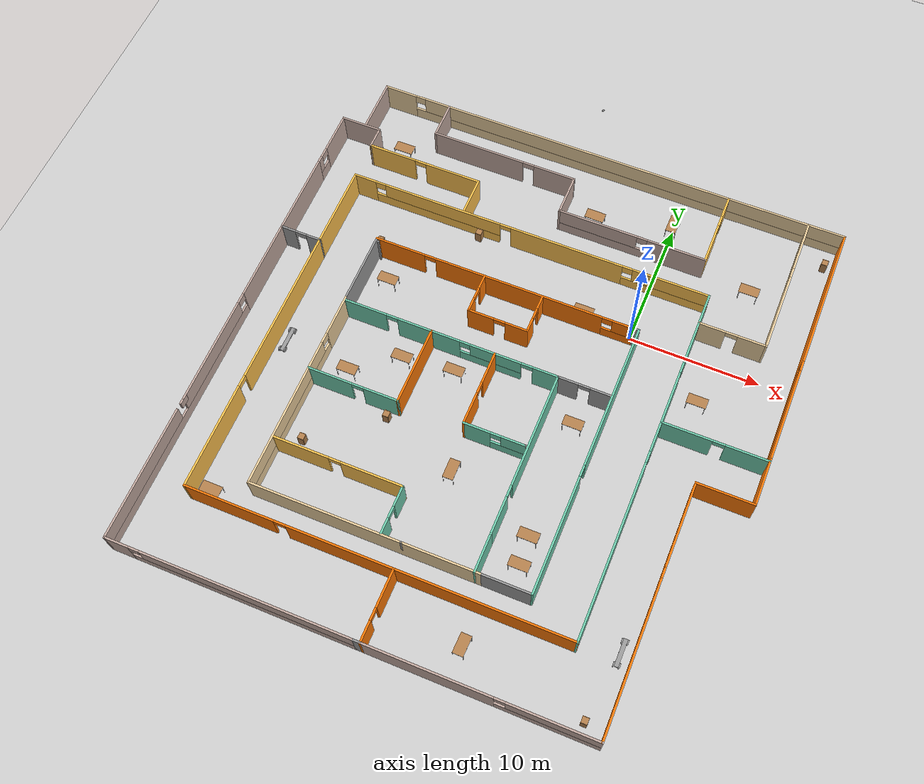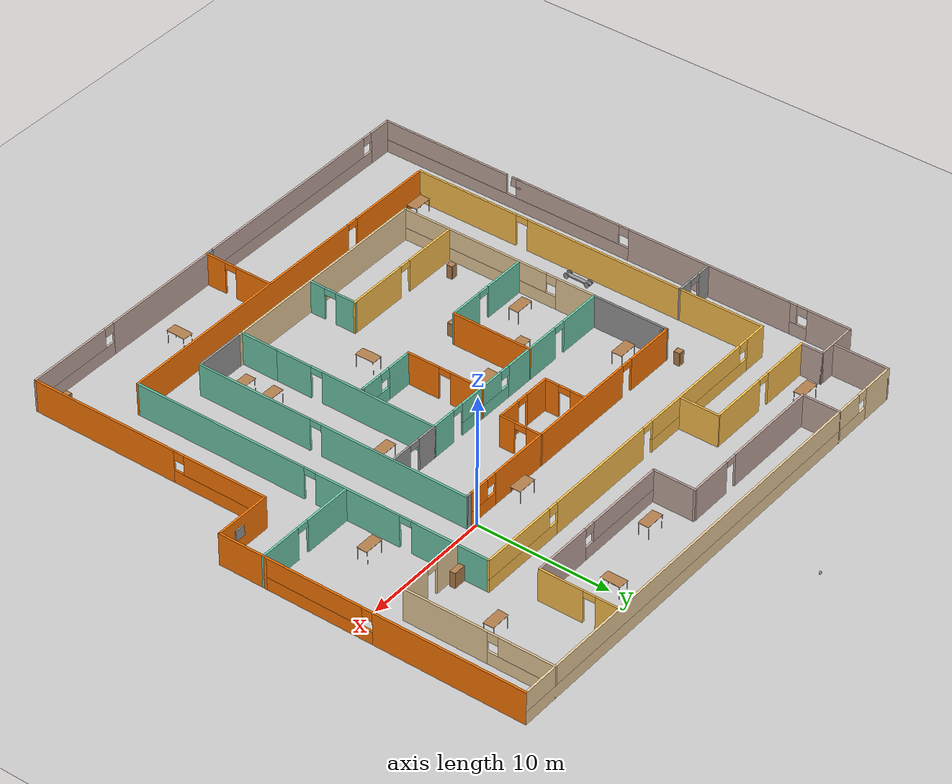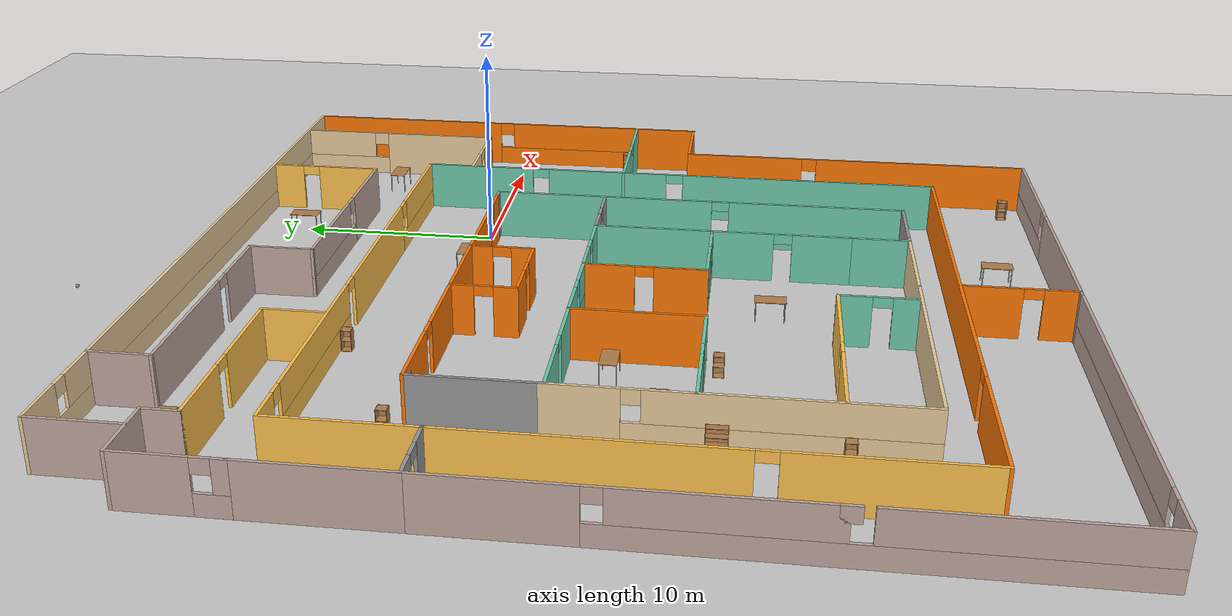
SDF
<sdf version="1.6">
 <world name="default">
  <plugin name="hello" filename="libhello.so"/>
  <light name="sun" type="directional">
   <pose>0 0 10 0 -0 0</pose>
   <diffuse>0.8 0.8 0.8 1</diffuse>
   <specular>0.2 0.2 0.2 1</specular>
   <attenuation>
    <range>1000</range>
    <constant>0.9</constant>
    <linear>0.01</linear>
    <quadratic>0.001</quadratic>
   </attenuation>
   <direction>-0.5 0.1 -0.9</direction>
  </light>
  <model name="ground_plane">
   <static>1</static>
   <link name="link">
    <collision name="collision">
     <geometry><plane><normal>0 0 1</normal><size>100 100</size></plane></geometry>
     <surface>
      <contact><collide_bitmask>65535</collide_bitmask></contact>
      <friction><ode><mu>100</mu><mu2>50</mu2></ode></friction>
     </surface>
    </collision>
    <visual name="visual">
     <cast_shadows>0</cast_shadows>
     <geometry><plane><normal>0 0 1</normal><size>100 100</size></plane></geometry>
     <material>
      <script><uri>file://media/materials/scripts/gazebo.material</uri><name>Gazebo/Grey</name></script>
     </material>
    </visual>
   </link>
  </model>
  <gravity>0 0 -9.8</gravity>
  <magnetic_field>6e-06 2.3e-05 -4.2e-05</magnetic_field>
  <atmosphere type="adiabatic"/>
  <physics name="default_physics" default="0" type="ode">
   <max_step_size>0.001</max_step_size>
   <real_time_factor>1</real_time_factor>
   <real_time_update_rate>1000</real_time_update_rate>
  </physics>
  <scene><ambient>0.4 0.4 0.4 1</ambient><background>0.7 0.7 0.7 1</background><shadows>1</shadows></scene>
  <spherical_coordinates>
   <surface_model>EARTH_WGS84</surface_model>
   <latitude_deg>0</latitude_deg>
   <longitude_deg>0</longitude_deg>
   <elevation>0</elevation>
   <heading_deg>0</heading_deg>
  </spherical_coordinates>
  <model name="table">
   <static>1</static>
   <link name="link">
    <collision name="surface">
     <pose>0 0 1 0 -0 0</pose>
     <geometry><box><size>1.5 0.8 0.03</size></box></geometry>
     <surface><friction><ode><mu>0.6</mu><mu2>0.6</mu2></ode></friction></surface>
    </collision>
    <visual name="visual1">
     <pose>0 0 1 0 -0 0</pose>
     <geometry><box><size>1.5 0.8 0.03</size></box></geometry>
     <material>
      <script><uri>file://media/materials/scripts/gazebo.material</uri><name>Gazebo/Wood</name></script>
     </material>
    </visual>
    <collision name="front_left_leg">
     <pose>0.68 0.38 0.5 0 -0 0</pose>
     <geometry><cylinder><radius>0.02</radius><length>1</length></cylinder></geometry>
    </collision>
    <visual name="front_left_leg">
     <pose>0.68 0.38 0.5 0 -0 0</pose>
     <geometry><cylinder><radius>0.02</radius><length>1</length></cylinder></geometry>
     <material>
      <script><uri>file://media/materials/scripts/gazebo.material</uri><name>Gazebo/Grey</name></script>
     </material>
    </visual>
    <collision name="front_right_leg">
     <pose>0.68 -0.38 0.5 0 -0 0</pose>
     <geometry><cylinder><radius>0.02</radius><length>1</length></cylinder></geometry>
    </collision>
    <visual name="front_right_leg">
     <pose>0.68 -0.38 0.5 0 -0 0</pose>
     <geometry><cylinder><radius>0.02</radius><length>1</length></cylinder></geometry>
     <material>
      <script><uri>file://media/materials/scripts/gazebo.material</uri><name>Gazebo/Grey</name></script>
     </material>
    </visual>
    <collision name="back_right_leg">
     <pose>-0.68 -0.38 0.5 0 -0 0</pose>
     <geometry><cylinder><radius>0.02</radius><length>1</length></cylinder></geometry>
    </collision>
    <visual name="back_right_leg">
     <pose>-0.68 -0.38 0.5 0 -0 0</pose>
     <geometry><cylinder><radius>0.02</radius><length>1</length></cylinder></geometry>
     <material>
      <script><uri>file://media/materials/scripts/gazebo.material</uri><name>Gazebo/Grey</name></script>
     </material>
    </visual>
    <collision name="back_left_leg">
     <pose>-0.68 0.38 0.5 0 -0 0</pose>
     <geometry><cylinder><radius>0.02</radius><length>1</length></cylinder></geometry>
    </collision>
    <visual name="back_left_leg">
     <pose>-0.68 0.38 0.5 0 -0 0</pose>
     <geometry><cylinder><radius>0.02</radius><length>1</length></cylinder></geometry>
     <material>
      <script><uri>file://media/materials/scripts/gazebo.material</uri><name>Gazebo/Grey</name></script>
     </material>
    </visual>
   </link>
   <pose>-3.88536 0.490535 0 0 -0 0</pose>
  </model>
  <model name="table_0">
   <static>1</static>
   <link name="link">
    <collision name="surface">
     <pose>0 0 1 0 -0 0</pose>
     <geometry><box><size>1.5 0.8 0.03</size></box></geometry>
     <surface><friction><ode><mu>0.6</mu><mu2>0.6</mu2></ode></friction></surface>
    </collision>
    <visual name="visual1">
     <pose>0 0 1 0 -0 0</pose>
     <geometry><box><size>1.5 0.8 0.03</size></box></geometry>
     <material>
      <script><uri>file://media/materials/scripts/gazebo.material</uri><name>Gazebo/Wood</name></script>
     </material>
    </visual>
    <collision name="front_left_leg">
     <pose>0.68 0.38 0.5 0 -0 0</pose>
     <geometry><cylinder><radius>0.02</radius><length>1</length></cylinder></geometry>
    </collision>
    <visual name="front_left_leg">
     <pose>0.68 0.38 0.5 0 -0 0</pose>
     <geometry><cylinder><radius>0.02</radius><length>1</length></cylinder></geometry>
     <material>
      <script><uri>file://media/materials/scripts/gazebo.material</uri><name>Gazebo/Grey</name></script>
     </material>
    </visual>
    <collision name="front_right_leg">
     <pose>0.68 -0.38 0.5 0 -0 0</pose>
     <geometry><cylinder><radius>0.02</radius><length>1</length></cylinder></geometry>
    </collision>
    <visual name="front_right_leg">
     <pose>0.68 -0.38 0.5 0 -0 0</pose>
     <geometry><cylinder><radius>0.02</radius><length>1</length></cylinder></geometry>
     <material>
      <script><uri>file://media/materials/scripts/gazebo.material</uri><name>Gazebo/Grey</name></script>
     </material>
    </visual>
    <collision name="back_right_leg">
     <pose>-0.68 -0.38 0.5 0 -0 0</pose>
     <geometry><cylinder><radius>0.02</radius><length>1</length></cylinder></geometry>
    </collision>
    <visual name="back_right_leg">
     <pose>-0.68 -0.38 0.5 0 -0 0</pose>
     <geometry><cylinder><radius>0.02</radius><length>1</length></cylinder></geometry>
     <material>
      <script><uri>file://media/materials/scripts/gazebo.material</uri><name>Gazebo/Grey</name></script>
     </material>
    </visual>
    <collision name="back_left_leg">
     <pose>-0.68 0.38 0.5 0 -0 0</pose>
     <geometry><cylinder><radius>0.02</radius><length>1</length></cylinder></geometry>
    </collision>
    <visual name="back_left_leg">
     <pose>-0.68 0.38 0.5 0 -0 0</pose>
     <geometry><cylinder><radius>0.02</radius><length>1</length></cylinder></geometry>
     <material>
      <script><uri>file://media/materials/scripts/gazebo.material</uri><name>Gazebo/Grey</name></script>
     </material>
    </visual>
   </link>
   <pose>6.25449 -3.41825 0 0 -0 0</pose>
  </model>
  <model name="cabinet">
   <static>1</static>
   <link name="cabinet_bottom_plate">
    <inertial>
     <pose>0 0 -1 0 -0 0</pose>
     <inertia><ixx>2.05</ixx><ixy>0</ixy><ixz>0</ixz><iyy>2.05</iyy><iyz>0</iyz><izz>2.05</izz></inertia>
     <mass>25</mass>
    </inertial>
    <collision name="cabinet_bottom_plate_geom">
     <pose>0 0 0.01 0 -0 0</pose>
     <geometry><box><size>0.45 0.45 0.02</size></box></geometry>
    </collision>
    <visual name="cabinet_bottom_plate_geom_visual">
     <pose>0 0 0.01 0 -0 0</pose>
     <geometry><box><size>0.45 0.45 0.02</size></box></geometry>
     <material>
      <script><uri>file://media/materials/scripts/gazebo.material</uri><name>Gazebo/Wood</name></script>
     </material>
    </visual>
    <collision name="cabinet_bottom_plate_geom_cabinet_back_plate">
     <pose>0.235 0 0.51 0 -0 0</pose>
     <geometry><box><size>0.02 0.45 1.02</size></box></geometry>
    </collision>
    <visual name="cabinet_bottom_plate_geom_cabinet_back_plate_visual">
     <pose>0.235 0 0.51 0 -0 0</pose>
     <geometry><box><size>0.02 0.45 1.02</size></box></geometry>
     <material>
      <script><uri>file://media/materials/scripts/gazebo.material</uri><name>Gazebo/Wood</name></script>
     </material>
    </visual>
    <collision name="cabinet_bottom_plate_geom_cabinet_left_plate">
     <pose>0 0.235 0.51 0 -0 0</pose>
     <geometry><box><size>0.45 0.02 1.02</size></box></geometry>
    </collision>
    <visual name="cabinet_bottom_plate_geom_cabinet_left_plate_visual">
     <pose>0 0.235 0.51 0 -0 0</pose>
     <geometry><box><size>0.45 0.02 1.02</size></box></geometry>
     <material>
      <script><uri>file://media/materials/scripts/gazebo.material</uri><name>Gazebo/Wood</name></script>
     </material>
    </visual>
    <collision name="cabinet_bottom_plate_geom_cabinet_middle_plate">
     <pose>0 0 0.51 0 -0 0</pose>
     <geometry><box><size>0.45 0.45 0.02</size></box></geometry>
    </collision>
    <visual name="cabinet_bottom_plate_geom_cabinet_middle_plate_visual">
     <pose>0 0 0.51 0 -0 0</pose>
     <geometry><box><size>0.45 0.45 0.02</size></box></geometry>
     <material>
      <script><uri>file://media/materials/scripts/gazebo.material</uri><name>Gazebo/Wood</name></script>
     </material>
    </visual>
    <collision name="cabinet_bottom_plate_geom_cabinet_right_plate">
     <pose>0 -0.235 0.51 0 -0 0</pose>
     <geometry><box><size>0.45 0.02 1.02</size></box></geometry>
    </collision>
    <visual name="cabinet_bottom_plate_geom_cabinet_right_plate_visual">
     <pose>0 -0.235 0.51 0 -0 0</pose>
     <geometry><box><size>0.45 0.02 1.02</size></box></geometry>
     <material>
      <script><uri>file://media/materials/scripts/gazebo.material</uri><name>Gazebo/Wood</name></script>
     </material>
    </visual>
    <collision name="cabinet_bottom_plate_geom_cabinet_top_plate">
     <pose>0 0 1.01 0 -0 0</pose>
     <geometry><box><size>0.45 0.45 0.02</size></box></geometry>
    </collision>
    <visual name="cabinet_bottom_plate_geom_cabinet_top_plate_visual">
     <pose>0 0 1.01 0 -0 0</pose>
     <geometry><box><size>0.45 0.45 0.02</size></box></geometry>
     <material>
      <script><uri>file://media/materials/scripts/gazebo.material</uri><name>Gazebo/Wood</name></script>
     </material>
    </visual>
   </link>
   <pose>11.9206 -6.11327 0 0 -0 0</pose>
  </model>
  <model name="bookshelf">
   <static>1</static>
   <link name="link">
    <inertial><mass>1</mass></inertial>
    <collision name="back">
     <pose>0 0.005 0.6 0 -0 0</pose>
     <geometry><box><size>0.9 0.01 1.2</size></box></geometry>
    </collision>
    <visual name="visual1">
     <pose>0 0.005 0.6 0 -0 0</pose>
     <geometry><box><size>0.9 0.01 1.2</size></box></geometry>
     <material>
      <script><uri>file://media/materials/scripts/gazebo.material</uri><name>Gazebo/Wood</name></script>
     </material>
    </visual>
    <collision name="left_side">
     <pose>0.45 -0.195 0.6 0 -0 0</pose>
     <geometry><box><size>0.02 0.4 1.2</size></box></geometry>
    </collision>
    <visual name="visual2">
     <pose>0.45 -0.195 0.6 0 -0 0</pose>
     <geometry><box><size>0.02 0.4 1.2</size></box></geometry>
     <material>
      <script><uri>file://media/materials/scripts/gazebo.material</uri><name>Gazebo/Wood</name></script>
     </material>
    </visual>
    <collision name="right_side">
     <pose>-0.45 -0.195 0.6 0 -0 0</pose>
     <geometry><box><size>0.02 0.4 1.2</size></box></geometry>
    </collision>
    <visual name="visual3">
     <pose>-0.45 -0.195 0.6 0 -0 0</pose>
     <geometry><box><size>0.02 0.4 1.2</size></box></geometry>
     <material>
      <script><uri>file://media/materials/scripts/gazebo.material</uri><name>Gazebo/Wood</name></script>
     </material>
    </visual>
    <collision name="bottom">
     <pose>0 -0.195 0.03 0 -0 0</pose>
     <geometry><box><size>0.88 0.4 0.06</size></box></geometry>
    </collision>
    <visual name="visual4">
     <pose>0 -0.195 0.03 0 -0 0</pose>
     <geometry><box><size>0.88 0.4 0.06</size></box></geometry>
     <material>
      <script><uri>file://media/materials/scripts/gazebo.material</uri><name>Gazebo/Wood</name></script>
     </material>
    </visual>
    <collision name="top">
     <pose>0 -0.195 1.19 0 -0 0</pose>
     <geometry><box><size>0.88 0.4 0.02</size></box></geometry>
    </collision>
    <visual name="visual5">
     <pose>0 -0.195 1.19 0 -0 0</pose>
     <geometry><box><size>0.88 0.4 0.02</size></box></geometry>
     <material>
      <script><uri>file://media/materials/scripts/gazebo.material</uri><name>Gazebo/Wood</name></script>
     </material>
    </visual>
    <collision name="low_shelf">
     <pose>0 -0.195 0.43 0 -0 0</pose>
     <geometry><box><size>0.88 0.4 0.02</size></box></geometry>
    </collision>
    <visual name="visual6">
     <pose>0 -0.195 0.43 0 -0 0</pose>
     <geometry><box><size>0.88 0.4 0.02</size></box></geometry>
     <material>
      <script><uri>file://media/materials/scripts/gazebo.material</uri><name>Gazebo/Wood</name></script>
     </material>
    </visual>
    <collision name="high_shelf">
     <pose>0 -0.195 0.8 0 -0 0</pose>
     <geometry><box><size>0.88 0.4 0.02</size></box></geometry>
    </collision>
    <visual name="visual7">
     <pose>0 -0.195 0.8 0 -0 0</pose>
     <geometry><box><size>0.88 0.4 0.02</size></box></geometry>
     <material>
      <script><uri>file://media/materials/scripts/gazebo.material</uri><name>Gazebo/Wood</name></script>
     </material>
    </visual>
   </link>
   <pose>5.01452 2.49473 0 0 -0 0</pose>
  </model>
  <model name="office">
   <pose>-7.49516 -7.8361 0 0 -0 0</pose>
   <link name="Wall_102">
    <collision name="Wall_102_Collision">
     <geometry><box><size>0.15 0.15 2.5</size></box></geometry>
     <pose>0 0 1.25 0 -0 0</pose>
    </collision>
    <visual name="Wall_102_Visual">
     <pose>0 0 1.25 0 -0 0</pose>
     <geometry><box><size>0.15 0.15 2.5</size></box></geometry>
     <material>
      <script><uri>file://media/materials/scripts/gazebo.material</uri><name>Gazebo/Grey</name></script>
      <ambient>1 1 1 1</ambient>
     </material>
     <meta><layer>0</layer></meta>
    </visual>
    <pose>-1.30984 -13.6609 0 0 -0 0</pose>
   </link>
   <link name="Wall_104">
    <pose>-9.25834 -4.24987 0 0 -0 0</pose>
    <visual name="Wall_104_Visual_0">
     <pose>-1.81443 0 1.25 0 -0 0</pose>
     <geometry><box><size>3.46632 0.15 2.5</size></box></geometry>
     <material>
      <script><uri>file://media/materials/scripts/gazebo.material</uri><name>Gazebo/Grey</name></script>
      <ambient>0.435294 0.796078 0.67451 1</ambient>
     </material>
     <meta><layer>0</layer></meta>
    </visual>
    <collision name="Wall_104_Collision_0">
     <geometry><box><size>3.46632 0.15 2.5</size></box></geometry>
     <pose>-1.81443 0 1.25 0 -0 0</pose>
    </collision>
    <visual name="Wall_104_Visual_1">
     <pose>2.18316 0 1.25 0 -0 0</pose>
     <geometry><box><size>2.72887 0.15 2.5</size></box></geometry>
     <material>
      <script><uri>file://media/materials/scripts/gazebo.material</uri><name>Gazebo/Grey</name></script>
      <ambient>0.435294 0.796078 0.67451 1</ambient>
     </material>
     <meta><layer>0</layer></meta>
    </visual>
    <collision name="Wall_104_Collision_1">
     <geometry><box><size>2.72887 0.15 2.5</size></box></geometry>
     <pose>2.18316 0 1.25 0 -0 0</pose>
    </collision>
    <visual name="Wall_104_Visual_2">
     <pose>0.368727 0 2.25 0 -0 0</pose>
     <geometry><box><size>0.9 0.15 0.5</size></box></geometry>
     <material>
      <script><uri>file://media/materials/scripts/gazebo.material</uri><name>Gazebo/Grey</name></script>
      <ambient>0.435294 0.796078 0.67451 1</ambient>
     </material>
     <meta><layer>0</layer></meta>
    </visual>
    <collision name="Wall_104_Collision_2">
     <geometry><box><size>0.9 0.15 0.5</size></box></geometry>
     <pose>0.368727 0 2.25 0 -0 0</pose>
    </collision>
   </link>
   <link name="Wall_105">
    <collision name="Wall_105_Collision">
     <geometry><box><size>6.163 0.15 2.5</size></box></geometry>
     <pose>0 0 1.25 0 -0 0</pose>
    </collision>
    <visual name="Wall_105_Visual">
     <pose>0 0 1.25 0 -0 0</pose>
     <geometry><box><size>6.163 0.15 2.5</size></box></geometry>
     <material>
      <script><uri>file://media/materials/scripts/gazebo.material</uri><name>Gazebo/Grey</name></script>
      <ambient>0.996078 0.47451 0.0196078 1</ambient>
     </material>
     <meta><layer>0</layer></meta>
    </visual>
    <pose>-5.78584 -1.24337 0 0 -0 1.5708</pose>
   </link>
   <link name="Wall_107">
    <pose>-3.97884 5.92013 0 0 0 -1.5708</pose>
    <visual name="Wall_107_Visual_0">
     <pose>-1.03263 0 1.25 0 -0 0</pose>
     <geometry><box><size>1.16841 0.15 2.5</size></box></geometry>
     <material>
      <script><uri>file://media/materials/scripts/gazebo.material</uri><name>Gazebo/Grey</name></script>
      <ambient>0.996078 0.47451 0.0196078 1</ambient>
     </material>
     <meta><layer>0</layer></meta>
    </visual>
    <collision name="Wall_107_Collision_0">
     <geometry><box><size>1.16841 0.15 2.5</size></box></geometry>
     <pose>-1.03263 0 1.25 0 -0 0</pose>
    </collision>
    <visual name="Wall_107_Visual_1">
     <pose>1.0342 0 1.25 0 -0 0</pose>
     <geometry><box><size>1.16527 0.15 2.5</size></box></geometry>
     <material>
      <script><uri>file://media/materials/scripts/gazebo.material</uri><name>Gazebo/Grey</name></script>
      <ambient>0.996078 0.47451 0.0196078 1</ambient>
     </material>
     <meta><layer>0</layer></meta>
    </visual>
    <collision name="Wall_107_Collision_1">
     <geometry><box><size>1.16527 0.15 2.5</size></box></geometry>
     <pose>1.0342 0 1.25 0 -0 0</pose>
    </collision>
    <visual name="Wall_107_Visual_2">
     <pose>0.001569 0 2.25 0 -0 0</pose>
     <geometry><box><size>0.9 0.15 0.5</size></box></geometry>
     <material>
      <script><uri>file://media/materials/scripts/gazebo.material</uri><name>Gazebo/Grey</name></script>
      <ambient>0.996078 0.47451 0.0196078 1</ambient>
     </material>
     <meta><layer>0</layer></meta>
    </visual>
    <collision name="Wall_107_Collision_2">
     <geometry><box><size>0.9 0.15 0.5</size></box></geometry>
     <pose>0.001569 0 2.25 0 -0 0</pose>
    </collision>
   </link>
   <link name="Wall_108">
    <pose>-1.67884 4.37813 0 0 -0 0</pose>
    <visual name="Wall_108_Visual_0">
     <pose>-1.35534 0 1.25 0 -0 0</pose>
     <geometry><box><size>2.03931 0.15 2.5</size></box></geometry>
     <material>
      <script><uri>file://media/materials/scripts/gazebo.material</uri><name>Gazebo/Grey</name></script>
      <ambient>0.996078 0.47451 0.0196078 1</ambient>
     </material>
     <meta><layer>0</layer></meta>
    </visual>
    <collision name="Wall_108_Collision_0">
     <geometry><box><size>2.03931 0.15 2.5</size></box></geometry>
     <pose>-1.35534 0 1.25 0 -0 0</pose>
    </collision>
    <visual name="Wall_108_Visual_1">
     <pose>1.46966 0 1.25 0 -0 0</pose>
     <geometry><box><size>1.81069 0.15 2.5</size></box></geometry>
     <material>
      <script><uri>file://media/materials/scripts/gazebo.material</uri><name>Gazebo/Grey</name></script>
      <ambient>0.996078 0.47451 0.0196078 1</ambient>
     </material>
     <meta><layer>0</layer></meta>
    </visual>
    <collision name="Wall_108_Collision_1">
     <geometry><box><size>1.81069 0.15 2.5</size></box></geometry>
     <pose>1.46966 0 1.25 0 -0 0</pose>
    </collision>
    <visual name="Wall_108_Visual_2">
     <pose>0.114313 0 2.25 0 -0 0</pose>
     <geometry><box><size>0.9 0.15 0.5</size></box></geometry>
     <material>
      <script><uri>file://media/materials/scripts/gazebo.material</uri><name>Gazebo/Grey</name></script>
      <ambient>0.996078 0.47451 0.0196078 1</ambient>
     </material>
     <meta><layer>0</layer></meta>
    </visual>
    <collision name="Wall_108_Collision_2">
     <geometry><box><size>0.9 0.15 0.5</size></box></geometry>
     <pose>0.114313 0 2.25 0 -0 0</pose>
    </collision>
   </link>
   <link name="Wall_109">
    <pose>0.621161 5.92013 0 0 -0 1.5708</pose>
    <visual name="Wall_109_Visual_0">
     <pose>-1.03428 0 1.25 0 -0 0</pose>
     <geometry><box><size>1.16543 0.15 2.5</size></box></geometry>
     <material>
      <script><uri>file://media/materials/scripts/gazebo.material</uri><name>Gazebo/Grey</name></script>
      <ambient>0.996078 0.47451 0.0196078 1</ambient>
     </material>
     <meta><layer>0</layer></meta>
    </visual>
    <collision name="Wall_109_Collision_0">
     <geometry><box><size>1.16543 0.15 2.5</size></box></geometry>
     <pose>-1.03428 0 1.25 0 -0 0</pose>
    </collision>
    <visual name="Wall_109_Visual_1">
     <pose>1.03272 0 1.25 0 -0 0</pose>
     <geometry><box><size>1.16857 0.15 2.5</size></box></geometry>
     <material>
      <script><uri>file://media/materials/scripts/gazebo.material</uri><name>Gazebo/Grey</name></script>
      <ambient>0.996078 0.47451 0.0196078 1</ambient>
     </material>
     <meta><layer>0</layer></meta>
    </visual>
    <collision name="Wall_109_Collision_1">
     <geometry><box><size>1.16857 0.15 2.5</size></box></geometry>
     <pose>1.03272 0 1.25 0 -0 0</pose>
    </collision>
    <visual name="Wall_109_Visual_2">
     <pose>-0.001569 0 2.25 0 -0 0</pose>
     <geometry><box><size>0.9 0.15 0.5</size></box></geometry>
     <material>
      <script><uri>file://media/materials/scripts/gazebo.material</uri><name>Gazebo/Grey</name></script>
      <ambient>0.996078 0.47451 0.0196078 1</ambient>
     </material>
     <meta><layer>0</layer></meta>
    </visual>
    <collision name="Wall_109_Collision_2">
     <geometry><box><size>0.9 0.15 0.5</size></box></geometry>
     <pose>-0.001569 0 2.25 0 -0 0</pose>
    </collision>
   </link>
   <link name="Wall_111">
    <pose>-2.36175 12.0954 0 0 -0 0</pose>
    <visual name="Wall_111_Visual_0">
     <pose>-13.4635 0 1.25 0 -0 0</pose>
     <geometry><box><size>1.82295 0.15 2.5</size></box></geometry>
     <material>
      <script><uri>file://media/materials/scripts/gazebo.material</uri><name>Gazebo/Grey</name></script>
      <ambient>1 0.764706 0.305882 1</ambient>
     </material>
     <meta><layer>0</layer></meta>
    </visual>
    <collision name="Wall_111_Collision_0">
     <geometry><box><size>1.82295 0.15 2.5</size></box></geometry>
     <pose>-13.4635 0 1.25 0 -0 0</pose>
    </collision>
    <visual name="Wall_111_Visual_1">
     <pose>3.09605 0 1.25 0 -0 0</pose>
     <geometry><box><size>8.94656 0.15 2.5</size></box></geometry>
     <material>
      <script><uri>file://media/materials/scripts/gazebo.material</uri><name>Gazebo/Grey</name></script>
      <ambient>1 0.764706 0.305882 1</ambient>
     </material>
     <meta><layer>0</layer></meta>
    </visual>
    <collision name="Wall_111_Collision_1">
     <geometry><box><size>8.94656 0.15 2.5</size></box></geometry>
     <pose>3.09605 0 1.25 0 -0 0</pose>
    </collision>
    <visual name="Wall_111_Visual_2">
     <pose>-7.41464 0 0.5 0 -0 0</pose>
     <geometry><box><size>10.2748 0.15 1</size></box></geometry>
     <material>
      <script><uri>file://media/materials/scripts/gazebo.material</uri><name>Gazebo/Grey</name></script>
      <ambient>1 0.764706 0.305882 1</ambient>
     </material>
     <meta><layer>0</layer></meta>
    </visual>
    <collision name="Wall_111_Collision_2">
     <geometry><box><size>10.2748 0.15 1</size></box></geometry>
     <pose>-7.41464 0 0.5 0 -0 0</pose>
    </collision>
    <visual name="Wall_111_Visual_3">
     <pose>10.9722 0 0.5 0 -0 0</pose>
     <geometry><box><size>6.80567 0.15 1</size></box></geometry>
     <material>
      <script><uri>file://media/materials/scripts/gazebo.material</uri><name>Gazebo/Grey</name></script>
      <ambient>1 0.764706 0.305882 1</ambient>
     </material>
     <meta><layer>0</layer></meta>
    </visual>
    <collision name="Wall_111_Collision_3">
     <geometry><box><size>6.80567 0.15 1</size></box></geometry>
     <pose>10.9722 0 0.5 0 -0 0</pose>
    </collision>
    <visual name="Wall_111_Visual_4">
     <pose>-7.01464 0 1.75 0 -0 0</pose>
     <geometry><box><size>9.47482 0.15 1.5</size></box></geometry>
     <material>
      <script><uri>file://media/materials/scripts/gazebo.material</uri><name>Gazebo/Grey</name></script>
      <ambient>1 0.764706 0.305882 1</ambient>
     </material>
     <meta><layer>0</layer></meta>
    </visual>
    <collision name="Wall_111_Collision_4">
     <geometry><box><size>9.47482 0.15 1.5</size></box></geometry>
     <pose>-7.01464 0 1.75 0 -0 0</pose>
    </collision>
    <visual name="Wall_111_Visual_5">
     <pose>-7.01464 0 1.75 0 -0 0</pose>
     <geometry><box><size>9.47482 0.15 1.5</size></box></geometry>
     <material>
      <script><uri>file://media/materials/scripts/gazebo.material</uri><name>Gazebo/Grey</name></script>
      <ambient>1 0.764706 0.305882 1</ambient>
     </material>
     <meta><layer>0</layer></meta>
    </visual>
    <collision name="Wall_111_Collision_5">
     <geometry><box><size>9.47482 0.15 1.5</size></box></geometry>
     <pose>-7.01464 0 1.75 0 -0 0</pose>
    </collision>
    <visual name="Wall_111_Visual_6">
     <pose>11.3722 0 1.75 0 -0 0</pose>
     <geometry><box><size>6.00566 0.15 1.5</size></box></geometry>
     <material>
      <script><uri>file://media/materials/scripts/gazebo.material</uri><name>Gazebo/Grey</name></script>
      <ambient>1 0.764706 0.305882 1</ambient>
     </material>
     <meta><layer>0</layer></meta>
    </visual>
    <collision name="Wall_111_Collision_6">
     <geometry><box><size>6.00566 0.15 1.5</size></box></geometry>
     <pose>11.3722 0 1.75 0 -0 0</pose>
    </collision>
    <visual name="Wall_111_Visual_7">
     <pose>-12.152 0 2.15 0 -0 0</pose>
     <geometry><box><size>0.8 0.15 0.7</size></box></geometry>
     <material>
      <script><uri>file://media/materials/scripts/gazebo.material</uri><name>Gazebo/Grey</name></script>
      <ambient>1 0.764706 0.305882 1</ambient>
     </material>
     <meta><layer>0</layer></meta>
    </visual>
    <collision name="Wall_111_Collision_7">
     <geometry><box><size>0.8 0.15 0.7</size></box></geometry>
     <pose>-12.152 0 2.15 0 -0 0</pose>
    </collision>
    <visual name="Wall_111_Visual_8">
     <pose>7.96934 0 2.15 0 -0 0</pose>
     <geometry><box><size>0.8 0.15 0.7</size></box></geometry>
     <material>
      <script><uri>file://media/materials/scripts/gazebo.material</uri><name>Gazebo/Grey</name></script>
      <ambient>1 0.764706 0.305882 1</ambient>
     </material>
     <meta><layer>0</layer></meta>
    </visual>
    <collision name="Wall_111_Collision_8">
     <geometry><box><size>0.8 0.15 0.7</size></box></geometry>
     <pose>7.96934 0 2.15 0 -0 0</pose>
    </collision>
    <visual name="Wall_111_Visual_9">
     <pose>-1.82723 0 2.25 0 -0 0</pose>
     <geometry><box><size>0.9 0.15 0.5</size></box></geometry>
     <material>
      <script><uri>file://media/materials/scripts/gazebo.material</uri><name>Gazebo/Grey</name></script>
      <ambient>1 0.764706 0.305882 1</ambient>
     </material>
     <meta><layer>0</layer></meta>
    </visual>
    <collision name="Wall_111_Collision_9">
     <geometry><box><size>0.9 0.15 0.5</size></box></geometry>
     <pose>-1.82723 0 2.25 0 -0 0</pose>
    </collision>
    <visual name="Wall_111_Visual_10">
     <pose>-1.82723 0 2.25 0 -0 0</pose>
     <geometry><box><size>0.9 0.15 0.5</size></box></geometry>
     <material>
      <script><uri>file://media/materials/scripts/gazebo.material</uri><name>Gazebo/Grey</name></script>
      <ambient>1 0.764706 0.305882 1</ambient>
     </material>
     <meta><layer>0</layer></meta>
    </visual>
    <collision name="Wall_111_Collision_10">
     <geometry><box><size>0.9 0.15 0.5</size></box></geometry>
     <pose>-1.82723 0 2.25 0 -0 0</pose>
    </collision>
   </link>
   <link name="Wall_112">
    <pose>11.9382 -1.70464 0 0 0 -1.5708</pose>
    <visual name="Wall_112_Visual_0">
     <pose>-10.9153 0 1.25 0 -0 0</pose>
     <geometry><box><size>5.91935 0.15 2.5</size></box></geometry>
     <material>
      <script><uri>file://media/materials/scripts/gazebo.material</uri><name>Gazebo/Grey</name></script>
      <ambient>0.435294 0.796078 0.67451 1</ambient>
     </material>
     <meta><layer>0</layer></meta>
    </visual>
    <collision name="Wall_112_Collision_0">
     <geometry><box><size>5.91935 0.15 2.5</size></box></geometry>
     <pose>-10.9153 0 1.25 0 -0 0</pose>
    </collision>
    <visual name="Wall_112_Visual_1">
     <pose>-3.79167 0 1.25 0 -0 0</pose>
     <geometry><box><size>6.52794 0.15 2.5</size></box></geometry>
     <material>
      <script><uri>file://media/materials/scripts/gazebo.material</uri><name>Gazebo/Grey</name></script>
      <ambient>0.435294 0.796078 0.67451 1</ambient>
     </material>
     <meta><layer>0</layer></meta>
    </visual>
    <collision name="Wall_112_Collision_1">
     <geometry><box><size>6.52794 0.15 2.5</size></box></geometry>
     <pose>-3.79167 0 1.25 0 -0 0</pose>
    </collision>
    <visual name="Wall_112_Visual_2">
     <pose>7.12365 0 1.25 0 -0 0</pose>
     <geometry><box><size>13.5027 0.15 2.5</size></box></geometry>
     <material>
      <script><uri>file://media/materials/scripts/gazebo.material</uri><name>Gazebo/Grey</name></script>
      <ambient>0.435294 0.796078 0.67451 1</ambient>
     </material>
     <meta><layer>0</layer></meta>
    </visual>
    <collision name="Wall_112_Collision_2">
     <geometry><box><size>13.5027 0.15 2.5</size></box></geometry>
     <pose>7.12365 0 1.25 0 -0 0</pose>
    </collision>
    <visual name="Wall_112_Visual_3">
     <pose>-7.50565 0 2.25 0 -0 0</pose>
     <geometry><box><size>0.9 0.15 0.5</size></box></geometry>
     <material>
      <script><uri>file://media/materials/scripts/gazebo.material</uri><name>Gazebo/Grey</name></script>
      <ambient>0.435294 0.796078 0.67451 1</ambient>
     </material>
     <meta><layer>0</layer></meta>
    </visual>
    <collision name="Wall_112_Collision_3">
     <geometry><box><size>0.9 0.15 0.5</size></box></geometry>
     <pose>-7.50565 0 2.25 0 -0 0</pose>
    </collision>
    <visual name="Wall_112_Visual_4">
     <pose>-0.077701 0 2.25 0 -0 0</pose>
     <geometry><box><size>0.9 0.15 0.5</size></box></geometry>
     <material>
      <script><uri>file://media/materials/scripts/gazebo.material</uri><name>Gazebo/Grey</name></script>
      <ambient>0.435294 0.796078 0.67451 1</ambient>
     </material>
     <meta><layer>0</layer></meta>
    </visual>
    <collision name="Wall_112_Collision_4">
     <geometry><box><size>0.9 0.15 0.5</size></box></geometry>
     <pose>-0.077701 0 2.25 0 -0 0</pose>
    </collision>
   </link>
   <link name="Wall_113">
    <pose>-2.36175 -15.5046 0 0 -0 3.14159</pose>
    <visual name="Wall_113_Visual_0">
     <pose>-3.87703 0 1.25 0 -0 0</pose>
     <geometry><box><size>20.9959 0.15 2.5</size></box></geometry>
     <material>
      <script><uri>file://media/materials/scripts/gazebo.material</uri><name>Gazebo/Grey</name></script>
      <ambient>0.996078 0.47451 0.0196078 1</ambient>
     </material>
     <meta><layer>0</layer></meta>
    </visual>
    <collision name="Wall_113_Collision_0">
     <geometry><box><size>20.9959 0.15 2.5</size></box></geometry>
     <pose>-3.87703 0 1.25 0 -0 0</pose>
    </collision>
    <visual name="Wall_113_Visual_1">
     <pose>10.948 0 1.25 0 -0 0</pose>
     <geometry><box><size>6.85407 0.15 2.5</size></box></geometry>
     <material>
      <script><uri>file://media/materials/scripts/gazebo.material</uri><name>Gazebo/Grey</name></script>
      <ambient>0.996078 0.47451 0.0196078 1</ambient>
     </material>
     <meta><layer>0</layer></meta>
    </visual>
    <collision name="Wall_113_Collision_1">
     <geometry><box><size>6.85407 0.15 2.5</size></box></geometry>
     <pose>10.948 0 1.25 0 -0 0</pose>
    </collision>
    <visual name="Wall_113_Visual_2">
     <pose>7.07093 0 2.25 0 -0 0</pose>
     <geometry><box><size>0.9 0.15 0.5</size></box></geometry>
     <material>
      <script><uri>file://media/materials/scripts/gazebo.material</uri><name>Gazebo/Grey</name></script>
      <ambient>0.996078 0.47451 0.0196078 1</ambient>
     </material>
     <meta><layer>0</layer></meta>
    </visual>
    <collision name="Wall_113_Collision_2">
     <geometry><box><size>0.9 0.15 0.5</size></box></geometry>
     <pose>7.07093 0 2.25 0 -0 0</pose>
    </collision>
   </link>
   <link name="Wall_114">
    <pose>-16.6618 -1.70464 0 0 -0 1.5708</pose>
    <visual name="Wall_114_Visual_0">
     <pose>-9.80586 0 1.25 0 -0 0</pose>
     <geometry><box><size>8.13829 0.15 2.5</size></box></geometry>
     <material>
      <script><uri>file://media/materials/scripts/gazebo.material</uri><name>Gazebo/Grey</name></script>
      <ambient>1 0.764706 0.305882 1</ambient>
     </material>
     <meta><layer>0</layer></meta>
    </visual>
    <collision name="Wall_114_Collision_0">
     <geometry><box><size>8.13829 0.15 2.5</size></box></geometry>
     <pose>-9.80586 0 1.25 0 -0 0</pose>
    </collision>
    <visual name="Wall_114_Visual_1">
     <pose>4.51914 0 1.25 0 -0 0</pose>
     <geometry><box><size>18.7117 0.15 2.5</size></box></geometry>
     <material>
      <script><uri>file://media/materials/scripts/gazebo.material</uri><name>Gazebo/Grey</name></script>
      <ambient>1 0.764706 0.305882 1</ambient>
     </material>
     <meta><layer>0</layer></meta>
    </visual>
    <collision name="Wall_114_Collision_1">
     <geometry><box><size>18.7117 0.15 2.5</size></box></geometry>
     <pose>4.51914 0 1.25 0 -0 0</pose>
    </collision>
    <visual name="Wall_114_Visual_2">
     <pose>-5.28671 0 2.25 0 -0 0</pose>
     <geometry><box><size>0.9 0.15 0.5</size></box></geometry>
     <material>
      <script><uri>file://media/materials/scripts/gazebo.material</uri><name>Gazebo/Grey</name></script>
      <ambient>1 0.764706 0.305882 1</ambient>
     </material>
     <meta><layer>0</layer></meta>
    </visual>
    <collision name="Wall_114_Collision_2">
     <geometry><box><size>0.9 0.15 0.5</size></box></geometry>
     <pose>-5.28671 0 2.25 0 -0 0</pose>
    </collision>
   </link>
   <link name="Wall_116">
    <pose>-19.8252 14.3606 0 0 0 -1.5708</pose>
    <visual name="Wall_116_Visual_0">
     <pose>-0.731274 0 1.25 0 -0 0</pose>
     <geometry><box><size>3.28745 0.15 2.5</size></box></geometry>
     <material>
      <script><uri>file://media/materials/scripts/gazebo.material</uri><name>Gazebo/Grey</name></script>
      <ambient>0.760784 0.662745 0.627451 1</ambient>
     </material>
     <meta><layer>0</layer></meta>
    </visual>
    <collision name="Wall_116_Collision_0">
     <geometry><box><size>3.28745 0.15 2.5</size></box></geometry>
     <pose>-0.731274 0 1.25 0 -0 0</pose>
    </collision>
    <visual name="Wall_116_Visual_1">
     <pose>1.64373 0 0.5 0 -0 0</pose>
     <geometry><box><size>1.46255 0.15 1</size></box></geometry>
     <material>
      <script><uri>file://media/materials/scripts/gazebo.material</uri><name>Gazebo/Grey</name></script>
      <ambient>0.760784 0.662745 0.627451 1</ambient>
     </material>
     <meta><layer>0</layer></meta>
    </visual>
    <collision name="Wall_116_Collision_1">
     <geometry><box><size>1.46255 0.15 1</size></box></geometry>
     <pose>1.64373 0 0.5 0 -0 0</pose>
    </collision>
    <visual name="Wall_116_Visual_2">
     <pose>2.04373 0 1.75 0 -0 0</pose>
     <geometry><box><size>0.662549 0.15 1.5</size></box></geometry>
     <material>
      <script><uri>file://media/materials/scripts/gazebo.material</uri><name>Gazebo/Grey</name></script>
      <ambient>0.760784 0.662745 0.627451 1</ambient>
     </material>
     <meta><layer>0</layer></meta>
    </visual>
    <collision name="Wall_116_Collision_2">
     <geometry><box><size>0.662549 0.15 1.5</size></box></geometry>
     <pose>2.04373 0 1.75 0 -0 0</pose>
    </collision>
    <visual name="Wall_116_Visual_3">
     <pose>1.31245 0 2.15 0 -0 0</pose>
     <geometry><box><size>0.8 0.15 0.7</size></box></geometry>
     <material>
      <script><uri>file://media/materials/scripts/gazebo.material</uri><name>Gazebo/Grey</name></script>
      <ambient>0.760784 0.662745 0.627451 1</ambient>
     </material>
     <meta><layer>0</layer></meta>
    </visual>
    <collision name="Wall_116_Collision_3">
     <geometry><box><size>0.8 0.15 0.7</size></box></geometry>
     <pose>1.31245 0 2.15 0 -0 0</pose>
    </collision>
   </link>
   <link name="Wall_119">
    <collision name="Wall_119_Collision">
     <geometry><box><size>3.25 0.15 2.5</size></box></geometry>
     <pose>0 0 1.25 0 -0 0</pose>
    </collision>
    <visual name="Wall_119_Visual">
     <pose>0 0 1.25 0 -0 0</pose>
     <geometry><box><size>3.25 0.15 2.5</size></box></geometry>
     <material>
      <script><uri>file://media/materials/scripts/gazebo.material</uri><name>Gazebo/Grey</name></script>
      <ambient>0.760784 0.662745 0.627451 1</ambient>
     </material>
     <meta><layer>0</layer></meta>
    </visual>
    <pose>-18.2752 16.6606 0 0 -0 3.14159</pose>
   </link>
   <link name="Wall_121">
    <collision name="Wall_121_Collision">
     <geometry><box><size>6.5 0.15 2.5</size></box></geometry>
     <pose>0 0 1.25 0 -0 0</pose>
    </collision>
    <visual name="Wall_121_Visual">
     <pose>0 0 1.25 0 -0 0</pose>
     <geometry><box><size>6.5 0.15 2.5</size></box></geometry>
     <material>
      <script><uri>file://media/materials/scripts/gazebo.material</uri><name>Gazebo/Grey</name></script>
      <ambient>0.760784 0.662745 0.627451 1</ambient>
     </material>
     <meta><layer>0</layer></meta>
    </visual>
    <pose>-19.825 8.88534 0 0 0 -1.57074</pose>
   </link>
   <link name="Wall_122">
    <pose>-18.2433 5.71013 0 0 -0 0</pose>
    <visual name="Wall_122_Visual_0">
     <pose>-1.03899 0 1.25 0 -0 0</pose>
     <geometry><box><size>1.23503 0.15 2.5</size></box></geometry>
     <material>
      <script><uri>file://media/materials/scripts/gazebo.material</uri><name>Gazebo/Grey</name></script>
      <ambient>1 1 1 1</ambient>
     </material>
     <meta><layer>0</layer></meta>
    </visual>
    <collision name="Wall_122_Collision_0">
     <geometry><box><size>1.23503 0.15 2.5</size></box></geometry>
     <pose>-1.03899 0 1.25 0 -0 0</pose>
    </collision>
    <visual name="Wall_122_Visual_1">
     <pose>1.06751 0 1.25 0 -0 0</pose>
     <geometry><box><size>1.17797 0.15 2.5</size></box></geometry>
     <material>
      <script><uri>file://media/materials/scripts/gazebo.material</uri><name>Gazebo/Grey</name></script>
      <ambient>1 1 1 1</ambient>
     </material>
     <meta><layer>0</layer></meta>
    </visual>
    <collision name="Wall_122_Collision_1">
     <geometry><box><size>1.17797 0.15 2.5</size></box></geometry>
     <pose>1.06751 0 1.25 0 -0 0</pose>
    </collision>
    <visual name="Wall_122_Visual_2">
     <pose>0.02853 0 2.25 0 -0 0</pose>
     <geometry><box><size>0.9 0.15 0.5</size></box></geometry>
     <material>
      <script><uri>file://media/materials/scripts/gazebo.material</uri><name>Gazebo/Grey</name></script>
      <ambient>1 1 1 1</ambient>
     </material>
     <meta><layer>0</layer></meta>
    </visual>
    <collision name="Wall_122_Collision_2">
     <geometry><box><size>0.9 0.15 0.5</size></box></geometry>
     <pose>0.02853 0 2.25 0 -0 0</pose>
    </collision>
   </link>
   <link name="Wall_123">
    <collision name="Wall_123_Collision">
     <geometry><box><size>0.15 0.15 2.5</size></box></geometry>
     <pose>0 0 1.25 0 -0 0</pose>
    </collision>
    <visual name="Wall_123_Visual">
     <pose>0 0 1.25 0 -0 0</pose>
     <geometry><box><size>0.15 0.15 2.5</size></box></geometry>
     <material>
      <script><uri>file://media/materials/scripts/gazebo.material</uri><name>Gazebo/Grey</name></script>
      <ambient>1 1 1 1</ambient>
     </material>
     <meta><layer>0</layer></meta>
    </visual>
    <pose>-16.6618 5.71013 0 0 -0 0</pose>
   </link>
   <link name="Wall_125">
    <pose>0.94866 20.7991 0 0 -0 0</pose>
    <visual name="Wall_125_Visual_0">
     <pose>-17.6396 0 1.25 0 -0 0</pose>
     <geometry><box><size>2.6238 0.15 2.5</size></box></geometry>
     <material>
      <script><uri>file://media/materials/scripts/gazebo.material</uri><name>Gazebo/Grey</name></script>
      <ambient>0.921569 0.807843 0.615686 1</ambient>
     </material>
     <meta><layer>0</layer></meta>
    </visual>
    <collision name="Wall_125_Collision_0">
     <geometry><box><size>2.6238 0.15 2.5</size></box></geometry>
     <pose>-17.6396 0 1.25 0 -0 0</pose>
    </collision>
    <visual name="Wall_125_Visual_1">
     <pose>1.3119 0 0.5 0 -0 0</pose>
     <geometry><box><size>35.2792 0.15 1</size></box></geometry>
     <material>
      <script><uri>file://media/materials/scripts/gazebo.material</uri><name>Gazebo/Grey</name></script>
      <ambient>0.921569 0.807843 0.615686 1</ambient>
     </material>
     <meta><layer>0</layer></meta>
    </visual>
    <collision name="Wall_125_Collision_1">
     <geometry><box><size>35.2792 0.15 1</size></box></geometry>
     <pose>1.3119 0 0.5 0 -0 0</pose>
    </collision>
    <visual name="Wall_125_Visual_2">
     <pose>1.7119 0 1.75 0 -0 0</pose>
     <geometry><box><size>34.4792 0.15 1.5</size></box></geometry>
     <material>
      <script><uri>file://media/materials/scripts/gazebo.material</uri><name>Gazebo/Grey</name></script>
      <ambient>0.921569 0.807843 0.615686 1</ambient>
     </material>
     <meta><layer>0</layer></meta>
    </visual>
    <collision name="Wall_125_Collision_2">
     <geometry><box><size>34.4792 0.15 1.5</size></box></geometry>
     <pose>1.7119 0 1.75 0 -0 0</pose>
    </collision>
    <visual name="Wall_125_Visual_3">
     <pose>-15.9277 0 2.15 0 -0 0</pose>
     <geometry><box><size>0.8 0.15 0.7</size></box></geometry>
     <material>
      <script><uri>file://media/materials/scripts/gazebo.material</uri><name>Gazebo/Grey</name></script>
      <ambient>0.921569 0.807843 0.615686 1</ambient>
     </material>
     <meta><layer>0</layer></meta>
    </visual>
    <collision name="Wall_125_Collision_3">
     <geometry><box><size>0.8 0.15 0.7</size></box></geometry>
     <pose>-15.9277 0 2.15 0 -0 0</pose>
    </collision>
   </link>
   <link name="Wall_126">
    <pose>19.8252 10.9991 0 0 0 -1.5708</pose>
    <visual name="Wall_126_Visual_0">
     <pose>-4.20483 0 1.25 0 -0 0</pose>
     <geometry><box><size>11.3403 0.15 2.5</size></box></geometry>
     <material>
      <script><uri>file://media/materials/scripts/gazebo.material</uri><name>Gazebo/Grey</name></script>
      <ambient>0.996078 0.47451 0.0196078 1</ambient>
     </material>
     <meta><layer>0</layer></meta>
    </visual>
    <collision name="Wall_126_Collision_0">
     <geometry><box><size>11.3403 0.15 2.5</size></box></geometry>
     <pose>-4.20483 0 1.25 0 -0 0</pose>
    </collision>
    <visual name="Wall_126_Visual_1">
     <pose>5.67017 0 0.5 0 -0 0</pose>
     <geometry><box><size>8.40965 0.15 1</size></box></geometry>
     <material>
      <script><uri>file://media/materials/scripts/gazebo.material</uri><name>Gazebo/Grey</name></script>
      <ambient>0.996078 0.47451 0.0196078 1</ambient>
     </material>
     <meta><layer>0</layer></meta>
    </visual>
    <collision name="Wall_126_Collision_1">
     <geometry><box><size>8.40965 0.15 1</size></box></geometry>
     <pose>5.67017 0 0.5 0 -0 0</pose>
    </collision>
    <visual name="Wall_126_Visual_2">
     <pose>6.07017 0 1.75 0 -0 0</pose>
     <geometry><box><size>7.60965 0.15 1.5</size></box></geometry>
     <material>
      <script><uri>file://media/materials/scripts/gazebo.material</uri><name>Gazebo/Grey</name></script>
      <ambient>0.996078 0.47451 0.0196078 1</ambient>
     </material>
     <meta><layer>0</layer></meta>
    </visual>
    <collision name="Wall_126_Collision_2">
     <geometry><box><size>7.60965 0.15 1.5</size></box></geometry>
     <pose>6.07017 0 1.75 0 -0 0</pose>
    </collision>
    <visual name="Wall_126_Visual_3">
     <pose>1.86535 0 2.15 0 -0 0</pose>
     <geometry><box><size>0.8 0.15 0.7</size></box></geometry>
     <material>
      <script><uri>file://media/materials/scripts/gazebo.material</uri><name>Gazebo/Grey</name></script>
      <ambient>0.996078 0.47451 0.0196078 1</ambient>
     </material>
     <meta><layer>0</layer></meta>
    </visual>
    <collision name="Wall_126_Collision_3">
     <geometry><box><size>0.8 0.15 0.7</size></box></geometry>
     <pose>1.86535 0 2.15 0 -0 0</pose>
    </collision>
   </link>
   <link name="Wall_127">
    <pose>15.8817 1.19913 0 0 -0 3.14159</pose>
    <visual name="Wall_127_Visual_0">
     <pose>-2.37244 0 1.25 0 -0 0</pose>
     <geometry><box><size>3.29212 0.15 2.5</size></box></geometry>
     <material>
      <script><uri>file://media/materials/scripts/gazebo.material</uri><name>Gazebo/Grey</name></script>
      <ambient>0.435294 0.796078 0.67451 1</ambient>
     </material>
     <meta><layer>0</layer></meta>
    </visual>
    <collision name="Wall_127_Collision_0">
     <geometry><box><size>3.29212 0.15 2.5</size></box></geometry>
     <pose>-2.37244 0 1.25 0 -0 0</pose>
    </collision>
    <visual name="Wall_127_Visual_1">
     <pose>2.09606 0 1.25 0 -0 0</pose>
     <geometry><box><size>3.84488 0.15 2.5</size></box></geometry>
     <material>
      <script><uri>file://media/materials/scripts/gazebo.material</uri><name>Gazebo/Grey</name></script>
      <ambient>0.435294 0.796078 0.67451 1</ambient>
     </material>
     <meta><layer>0</layer></meta>
    </visual>
    <collision name="Wall_127_Collision_1">
     <geometry><box><size>3.84488 0.15 2.5</size></box></geometry>
     <pose>2.09606 0 1.25 0 -0 0</pose>
    </collision>
    <visual name="Wall_127_Visual_2">
     <pose>-0.276377 0 2.25 0 -0 0</pose>
     <geometry><box><size>0.9 0.15 0.5</size></box></geometry>
     <material>
      <script><uri>file://media/materials/scripts/gazebo.material</uri><name>Gazebo/Grey</name></script>
      <ambient>0.435294 0.796078 0.67451 1</ambient>
     </material>
     <meta><layer>0</layer></meta>
    </visual>
    <collision name="Wall_127_Collision_2">
     <geometry><box><size>0.9 0.15 0.5</size></box></geometry>
     <pose>-0.276377 0 2.25 0 -0 0</pose>
    </collision>
   </link>
   <link name="Wall_134">
    <pose>10.7078 17.8581 0 0 -0 1.5708</pose>
    <visual name="Wall_134_Visual_0">
     <pose>-1.33185 0 1.25 0 -0 0</pose>
     <geometry><box><size>3.3363 0.15 2.5</size></box></geometry>
     <material>
      <script><uri>file://media/materials/scripts/gazebo.material</uri><name>Gazebo/Grey</name></script>
      <ambient>1 0.764706 0.305882 1</ambient>
     </material>
     <meta><layer>0</layer></meta>
    </visual>
    <collision name="Wall_134_Collision_0">
     <geometry><box><size>3.3363 0.15 2.5</size></box></geometry>
     <pose>-1.33185 0 1.25 0 -0 0</pose>
    </collision>
    <visual name="Wall_134_Visual_1">
     <pose>2.11815 0 1.25 0 -0 0</pose>
     <geometry><box><size>1.7637 0.15 2.5</size></box></geometry>
     <material>
      <script><uri>file://media/materials/scripts/gazebo.material</uri><name>Gazebo/Grey</name></script>
      <ambient>1 0.764706 0.305882 1</ambient>
     </material>
     <meta><layer>0</layer></meta>
    </visual>
    <collision name="Wall_134_Collision_1">
     <geometry><box><size>1.7637 0.15 2.5</size></box></geometry>
     <pose>2.11815 0 1.25 0 -0 0</pose>
    </collision>
    <visual name="Wall_134_Visual_2">
     <pose>0.786298 0 2.25 0 -0 0</pose>
     <geometry><box><size>0.9 0.15 0.5</size></box></geometry>
     <material>
      <script><uri>file://media/materials/scripts/gazebo.material</uri><name>Gazebo/Grey</name></script>
      <ambient>1 0.764706 0.305882 1</ambient>
     </material>
     <meta><layer>0</layer></meta>
    </visual>
    <collision name="Wall_134_Collision_2">
     <geometry><box><size>0.9 0.15 0.5</size></box></geometry>
     <pose>0.786298 0 2.25 0 -0 0</pose>
    </collision>
   </link>
   <link name="Wall_136">
    <pose>14.4787 9.69013 0 0 -0 0</pose>
    <visual name="Wall_136_Visual_0">
     <pose>-1.55879 0 1.25 0 -0 0</pose>
     <geometry><box><size>2.11332 0.15 2.5</size></box></geometry>
     <material>
      <script><uri>file://media/materials/scripts/gazebo.material</uri><name>Gazebo/Grey</name></script>
      <ambient>0.921569 0.807843 0.615686 1</ambient>
     </material>
     <meta><layer>0</layer></meta>
    </visual>
    <collision name="Wall_136_Collision_0">
     <geometry><box><size>2.11332 0.15 2.5</size></box></geometry>
     <pose>-1.55879 0 1.25 0 -0 0</pose>
    </collision>
    <visual name="Wall_136_Visual_1">
     <pose>1.50666 0 1.25 0 -0 0</pose>
     <geometry><box><size>2.21758 0.15 2.5</size></box></geometry>
     <material>
      <script><uri>file://media/materials/scripts/gazebo.material</uri><name>Gazebo/Grey</name></script>
      <ambient>0.921569 0.807843 0.615686 1</ambient>
     </material>
     <meta><layer>0</layer></meta>
    </visual>
    <collision name="Wall_136_Collision_1">
     <geometry><box><size>2.21758 0.15 2.5</size></box></geometry>
     <pose>1.50666 0 1.25 0 -0 0</pose>
    </collision>
    <visual name="Wall_136_Visual_2">
     <pose>-0.05213 0 2.25 0 -0 0</pose>
     <geometry><box><size>0.9 0.15 0.5</size></box></geometry>
     <material>
      <script><uri>file://media/materials/scripts/gazebo.material</uri><name>Gazebo/Grey</name></script>
      <ambient>0.921569 0.807843 0.615686 1</ambient>
     </material>
     <meta><layer>0</layer></meta>
    </visual>
    <collision name="Wall_136_Collision_2">
     <geometry><box><size>0.9 0.15 0.5</size></box></geometry>
     <pose>-0.05213 0 2.25 0 -0 0</pose>
    </collision>
   </link>
   <link name="Wall_137">
    <pose>17.0192 15.2446 0 0 -0 1.5708</pose>
    <visual name="Wall_137_Visual_0">
     <pose>-2.49103 0 1.25 0 -0 0</pose>
     <geometry><box><size>6.27695 0.15 2.5</size></box></geometry>
     <material>
      <script><uri>file://media/materials/scripts/gazebo.material</uri><name>Gazebo/Grey</name></script>
      <ambient>0.921569 0.807843 0.615686 1</ambient>
     </material>
     <meta><layer>0</layer></meta>
    </visual>
    <collision name="Wall_137_Collision_0">
     <geometry><box><size>6.27695 0.15 2.5</size></box></geometry>
     <pose>-2.49103 0 1.25 0 -0 0</pose>
    </collision>
    <visual name="Wall_137_Visual_1">
     <pose>3.13847 0 0.5 0 -0 0</pose>
     <geometry><box><size>4.98205 0.15 1</size></box></geometry>
     <material>
      <script><uri>file://media/materials/scripts/gazebo.material</uri><name>Gazebo/Grey</name></script>
      <ambient>0.921569 0.807843 0.615686 1</ambient>
     </material>
     <meta><layer>0</layer></meta>
    </visual>
    <collision name="Wall_137_Collision_1">
     <geometry><box><size>4.98205 0.15 1</size></box></geometry>
     <pose>3.13847 0 0.5 0 -0 0</pose>
    </collision>
    <visual name="Wall_137_Visual_2">
     <pose>3.53847 0 1.75 0 -0 0</pose>
     <geometry><box><size>4.18206 0.15 1.5</size></box></geometry>
     <material>
      <script><uri>file://media/materials/scripts/gazebo.material</uri><name>Gazebo/Grey</name></script>
      <ambient>0.921569 0.807843 0.615686 1</ambient>
     </material>
     <meta><layer>0</layer></meta>
    </visual>
    <collision name="Wall_137_Collision_2">
     <geometry><box><size>4.18206 0.15 1.5</size></box></geometry>
     <pose>3.53847 0 1.75 0 -0 0</pose>
    </collision>
    <visual name="Wall_137_Visual_3">
     <pose>1.04744 0 2.15 0 -0 0</pose>
     <geometry><box><size>0.8 0.15 0.7</size></box></geometry>
     <material>
      <script><uri>file://media/materials/scripts/gazebo.material</uri><name>Gazebo/Grey</name></script>
      <ambient>0.921569 0.807843 0.615686 1</ambient>
     </material>
     <meta><layer>0</layer></meta>
    </visual>
    <collision name="Wall_137_Collision_3">
     <geometry><box><size>0.8 0.15 0.7</size></box></geometry>
     <pose>1.04744 0 2.15 0 -0 0</pose>
    </collision>
   </link>
   <link name="Wall_139">
    <pose>-1.01584 -18.1519 0 0 0 -1.5708</pose>
    <visual name="Wall_139_Visual_0">
     <pose>-1.27188 0 1.25 0 -0 0</pose>
     <geometry><box><size>2.9005 0.15 2.5</size></box></geometry>
     <material>
      <script><uri>file://media/materials/scripts/gazebo.material</uri><name>Gazebo/Grey</name></script>
      <ambient>0.996078 0.47451 0.0196078 1</ambient>
     </material>
     <meta><layer>0</layer></meta>
    </visual>
    <collision name="Wall_139_Collision_0">
     <geometry><box><size>2.9005 0.15 2.5</size></box></geometry>
     <pose>-1.27188 0 1.25 0 -0 0</pose>
    </collision>
    <visual name="Wall_139_Visual_1">
     <pose>1.90025 0 1.25 0 -0 0</pose>
     <geometry><box><size>1.64376 0.15 2.5</size></box></geometry>
     <material>
      <script><uri>file://media/materials/scripts/gazebo.material</uri><name>Gazebo/Grey</name></script>
      <ambient>0.996078 0.47451 0.0196078 1</ambient>
     </material>
     <meta><layer>0</layer></meta>
    </visual>
    <collision name="Wall_139_Collision_1">
     <geometry><box><size>1.64376 0.15 2.5</size></box></geometry>
     <pose>1.90025 0 1.25 0 -0 0</pose>
    </collision>
    <visual name="Wall_139_Visual_2">
     <pose>0.628368 0 2.25 0 -0 0</pose>
     <geometry><box><size>0.9 0.15 0.5</size></box></geometry>
     <material>
      <script><uri>file://media/materials/scripts/gazebo.material</uri><name>Gazebo/Grey</name></script>
      <ambient>0.996078 0.47451 0.0196078 1</ambient>
     </material>
     <meta><layer>0</layer></meta>
    </visual>
    <collision name="Wall_139_Collision_2">
     <geometry><box><size>0.9 0.15 0.5</size></box></geometry>
     <pose>0.628368 0 2.25 0 -0 0</pose>
    </collision>
   </link>
   <link name="Wall_140">
    <pose>7.28409 -20.799 0 0 0 -1.6e-05</pose>
    <visual name="Wall_140_Visual_0">
     <pose>-3.69631 0 1.25 0 -0 0</pose>
     <geometry><box><size>9.35738 0.15 2.5</size></box></geometry>
     <material>
      <script><uri>file://media/materials/scripts/gazebo.material</uri><name>Gazebo/Grey</name></script>
      <ambient>0.760784 0.662745 0.627451 1</ambient>
     </material>
     <meta><layer>0</layer></meta>
    </visual>
    <collision name="Wall_140_Collision_0">
     <geometry><box><size>9.35738 0.15 2.5</size></box></geometry>
     <pose>-3.69631 0 1.25 0 -0 0</pose>
    </collision>
    <visual name="Wall_140_Visual_1">
     <pose>4.67869 0 0.5 0 -0 0</pose>
     <geometry><box><size>7.39262 0.15 1</size></box></geometry>
     <material>
      <script><uri>file://media/materials/scripts/gazebo.material</uri><name>Gazebo/Grey</name></script>
      <ambient>0.760784 0.662745 0.627451 1</ambient>
     </material>
     <meta><layer>0</layer></meta>
    </visual>
    <collision name="Wall_140_Collision_1">
     <geometry><box><size>7.39262 0.15 1</size></box></geometry>
     <pose>4.67869 0 0.5 0 -0 0</pose>
    </collision>
    <visual name="Wall_140_Visual_2">
     <pose>5.07869 0 1.75 0 -0 0</pose>
     <geometry><box><size>6.59262 0.15 1.5</size></box></geometry>
     <material>
      <script><uri>file://media/materials/scripts/gazebo.material</uri><name>Gazebo/Grey</name></script>
      <ambient>0.760784 0.662745 0.627451 1</ambient>
     </material>
     <meta><layer>0</layer></meta>
    </visual>
    <collision name="Wall_140_Collision_2">
     <geometry><box><size>6.59262 0.15 1.5</size></box></geometry>
     <pose>5.07869 0 1.75 0 -0 0</pose>
    </collision>
    <visual name="Wall_140_Visual_3">
     <pose>1.38238 0 2.15 0 -0 0</pose>
     <geometry><box><size>0.8 0.15 0.7</size></box></geometry>
     <material>
      <script><uri>file://media/materials/scripts/gazebo.material</uri><name>Gazebo/Grey</name></script>
      <ambient>0.760784 0.662745 0.627451 1</ambient>
     </material>
     <meta><layer>0</layer></meta>
    </visual>
    <collision name="Wall_140_Collision_3">
     <geometry><box><size>0.8 0.15 0.7</size></box></geometry>
     <pose>1.38238 0 2.15 0 -0 0</pose>
    </collision>
   </link>
   <link name="Wall_141">
    <pose>15.5841 -11.499 0 0 -0 1.57079</pose>
    <visual name="Wall_141_Visual_0">
     <pose>-3.64528 0 1.25 0 -0 0</pose>
     <geometry><box><size>11.4594 0.15 2.5</size></box></geometry>
     <material>
      <script><uri>file://media/materials/scripts/gazebo.material</uri><name>Gazebo/Grey</name></script>
      <ambient>0.996078 0.47451 0.0196078 1</ambient>
     </material>
     <meta><layer>0</layer></meta>
    </visual>
    <collision name="Wall_141_Collision_0">
     <geometry><box><size>11.4594 0.15 2.5</size></box></geometry>
     <pose>-3.64528 0 1.25 0 -0 0</pose>
    </collision>
    <visual name="Wall_141_Visual_1">
     <pose>5.72971 0 0.5 0 -0 0</pose>
     <geometry><box><size>7.29057 0.15 1</size></box></geometry>
     <material>
      <script><uri>file://media/materials/scripts/gazebo.material</uri><name>Gazebo/Grey</name></script>
      <ambient>0.996078 0.47451 0.0196078 1</ambient>
     </material>
     <meta><layer>0</layer></meta>
    </visual>
    <collision name="Wall_141_Collision_1">
     <geometry><box><size>7.29057 0.15 1</size></box></geometry>
     <pose>5.72971 0 0.5 0 -0 0</pose>
    </collision>
    <visual name="Wall_141_Visual_2">
     <pose>6.12972 0 1.75 0 -0 0</pose>
     <geometry><box><size>6.49057 0.15 1.5</size></box></geometry>
     <material>
      <script><uri>file://media/materials/scripts/gazebo.material</uri><name>Gazebo/Grey</name></script>
      <ambient>0.996078 0.47451 0.0196078 1</ambient>
     </material>
     <meta><layer>0</layer></meta>
    </visual>
    <collision name="Wall_141_Collision_2">
     <geometry><box><size>6.49057 0.15 1.5</size></box></geometry>
     <pose>6.12972 0 1.75 0 -0 0</pose>
    </collision>
    <visual name="Wall_141_Visual_3">
     <pose>2.48443 0 2.15 0 -0 0</pose>
     <geometry><box><size>0.8 0.15 0.7</size></box></geometry>
     <material>
      <script><uri>file://media/materials/scripts/gazebo.material</uri><name>Gazebo/Grey</name></script>
      <ambient>0.996078 0.47451 0.0196078 1</ambient>
     </material>
     <meta><layer>0</layer></meta>
    </visual>
    <collision name="Wall_141_Collision_3">
     <geometry><box><size>0.8 0.15 0.7</size></box></geometry>
     <pose>2.48443 0 2.15 0 -0 0</pose>
    </collision>
   </link>
   <link name="Wall_142">
    <collision name="Wall_142_Collision">
     <geometry><box><size>4.391 0.15 2.5</size></box></geometry>
     <pose>0 0 1.25 0 -0 0</pose>
    </collision>
    <visual name="Wall_142_Visual">
     <pose>0 0 1.25 0 -0 0</pose>
     <geometry><box><size>4.391 0.15 2.5</size></box></geometry>
     <material>
      <script><uri>file://media/materials/scripts/gazebo.material</uri><name>Gazebo/Grey</name></script>
      <ambient>0.996078 0.47451 0.0196078 1</ambient>
     </material>
     <meta><layer>0</layer></meta>
    </visual>
    <pose>17.7047 -2.19887 0 0 -0 0</pose>
   </link>
   <link name="Wall_143">
    <collision name="Wall_143_Collision">
     <geometry><box><size>3.75 0.15 2.5</size></box></geometry>
     <pose>0 0 1.25 0 -0 0</pose>
    </collision>
    <visual name="Wall_143_Visual">
     <pose>0 0 1.25 0 -0 0</pose>
     <geometry><box><size>3.75 0.15 2.5</size></box></geometry>
     <material>
      <script><uri>file://media/materials/scripts/gazebo.material</uri><name>Gazebo/Grey</name></script>
      <ambient>0.996078 0.47451 0.0196078 1</ambient>
     </material>
     <meta><layer>0</layer></meta>
    </visual>
    <pose>19.8252 -0.398866 0 0 -0 1.5708</pose>
   </link>
   <link name="Wall_145">
    <pose>-19.8248 -7.54437 0 0 0 -1.5708</pose>
    <visual name="Wall_145_Visual_0">
     <pose>-10.1231 0 1.25 0 -0 0</pose>
     <geometry><box><size>6.41324 0.15 2.5</size></box></geometry>
     <material>
      <script><uri>file://media/materials/scripts/gazebo.material</uri><name>Gazebo/Grey</name></script>
      <ambient>0.760784 0.662745 0.627451 1</ambient>
     </material>
     <meta><layer>0</layer></meta>
    </visual>
    <collision name="Wall_145_Collision_0">
     <geometry><box><size>6.41324 0.15 2.5</size></box></geometry>
     <pose>-10.1231 0 1.25 0 -0 0</pose>
    </collision>
    <visual name="Wall_145_Visual_1">
     <pose>3.20662 0 0.5 0 -0 0</pose>
     <geometry><box><size>20.2462 0.15 1</size></box></geometry>
     <material>
      <script><uri>file://media/materials/scripts/gazebo.material</uri><name>Gazebo/Grey</name></script>
      <ambient>0.760784 0.662745 0.627451 1</ambient>
     </material>
     <meta><layer>0</layer></meta>
    </visual>
    <collision name="Wall_145_Collision_1">
     <geometry><box><size>20.2462 0.15 1</size></box></geometry>
     <pose>3.20662 0 0.5 0 -0 0</pose>
    </collision>
    <visual name="Wall_145_Visual_2">
     <pose>-1.90829 0 1.75 0 -0 0</pose>
     <geometry><box><size>8.41636 0.15 1.5</size></box></geometry>
     <material>
      <script><uri>file://media/materials/scripts/gazebo.material</uri><name>Gazebo/Grey</name></script>
      <ambient>0.760784 0.662745 0.627451 1</ambient>
     </material>
     <meta><layer>0</layer></meta>
    </visual>
    <collision name="Wall_145_Collision_2">
     <geometry><box><size>8.41636 0.15 1.5</size></box></geometry>
     <pose>-1.90829 0 1.75 0 -0 0</pose>
    </collision>
    <visual name="Wall_145_Visual_3">
     <pose>8.2148 0 1.75 0 -0 0</pose>
     <geometry><box><size>10.2298 0.15 1.5</size></box></geometry>
     <material>
      <script><uri>file://media/materials/scripts/gazebo.material</uri><name>Gazebo/Grey</name></script>
      <ambient>0.760784 0.662745 0.627451 1</ambient>
     </material>
     <meta><layer>0</layer></meta>
    </visual>
    <collision name="Wall_145_Collision_3">
     <geometry><box><size>10.2298 0.15 1.5</size></box></geometry>
     <pose>8.2148 0 1.75 0 -0 0</pose>
    </collision>
    <visual name="Wall_145_Visual_4">
     <pose>-6.51647 0 2.15 0 -0 0</pose>
     <geometry><box><size>0.8 0.15 0.7</size></box></geometry>
     <material>
      <script><uri>file://media/materials/scripts/gazebo.material</uri><name>Gazebo/Grey</name></script>
      <ambient>0.760784 0.662745 0.627451 1</ambient>
     </material>
     <meta><layer>0</layer></meta>
    </visual>
    <collision name="Wall_145_Collision_4">
     <geometry><box><size>0.8 0.15 0.7</size></box></geometry>
     <pose>-6.51647 0 2.15 0 -0 0</pose>
    </collision>
    <visual name="Wall_145_Visual_5">
     <pose>2.29989 0 2.15 0 -0 0</pose>
     <geometry><box><size>0.8 0.15 0.7</size></box></geometry>
     <material>
      <script><uri>file://media/materials/scripts/gazebo.material</uri><name>Gazebo/Grey</name></script>
      <ambient>0.760784 0.662745 0.627451 1</ambient>
     </material>
     <meta><layer>0</layer></meta>
    </visual>
    <collision name="Wall_145_Collision_5">
     <geometry><box><size>0.8 0.15 0.7</size></box></geometry>
     <pose>2.29989 0 2.15 0 -0 0</pose>
    </collision>
   </link>
   <link name="Wall_146">
    <pose>-10.6498 -20.7989 0 0 -0 0</pose>
    <visual name="Wall_146_Visual_0">
     <pose>-8.30593 0 1.25 0 -0 0</pose>
     <geometry><box><size>1.88815 0.15 2.5</size></box></geometry>
     <material>
      <script><uri>file://media/materials/scripts/gazebo.material</uri><name>Gazebo/Grey</name></script>
      <ambient>0.760784 0.662745 0.627451 1</ambient>
     </material>
     <meta><layer>0</layer></meta>
    </visual>
    <collision name="Wall_146_Collision_0">
     <geometry><box><size>1.88815 0.15 2.5</size></box></geometry>
     <pose>-8.30593 0 1.25 0 -0 0</pose>
    </collision>
    <visual name="Wall_146_Visual_1">
     <pose>0.944075 0 0.5 0 -0 0</pose>
     <geometry><box><size>16.6118 0.15 1</size></box></geometry>
     <material>
      <script><uri>file://media/materials/scripts/gazebo.material</uri><name>Gazebo/Grey</name></script>
      <ambient>0.760784 0.662745 0.627451 1</ambient>
     </material>
     <meta><layer>0</layer></meta>
    </visual>
    <collision name="Wall_146_Collision_1">
     <geometry><box><size>16.6118 0.15 1</size></box></geometry>
     <pose>0.944075 0 0.5 0 -0 0</pose>
    </collision>
    <visual name="Wall_146_Visual_2">
     <pose>1.34407 0 1.75 0 -0 0</pose>
     <geometry><box><size>15.8118 0.15 1.5</size></box></geometry>
     <material>
      <script><uri>file://media/materials/scripts/gazebo.material</uri><name>Gazebo/Grey</name></script>
      <ambient>0.760784 0.662745 0.627451 1</ambient>
     </material>
     <meta><layer>0</layer></meta>
    </visual>
    <collision name="Wall_146_Collision_2">
     <geometry><box><size>15.8118 0.15 1.5</size></box></geometry>
     <pose>1.34407 0 1.75 0 -0 0</pose>
    </collision>
    <visual name="Wall_146_Visual_3">
     <pose>-6.96185 0 2.15 0 -0 0</pose>
     <geometry><box><size>0.8 0.15 0.7</size></box></geometry>
     <material>
      <script><uri>file://media/materials/scripts/gazebo.material</uri><name>Gazebo/Grey</name></script>
      <ambient>0.760784 0.662745 0.627451 1</ambient>
     </material>
     <meta><layer>0</layer></meta>
    </visual>
    <collision name="Wall_146_Collision_3">
     <geometry><box><size>0.8 0.15 0.7</size></box></geometry>
     <pose>-6.96185 0 2.15 0 -0 0</pose>
    </collision>
   </link>
   <link name="Wall_147">
    <collision name="Wall_147_Collision">
     <geometry><box><size>0.608865 0.15 2.5</size></box></geometry>
     <pose>0 0 1.25 0 -0 0</pose>
    </collision>
    <visual name="Wall_147_Visual">
     <pose>0 0 1.25 0 -0 0</pose>
     <geometry><box><size>0.608865 0.15 2.5</size></box></geometry>
     <material>
      <script><uri>file://media/materials/scripts/gazebo.material</uri><name>Gazebo/Grey</name></script>
      <ambient>1 1 1 1</ambient>
     </material>
     <meta><layer>0</layer></meta>
    </visual>
    <pose>-1.24534 -20.7989 0 0 -0 0</pose>
   </link>
   <link name="Wall_208">
    <collision name="Wall_208_Collision">
     <geometry><box><size>0.15 0.15 2.5</size></box></geometry>
     <pose>0 0 1.25 0 -0 0</pose>
    </collision>
    <visual name="Wall_208_Visual">
     <pose>0 0 1.25 0 -0 0</pose>
     <geometry><box><size>0.15 0.15 2.5</size></box></geometry>
     <material>
      <script><uri>file://media/materials/scripts/gazebo.material</uri><name>Gazebo/Grey</name></script>
      <ambient>0.760784 0.662745 0.627451 1</ambient>
     </material>
     <meta><layer>0</layer></meta>
    </visual>
    <pose>-16.7252 16.6606 0 0 -0 0</pose>
   </link>
   <link name="Wall_214">
    <pose>4.00216 -4.53687 0 0 0 -1.5708</pose>
    <visual name="Wall_214_Visual_0">
     <pose>-1.90601 0 1.25 0 -0 0</pose>
     <geometry><box><size>8.93797 0.15 2.5</size></box></geometry>
     <material>
      <script><uri>file://media/materials/scripts/gazebo.material</uri><name>Gazebo/Grey</name></script>
      <ambient>0.435294 0.796078 0.67451 1</ambient>
     </material>
     <meta><layer>0</layer></meta>
    </visual>
    <collision name="Wall_214_Collision_0">
     <geometry><box><size>8.93797 0.15 2.5</size></box></geometry>
     <pose>-1.90601 0 1.25 0 -0 0</pose>
    </collision>
    <visual name="Wall_214_Visual_1">
     <pose>4.91899 0 1.25 0 -0 0</pose>
     <geometry><box><size>2.91203 0.15 2.5</size></box></geometry>
     <material>
      <script><uri>file://media/materials/scripts/gazebo.material</uri><name>Gazebo/Grey</name></script>
      <ambient>0.435294 0.796078 0.67451 1</ambient>
     </material>
     <meta><layer>0</layer></meta>
    </visual>
    <collision name="Wall_214_Collision_1">
     <geometry><box><size>2.91203 0.15 2.5</size></box></geometry>
     <pose>4.91899 0 1.25 0 -0 0</pose>
    </collision>
    <visual name="Wall_214_Visual_2">
     <pose>3.01297 0 2.25 0 -0 0</pose>
     <geometry><box><size>0.9 0.15 0.5</size></box></geometry>
     <material>
      <script><uri>file://media/materials/scripts/gazebo.material</uri><name>Gazebo/Grey</name></script>
      <ambient>0.435294 0.796078 0.67451 1</ambient>
     </material>
     <meta><layer>0</layer></meta>
    </visual>
    <collision name="Wall_214_Collision_2">
     <geometry><box><size>0.9 0.15 0.5</size></box></geometry>
     <pose>3.01297 0 2.25 0 -0 0</pose>
    </collision>
   </link>
   <link name="Wall_215">
    <collision name="Wall_215_Collision">
     <geometry><box><size>2.974 0.15 2.5</size></box></geometry>
     <pose>0 0 1.25 0 -0 0</pose>
    </collision>
    <visual name="Wall_215_Visual">
     <pose>0 0 1.25 0 -0 0</pose>
     <geometry><box><size>2.974 0.15 2.5</size></box></geometry>
     <material>
      <script><uri>file://media/materials/scripts/gazebo.material</uri><name>Gazebo/Grey</name></script>
      <ambient>0.435294 0.796078 0.67451 1</ambient>
     </material>
     <meta><layer>0</layer></meta>
    </visual>
    <pose>4.00216 -12.2489 0 0 0 -1.5708</pose>
   </link>
   <link name="Wall_221">
    <pose>-7.75078 -9.97481 0 0 -0 0</pose>
    <visual name="Wall_221_Visual_0">
     <pose>-2.83593 0 1.25 0 -0 0</pose>
     <geometry><box><size>4.32813 0.15 2.5</size></box></geometry>
     <material>
      <script><uri>file://media/materials/scripts/gazebo.material</uri><name>Gazebo/Grey</name></script>
      <ambient>1 0.764706 0.305882 1</ambient>
     </material>
     <meta><layer>0</layer></meta>
    </visual>
    <collision name="Wall_221_Collision_0">
     <geometry><box><size>4.32813 0.15 2.5</size></box></geometry>
     <pose>-2.83593 0 1.25 0 -0 0</pose>
    </collision>
    <visual name="Wall_221_Visual_1">
     <pose>2.61407 0 1.25 0 -0 0</pose>
     <geometry><box><size>4.77187 0.15 2.5</size></box></geometry>
     <material>
      <script><uri>file://media/materials/scripts/gazebo.material</uri><name>Gazebo/Grey</name></script>
      <ambient>1 0.764706 0.305882 1</ambient>
     </material>
     <meta><layer>0</layer></meta>
    </visual>
    <collision name="Wall_221_Collision_1">
     <geometry><box><size>4.77187 0.15 2.5</size></box></geometry>
     <pose>2.61407 0 1.25 0 -0 0</pose>
    </collision>
    <visual name="Wall_221_Visual_2">
     <pose>-0.221866 0 2.25 0 -0 0</pose>
     <geometry><box><size>0.9 0.15 0.5</size></box></geometry>
     <material>
      <script><uri>file://media/materials/scripts/gazebo.material</uri><name>Gazebo/Grey</name></script>
      <ambient>1 0.764706 0.305882 1</ambient>
     </material>
     <meta><layer>0</layer></meta>
    </visual>
    <collision name="Wall_221_Collision_2">
     <geometry><box><size>0.9 0.15 0.5</size></box></geometry>
     <pose>-0.221866 0 2.25 0 -0 0</pose>
    </collision>
   </link>
   <link name="Wall_222">
    <pose>-2.82578 -11.7748 0 0 0 -1.5708</pose>
    <visual name="Wall_222_Visual_0">
     <pose>-1.06956 0 1.25 0 -0 0</pose>
     <geometry><box><size>1.61087 0.15 2.5</size></box></geometry>
     <material>
      <script><uri>file://media/materials/scripts/gazebo.material</uri><name>Gazebo/Grey</name></script>
      <ambient>0.435294 0.796078 0.67451 1</ambient>
     </material>
     <meta><layer>0</layer></meta>
    </visual>
    <collision name="Wall_222_Collision_0">
     <geometry><box><size>1.61087 0.15 2.5</size></box></geometry>
     <pose>-1.06956 0 1.25 0 -0 0</pose>
    </collision>
    <visual name="Wall_222_Visual_1">
     <pose>1.25544 0 1.25 0 -0 0</pose>
     <geometry><box><size>1.23913 0.15 2.5</size></box></geometry>
     <material>
      <script><uri>file://media/materials/scripts/gazebo.material</uri><name>Gazebo/Grey</name></script>
      <ambient>0.435294 0.796078 0.67451 1</ambient>
     </material>
     <meta><layer>0</layer></meta>
    </visual>
    <collision name="Wall_222_Collision_1">
     <geometry><box><size>1.23913 0.15 2.5</size></box></geometry>
     <pose>1.25544 0 1.25 0 -0 0</pose>
    </collision>
    <visual name="Wall_222_Visual_2">
     <pose>0.185871 0 2.25 0 -0 0</pose>
     <geometry><box><size>0.9 0.15 0.5</size></box></geometry>
     <material>
      <script><uri>file://media/materials/scripts/gazebo.material</uri><name>Gazebo/Grey</name></script>
      <ambient>0.435294 0.796078 0.67451 1</ambient>
     </material>
     <meta><layer>0</layer></meta>
    </visual>
    <collision name="Wall_222_Collision_2">
     <geometry><box><size>0.9 0.15 0.5</size></box></geometry>
     <pose>0.185871 0 2.25 0 -0 0</pose>
    </collision>
   </link>
   <link name="Wall_224">
    <collision name="Wall_224_Collision">
     <geometry><box><size>0.606 0.15 2.5</size></box></geometry>
     <pose>0 0 1.25 0 -0 0</pose>
    </collision>
    <visual name="Wall_224_Visual">
     <pose>0 0 1.25 0 -0 0</pose>
     <geometry><box><size>0.606 0.15 2.5</size></box></geometry>
     <material>
      <script><uri>file://media/materials/scripts/gazebo.material</uri><name>Gazebo/Grey</name></script>
      <ambient>1 1 1 1</ambient>
     </material>
     <meta><layer>0</layer></meta>
    </visual>
    <pose>7.86716 7.46213 0 0 -0 0</pose>
   </link>
   <link name="Wall_225">
    <pose>8.09516 -3.08787 0 0 0 -1.5708</pose>
    <visual name="Wall_225_Visual_0">
     <pose>-4.93319 0 1.25 0 -0 0</pose>
     <geometry><box><size>11.3836 0.15 2.5</size></box></geometry>
     <material>
      <script><uri>file://media/materials/scripts/gazebo.material</uri><name>Gazebo/Grey</name></script>
      <ambient>0.435294 0.796078 0.67451 1</ambient>
     </material>
     <meta><layer>0</layer></meta>
    </visual>
    <collision name="Wall_225_Collision_0">
     <geometry><box><size>11.3836 0.15 2.5</size></box></geometry>
     <pose>-4.93319 0 1.25 0 -0 0</pose>
    </collision>
    <visual name="Wall_225_Visual_1">
     <pose>6.14181 0 1.25 0 -0 0</pose>
     <geometry><box><size>8.96638 0.15 2.5</size></box></geometry>
     <material>
      <script><uri>file://media/materials/scripts/gazebo.material</uri><name>Gazebo/Grey</name></script>
      <ambient>0.435294 0.796078 0.67451 1</ambient>
     </material>
     <meta><layer>0</layer></meta>
    </visual>
    <collision name="Wall_225_Collision_1">
     <geometry><box><size>8.96638 0.15 2.5</size></box></geometry>
     <pose>6.14181 0 1.25 0 -0 0</pose>
    </collision>
    <visual name="Wall_225_Visual_2">
     <pose>1.20862 0 2.25 0 -0 0</pose>
     <geometry><box><size>0.9 0.15 0.5</size></box></geometry>
     <material>
      <script><uri>file://media/materials/scripts/gazebo.material</uri><name>Gazebo/Grey</name></script>
      <ambient>0.435294 0.796078 0.67451 1</ambient>
     </material>
     <meta><layer>0</layer></meta>
    </visual>
    <collision name="Wall_225_Collision_2">
     <geometry><box><size>0.9 0.15 0.5</size></box></geometry>
     <pose>1.20862 0 2.25 0 -0 0</pose>
    </collision>
   </link>
   <link name="Wall_227">
    <pose>4.90779 14.9331 0 0 -0 3.14159</pose>
    <visual name="Wall_227_Visual_0">
     <pose>-3.55762 0 1.25 0 -0 0</pose>
     <geometry><box><size>4.63476 0.15 2.5</size></box></geometry>
     <material>
      <script><uri>file://media/materials/scripts/gazebo.material</uri><name>Gazebo/Grey</name></script>
      <ambient>0.760784 0.662745 0.627451 1</ambient>
     </material>
     <meta><layer>0</layer></meta>
    </visual>
    <collision name="Wall_227_Collision_0">
     <geometry><box><size>4.63476 0.15 2.5</size></box></geometry>
     <pose>-3.55762 0 1.25 0 -0 0</pose>
    </collision>
    <visual name="Wall_227_Visual_1">
     <pose>2.31738 0 0.5 0 -0 0</pose>
     <geometry><box><size>7.11524 0.15 1</size></box></geometry>
     <material>
      <script><uri>file://media/materials/scripts/gazebo.material</uri><name>Gazebo/Grey</name></script>
      <ambient>0.760784 0.662745 0.627451 1</ambient>
     </material>
     <meta><layer>0</layer></meta>
    </visual>
    <collision name="Wall_227_Collision_1">
     <geometry><box><size>7.11524 0.15 1</size></box></geometry>
     <pose>2.31738 0 0.5 0 -0 0</pose>
    </collision>
    <visual name="Wall_227_Visual_2">
     <pose>2.71738 0 1.75 0 -0 0</pose>
     <geometry><box><size>6.31524 0.15 1.5</size></box></geometry>
     <material>
      <script><uri>file://media/materials/scripts/gazebo.material</uri><name>Gazebo/Grey</name></script>
      <ambient>0.760784 0.662745 0.627451 1</ambient>
     </material>
     <meta><layer>0</layer></meta>
    </visual>
    <collision name="Wall_227_Collision_2">
     <geometry><box><size>6.31524 0.15 1.5</size></box></geometry>
     <pose>2.71738 0 1.75 0 -0 0</pose>
    </collision>
    <visual name="Wall_227_Visual_3">
     <pose>-0.840238 0 2.15 0 -0 0</pose>
     <geometry><box><size>0.8 0.15 0.7</size></box></geometry>
     <material>
      <script><uri>file://media/materials/scripts/gazebo.material</uri><name>Gazebo/Grey</name></script>
      <ambient>0.760784 0.662745 0.627451 1</ambient>
     </material>
     <meta><layer>0</layer></meta>
    </visual>
    <collision name="Wall_227_Collision_3">
     <geometry><box><size>0.8 0.15 0.7</size></box></geometry>
     <pose>-0.840238 0 2.15 0 -0 0</pose>
    </collision>
   </link>
   <link name="Wall_228">
    <collision name="Wall_228_Collision">
     <geometry><box><size>3.25 0.15 2.5</size></box></geometry>
     <pose>0 0 1.25 0 -0 0</pose>
    </collision>
    <visual name="Wall_228_Visual">
     <pose>0 0 1.25 0 -0 0</pose>
     <geometry><box><size>3.25 0.15 2.5</size></box></geometry>
     <material>
      <script><uri>file://media/materials/scripts/gazebo.material</uri><name>Gazebo/Grey</name></script>
      <ambient>0.760784 0.662745 0.627451 1</ambient>
     </material>
     <meta><layer>0</layer></meta>
    </visual>
    <pose>-0.892206 16.4831 0 0 -0 1.5708</pose>
   </link>
   <link name="Wall_229">
    <pose>-6.69202 18.0331 0 0 -0 3.14159</pose>
    <visual name="Wall_229_Visual_0">
     <pose>-4.18589 0 1.25 0 -0 0</pose>
     <geometry><box><size>3.37822 0.15 2.5</size></box></geometry>
     <material>
      <script><uri>file://media/materials/scripts/gazebo.material</uri><name>Gazebo/Grey</name></script>
      <ambient>0.760784 0.662745 0.627451 1</ambient>
     </material>
     <meta><layer>0</layer></meta>
    </visual>
    <collision name="Wall_229_Collision_0">
     <geometry><box><size>3.37822 0.15 2.5</size></box></geometry>
     <pose>-4.18589 0 1.25 0 -0 0</pose>
    </collision>
    <visual name="Wall_229_Visual_1">
     <pose>2.13911 0 1.25 0 -0 0</pose>
     <geometry><box><size>7.47178 0.15 2.5</size></box></geometry>
     <material>
      <script><uri>file://media/materials/scripts/gazebo.material</uri><name>Gazebo/Grey</name></script>
      <ambient>0.760784 0.662745 0.627451 1</ambient>
     </material>
     <meta><layer>0</layer></meta>
    </visual>
    <collision name="Wall_229_Collision_1">
     <geometry><box><size>7.47178 0.15 2.5</size></box></geometry>
     <pose>2.13911 0 1.25 0 -0 0</pose>
    </collision>
    <visual name="Wall_229_Visual_2">
     <pose>-2.04678 0 2.25 0 -0 0</pose>
     <geometry><box><size>0.9 0.15 0.5</size></box></geometry>
     <material>
      <script><uri>file://media/materials/scripts/gazebo.material</uri><name>Gazebo/Grey</name></script>
      <ambient>0.760784 0.662745 0.627451 1</ambient>
     </material>
     <meta><layer>0</layer></meta>
    </visual>
    <collision name="Wall_229_Collision_2">
     <geometry><box><size>0.9 0.15 0.5</size></box></geometry>
     <pose>-2.04678 0 2.25 0 -0 0</pose>
    </collision>
   </link>
   <link name="Wall_230">
    <collision name="Wall_230_Collision">
     <geometry><box><size>2.916 0.15 2.5</size></box></geometry>
     <pose>0 0 1.25 0 -0 0</pose>
    </collision>
    <visual name="Wall_230_Visual">
     <pose>0 0 1.25 0 -0 0</pose>
     <geometry><box><size>2.916 0.15 2.5</size></box></geometry>
     <material>
      <script><uri>file://media/materials/scripts/gazebo.material</uri><name>Gazebo/Grey</name></script>
      <ambient>0.760784 0.662745 0.627451 1</ambient>
     </material>
     <meta><layer>0</layer></meta>
    </visual>
    <pose>-12.4918 19.4161 0 0 -0 1.5708</pose>
   </link>
   <link name="Wall_232">
    <collision name="Wall_232_Collision">
     <geometry><box><size>4.25 0.15 2.5</size></box></geometry>
     <pose>0 0 1.25 0 -0 0</pose>
    </collision>
    <visual name="Wall_232_Visual">
     <pose>0 0 1.25 0 -0 0</pose>
     <geometry><box><size>4.25 0.15 2.5</size></box></geometry>
     <material>
      <script><uri>file://media/materials/scripts/gazebo.material</uri><name>Gazebo/Grey</name></script>
      <ambient>0.760784 0.662745 0.627451 1</ambient>
     </material>
     <meta><layer>0</layer></meta>
    </visual>
    <pose>-17.9278 18.7491 0 0 0 -1.5708</pose>
   </link>
   <link name="Wall_234">
    <collision name="Wall_234_Collision">
     <geometry><box><size>1.75 0.15 2.5</size></box></geometry>
     <pose>0 0 1.25 0 -0 0</pose>
    </collision>
    <visual name="Wall_234_Visual">
     <pose>0 0 1.25 0 -0 0</pose>
     <geometry><box><size>1.75 0.15 2.5</size></box></geometry>
     <material>
      <script><uri>file://media/materials/scripts/gazebo.material</uri><name>Gazebo/Grey</name></script>
      <ambient>0.760784 0.662745 0.627451 1</ambient>
     </material>
     <meta><layer>0</layer></meta>
    </visual>
    <pose>-16.7252 15.8606 0 0 0 -1.5708</pose>
   </link>
   <link name="Wall_235">
    <pose>-12.1752 15.0606 0 0 -0 0</pose>
    <visual name="Wall_235_Visual_0">
     <pose>-2.69032 0 1.25 0 -0 0</pose>
     <geometry><box><size>3.86936 0.15 2.5</size></box></geometry>
     <material>
      <script><uri>file://media/materials/scripts/gazebo.material</uri><name>Gazebo/Grey</name></script>
      <ambient>1 0.764706 0.305882 1</ambient>
     </material>
     <meta><layer>0</layer></meta>
    </visual>
    <collision name="Wall_235_Collision_0">
     <geometry><box><size>3.86936 0.15 2.5</size></box></geometry>
     <pose>-2.69032 0 1.25 0 -0 0</pose>
    </collision>
    <visual name="Wall_235_Visual_1">
     <pose>2.38468 0 1.25 0 -0 0</pose>
     <geometry><box><size>4.48064 0.15 2.5</size></box></geometry>
     <material>
      <script><uri>file://media/materials/scripts/gazebo.material</uri><name>Gazebo/Grey</name></script>
      <ambient>1 0.764706 0.305882 1</ambient>
     </material>
     <meta><layer>0</layer></meta>
    </visual>
    <collision name="Wall_235_Collision_1">
     <geometry><box><size>4.48064 0.15 2.5</size></box></geometry>
     <pose>2.38468 0 1.25 0 -0 0</pose>
    </collision>
    <visual name="Wall_235_Visual_2">
     <pose>-0.305643 0 2.25 0 -0 0</pose>
     <geometry><box><size>0.9 0.15 0.5</size></box></geometry>
     <material>
      <script><uri>file://media/materials/scripts/gazebo.material</uri><name>Gazebo/Grey</name></script>
      <ambient>1 0.764706 0.305882 1</ambient>
     </material>
     <meta><layer>0</layer></meta>
    </visual>
    <collision name="Wall_235_Collision_2">
     <geometry><box><size>0.9 0.15 0.5</size></box></geometry>
     <pose>-0.305643 0 2.25 0 -0 0</pose>
    </collision>
   </link>
   <link name="Wall_236">
    <collision name="Wall_236_Collision">
     <geometry><box><size>3 0.15 2.5</size></box></geometry>
     <pose>0 0 1.25 0 -0 0</pose>
    </collision>
    <visual name="Wall_236_Visual">
     <pose>0 0 1.25 0 -0 0</pose>
     <geometry><box><size>3 0.15 2.5</size></box></geometry>
     <material>
      <script><uri>file://media/materials/scripts/gazebo.material</uri><name>Gazebo/Grey</name></script>
      <ambient>1 0.764706 0.305882 1</ambient>
     </material>
     <meta><layer>0</layer></meta>
    </visual>
    <pose>-7.62518 13.6356 0 0 0 -1.5708</pose>
   </link>
   <link name="Wall_59">
    <pose>-12.7311 -5.85809 0 0 0 -1.57077</pose>
    <visual name="Wall_59_Visual_0">
     <pose>-6.2366 0 1.25 0 -0 0</pose>
     <geometry><box><size>3.28234 0.15 2.5</size></box></geometry>
     <material>
      <script><uri>file://media/materials/scripts/gazebo.material</uri><name>Gazebo/Grey</name></script>
      <ambient>0.921569 0.807843 0.615686 1</ambient>
     </material>
     <meta><layer>0</layer></meta>
    </visual>
    <collision name="Wall_59_Collision_0">
     <geometry><box><size>3.28234 0.15 2.5</size></box></geometry>
     <pose>-6.2366 0 1.25 0 -0 0</pose>
    </collision>
    <visual name="Wall_59_Visual_1">
     <pose>1.64117 0 0.5 0 -0 0</pose>
     <geometry><box><size>12.4732 0.15 1</size></box></geometry>
     <material>
      <script><uri>file://media/materials/scripts/gazebo.material</uri><name>Gazebo/Grey</name></script>
      <ambient>0.921569 0.807843 0.615686 1</ambient>
     </material>
     <meta><layer>0</layer></meta>
    </visual>
    <collision name="Wall_59_Collision_1">
     <geometry><box><size>12.4732 0.15 1</size></box></geometry>
     <pose>1.64117 0 0.5 0 -0 0</pose>
    </collision>
    <visual name="Wall_59_Visual_2">
     <pose>2.04117 0 1.75 0 -0 0</pose>
     <geometry><box><size>11.6732 0.15 1.5</size></box></geometry>
     <material>
      <script><uri>file://media/materials/scripts/gazebo.material</uri><name>Gazebo/Grey</name></script>
      <ambient>0.921569 0.807843 0.615686 1</ambient>
     </material>
     <meta><layer>0</layer></meta>
    </visual>
    <collision name="Wall_59_Collision_2">
     <geometry><box><size>11.6732 0.15 1.5</size></box></geometry>
     <pose>2.04117 0 1.75 0 -0 0</pose>
    </collision>
    <visual name="Wall_59_Visual_3">
     <pose>-4.19543 0 2.15 0 -0 0</pose>
     <geometry><box><size>0.8 0.15 0.7</size></box></geometry>
     <material>
      <script><uri>file://media/materials/scripts/gazebo.material</uri><name>Gazebo/Grey</name></script>
      <ambient>0.921569 0.807843 0.615686 1</ambient>
     </material>
     <meta><layer>0</layer></meta>
    </visual>
    <collision name="Wall_59_Collision_3">
     <geometry><box><size>0.8 0.15 0.7</size></box></geometry>
     <pose>-4.19543 0 2.15 0 -0 0</pose>
    </collision>
   </link>
   <link name="Wall_60">
    <collision name="Wall_60_Collision">
     <geometry><box><size>17.277 0.15 2.5</size></box></geometry>
     <pose>0 0 1.25 0 -0 0</pose>
    </collision>
    <visual name="Wall_60_Visual">
     <pose>0 0 1.25 0 -0 0</pose>
     <geometry><box><size>17.277 0.15 2.5</size></box></geometry>
     <material>
      <script><uri>file://media/materials/scripts/gazebo.material</uri><name>Gazebo/Grey</name></script>
      <ambient>0.921569 0.807843 0.615686 1</ambient>
     </material>
     <meta><layer>0</layer></meta>
    </visual>
    <pose>-4.16734 -13.6609 0 0 -0 0</pose>
   </link>
   <link name="Wall_76">
    <collision name="Wall_76_Collision">
     <geometry><box><size>3.72253 0.15 2.5</size></box></geometry>
     <pose>0 0 1.25 0 -0 0</pose>
    </collision>
    <visual name="Wall_76_Visual">
     <pose>0 0 1.25 0 -0 0</pose>
     <geometry><box><size>3.72253 0.15 2.5</size></box></geometry>
     <material>
      <script><uri>file://media/materials/scripts/gazebo.material</uri><name>Gazebo/Grey</name></script>
      <ambient>1 1 1 1</ambient>
     </material>
     <meta><layer>0</layer></meta>
    </visual>
    <pose>6.18266 -13.6609 0 0 -0 3.14159</pose>
   </link>
   <link name="Wall_78">
    <pose>-4.36434 1.76313 0 0 -0 0</pose>
    <visual name="Wall_78_Visual_0">
     <pose>-6.72523 0 1.25 0 -0 0</pose>
     <geometry><box><size>3.43279 0.15 2.5</size></box></geometry>
     <material>
      <script><uri>file://media/materials/scripts/gazebo.material</uri><name>Gazebo/Grey</name></script>
      <ambient>0.435294 0.796078 0.67451 1</ambient>
     </material>
     <meta><layer>0</layer></meta>
    </visual>
    <collision name="Wall_78_Collision_0">
     <geometry><box><size>3.43279 0.15 2.5</size></box></geometry>
     <pose>-6.72523 0 1.25 0 -0 0</pose>
    </collision>
    <visual name="Wall_78_Visual_1">
     <pose>-1.65973 0 1.25 0 -0 0</pose>
     <geometry><box><size>4.89822 0.15 2.5</size></box></geometry>
     <material>
      <script><uri>file://media/materials/scripts/gazebo.material</uri><name>Gazebo/Grey</name></script>
      <ambient>0.435294 0.796078 0.67451 1</ambient>
     </material>
     <meta><layer>0</layer></meta>
    </visual>
    <collision name="Wall_78_Collision_1">
     <geometry><box><size>4.89822 0.15 2.5</size></box></geometry>
     <pose>-1.65973 0 1.25 0 -0 0</pose>
    </collision>
    <visual name="Wall_78_Visual_2">
     <pose>7.44317 0 1.25 0 -0 0</pose>
     <geometry><box><size>1.99692 0.15 2.5</size></box></geometry>
     <material>
      <script><uri>file://media/materials/scripts/gazebo.material</uri><name>Gazebo/Grey</name></script>
      <ambient>0.435294 0.796078 0.67451 1</ambient>
     </material>
     <meta><layer>0</layer></meta>
    </visual>
    <collision name="Wall_78_Collision_2">
     <geometry><box><size>1.99692 0.15 2.5</size></box></geometry>
     <pose>7.44317 0 1.25 0 -0 0</pose>
    </collision>
    <visual name="Wall_78_Visual_3">
     <pose>3.16705 0 0.5 0 -0 0</pose>
     <geometry><box><size>4.75533 0.15 1</size></box></geometry>
     <material>
      <script><uri>file://media/materials/scripts/gazebo.material</uri><name>Gazebo/Grey</name></script>
      <ambient>0.435294 0.796078 0.67451 1</ambient>
     </material>
     <meta><layer>0</layer></meta>
    </visual>
    <collision name="Wall_78_Collision_3">
     <geometry><box><size>4.75533 0.15 1</size></box></geometry>
     <pose>3.16705 0 0.5 0 -0 0</pose>
    </collision>
    <visual name="Wall_78_Visual_4">
     <pose>3.56705 0 1.75 0 -0 0</pose>
     <geometry><box><size>3.95533 0.15 1.5</size></box></geometry>
     <material>
      <script><uri>file://media/materials/scripts/gazebo.material</uri><name>Gazebo/Grey</name></script>
      <ambient>0.435294 0.796078 0.67451 1</ambient>
     </material>
     <meta><layer>0</layer></meta>
    </visual>
    <collision name="Wall_78_Collision_4">
     <geometry><box><size>3.95533 0.15 1.5</size></box></geometry>
     <pose>3.56705 0 1.75 0 -0 0</pose>
    </collision>
    <visual name="Wall_78_Visual_5">
     <pose>1.18938 0 2.15 0 -0 0</pose>
     <geometry><box><size>0.8 0.15 0.7</size></box></geometry>
     <material>
      <script><uri>file://media/materials/scripts/gazebo.material</uri><name>Gazebo/Grey</name></script>
      <ambient>0.435294 0.796078 0.67451 1</ambient>
     </material>
     <meta><layer>0</layer></meta>
    </visual>
    <collision name="Wall_78_Collision_5">
     <geometry><box><size>0.8 0.15 0.7</size></box></geometry>
     <pose>1.18938 0 2.15 0 -0 0</pose>
    </collision>
    <visual name="Wall_78_Visual_6">
     <pose>-4.55884 0 2.25 0 -0 0</pose>
     <geometry><box><size>0.9 0.15 0.5</size></box></geometry>
     <material>
      <script><uri>file://media/materials/scripts/gazebo.material</uri><name>Gazebo/Grey</name></script>
      <ambient>0.435294 0.796078 0.67451 1</ambient>
     </material>
     <meta><layer>0</layer></meta>
    </visual>
    <collision name="Wall_78_Collision_6">
     <geometry><box><size>0.9 0.15 0.5</size></box></geometry>
     <pose>-4.55884 0 2.25 0 -0 0</pose>
    </collision>
    <visual name="Wall_78_Visual_7">
     <pose>5.99471 0 2.25 0 -0 0</pose>
     <geometry><box><size>0.9 0.15 0.5</size></box></geometry>
     <material>
      <script><uri>file://media/materials/scripts/gazebo.material</uri><name>Gazebo/Grey</name></script>
      <ambient>0.435294 0.796078 0.67451 1</ambient>
     </material>
     <meta><layer>0</layer></meta>
    </visual>
    <collision name="Wall_78_Collision_7">
     <geometry><box><size>0.9 0.15 0.5</size></box></geometry>
     <pose>5.99471 0 2.25 0 -0 0</pose>
    </collision>
   </link>
   <link name="Wall_79">
    <collision name="Wall_79_Collision">
     <geometry><box><size>0.15 0.15 2.5</size></box></geometry>
     <pose>0 0 1.25 0 -0 0</pose>
    </collision>
    <visual name="Wall_79_Visual">
     <pose>0 0 1.25 0 -0 0</pose>
     <geometry><box><size>0.15 0.15 2.5</size></box></geometry>
     <material>
      <script><uri>file://media/materials/scripts/gazebo.material</uri><name>Gazebo/Grey</name></script>
      <ambient>1 1 1 1</ambient>
     </material>
     <meta><layer>0</layer></meta>
    </visual>
    <pose>4.00216 1.76313 0 0 -0 0</pose>
   </link>
   <link name="Wall_80">
    <collision name="Wall_80_Collision">
     <geometry><box><size>0.15 0.15 2.5</size></box></geometry>
     <pose>0 0 1.25 0 -0 0</pose>
    </collision>
    <visual name="Wall_80_Visual">
     <pose>0 0 1.25 0 -0 0</pose>
     <geometry><box><size>0.15 0.15 2.5</size></box></geometry>
     <material>
      <script><uri>file://media/materials/scripts/gazebo.material</uri><name>Gazebo/Grey</name></script>
      <ambient>1 1 1 1</ambient>
     </material>
     <meta><layer>0</layer></meta>
    </visual>
    <pose>4.00216 1.76313 0 0 -0 0</pose>
   </link>
   <link name="Wall_81">
    <collision name="Wall_81_Collision">
     <geometry><box><size>0.15 0.15 2.5</size></box></geometry>
     <pose>0 0 1.25 0 -0 0</pose>
    </collision>
    <visual name="Wall_81_Visual">
     <pose>0 0 1.25 0 -0 0</pose>
     <geometry><box><size>0.15 0.15 2.5</size></box></geometry>
     <material>
      <script><uri>file://media/materials/scripts/gazebo.material</uri><name>Gazebo/Grey</name></script>
      <ambient>1 1 1 1</ambient>
     </material>
     <meta><layer>0</layer></meta>
    </visual>
    <pose>4.00216 1.76313 0 0 -0 0</pose>
   </link>
   <link name="Wall_83">
    <pose>5.98566 1.76313 0 0 -0 0</pose>
    <visual name="Wall_83_Visual_0">
     <pose>-1.24977 0 1.25 0 -0 0</pose>
     <geometry><box><size>1.61746 0.15 2.5</size></box></geometry>
     <material>
      <script><uri>file://media/materials/scripts/gazebo.material</uri><name>Gazebo/Grey</name></script>
      <ambient>1 1 1 1</ambient>
     </material>
     <meta><layer>0</layer></meta>
    </visual>
    <collision name="Wall_83_Collision_0">
     <geometry><box><size>1.61746 0.15 2.5</size></box></geometry>
     <pose>-1.24977 0 1.25 0 -0 0</pose>
    </collision>
    <visual name="Wall_83_Visual_1">
     <pose>1.25873 0 1.25 0 -0 0</pose>
     <geometry><box><size>1.59954 0.15 2.5</size></box></geometry>
     <material>
      <script><uri>file://media/materials/scripts/gazebo.material</uri><name>Gazebo/Grey</name></script>
      <ambient>1 1 1 1</ambient>
     </material>
     <meta><layer>0</layer></meta>
    </visual>
    <collision name="Wall_83_Collision_1">
     <geometry><box><size>1.59954 0.15 2.5</size></box></geometry>
     <pose>1.25873 0 1.25 0 -0 0</pose>
    </collision>
    <visual name="Wall_83_Visual_2">
     <pose>0.008963 0 2.25 0 -0 0</pose>
     <geometry><box><size>0.9 0.15 0.5</size></box></geometry>
     <material>
      <script><uri>file://media/materials/scripts/gazebo.material</uri><name>Gazebo/Grey</name></script>
      <ambient>1 1 1 1</ambient>
     </material>
     <meta><layer>0</layer></meta>
    </visual>
    <collision name="Wall_83_Collision_2">
     <geometry><box><size>0.9 0.15 0.5</size></box></geometry>
     <pose>0.008963 0 2.25 0 -0 0</pose>
    </collision>
   </link>
   <link name="Wall_85">
    <pose>-0.841839 -1.14187 0 0 0 -1.5708</pose>
    <visual name="Wall_85_Visual_0">
     <pose>-1.72479 0 1.25 0 -0 0</pose>
     <geometry><box><size>2.51083 0.15 2.5</size></box></geometry>
     <material>
      <script><uri>file://media/materials/scripts/gazebo.material</uri><name>Gazebo/Grey</name></script>
      <ambient>0.996078 0.47451 0.0196078 1</ambient>
     </material>
     <meta><layer>0</layer></meta>
    </visual>
    <collision name="Wall_85_Collision_0">
     <geometry><box><size>2.51083 0.15 2.5</size></box></geometry>
     <pose>-1.72479 0 1.25 0 -0 0</pose>
    </collision>
    <visual name="Wall_85_Visual_1">
     <pose>1.70541 0 1.25 0 -0 0</pose>
     <geometry><box><size>2.54958 0.15 2.5</size></box></geometry>
     <material>
      <script><uri>file://media/materials/scripts/gazebo.material</uri><name>Gazebo/Grey</name></script>
      <ambient>0.996078 0.47451 0.0196078 1</ambient>
     </material>
     <meta><layer>0</layer></meta>
    </visual>
    <collision name="Wall_85_Collision_1">
     <geometry><box><size>2.54958 0.15 2.5</size></box></geometry>
     <pose>1.70541 0 1.25 0 -0 0</pose>
    </collision>
    <visual name="Wall_85_Visual_2">
     <pose>-0.019376 0 2.25 0 -0 0</pose>
     <geometry><box><size>0.9 0.15 0.5</size></box></geometry>
     <material>
      <script><uri>file://media/materials/scripts/gazebo.material</uri><name>Gazebo/Grey</name></script>
      <ambient>0.996078 0.47451 0.0196078 1</ambient>
     </material>
     <meta><layer>0</layer></meta>
    </visual>
    <collision name="Wall_85_Collision_2">
     <geometry><box><size>0.9 0.15 0.5</size></box></geometry>
     <pose>-0.019376 0 2.25 0 -0 0</pose>
    </collision>
   </link>
   <link name="Wall_86">
    <pose>1.45826 -4.04707 0 0 0 -8.9e-05</pose>
    <visual name="Wall_86_Visual_0">
     <pose>-1.32043 0 1.25 0 -0 0</pose>
     <geometry><box><size>2.10913 0.15 2.5</size></box></geometry>
     <material>
      <script><uri>file://media/materials/scripts/gazebo.material</uri><name>Gazebo/Grey</name></script>
      <ambient>0.435294 0.796078 0.67451 1</ambient>
     </material>
     <meta><layer>0</layer></meta>
    </visual>
    <collision name="Wall_86_Collision_0">
     <geometry><box><size>2.10913 0.15 2.5</size></box></geometry>
     <pose>-1.32043 0 1.25 0 -0 0</pose>
    </collision>
    <visual name="Wall_86_Visual_1">
     <pose>1.05457 0 0.5 0 -0 0</pose>
     <geometry><box><size>2.64087 0.15 1</size></box></geometry>
     <material>
      <script><uri>file://media/materials/scripts/gazebo.material</uri><name>Gazebo/Grey</name></script>
      <ambient>0.435294 0.796078 0.67451 1</ambient>
     </material>
     <meta><layer>0</layer></meta>
    </visual>
    <collision name="Wall_86_Collision_1">
     <geometry><box><size>2.64087 0.15 1</size></box></geometry>
     <pose>1.05457 0 0.5 0 -0 0</pose>
    </collision>
    <visual name="Wall_86_Visual_2">
     <pose>1.45457 0 1.75 0 -0 0</pose>
     <geometry><box><size>1.84087 0.15 1.5</size></box></geometry>
     <material>
      <script><uri>file://media/materials/scripts/gazebo.material</uri><name>Gazebo/Grey</name></script>
      <ambient>0.435294 0.796078 0.67451 1</ambient>
     </material>
     <meta><layer>0</layer></meta>
    </visual>
    <collision name="Wall_86_Collision_2">
     <geometry><box><size>1.84087 0.15 1.5</size></box></geometry>
     <pose>1.45457 0 1.75 0 -0 0</pose>
    </collision>
    <visual name="Wall_86_Visual_3">
     <pose>0.134134 0 2.15 0 -0 0</pose>
     <geometry><box><size>0.8 0.15 0.7</size></box></geometry>
     <material>
      <script><uri>file://media/materials/scripts/gazebo.material</uri><name>Gazebo/Grey</name></script>
      <ambient>0.435294 0.796078 0.67451 1</ambient>
     </material>
     <meta><layer>0</layer></meta>
    </visual>
    <collision name="Wall_86_Collision_3">
     <geometry><box><size>0.8 0.15 0.7</size></box></geometry>
     <pose>0.134134 0 2.15 0 -0 0</pose>
    </collision>
   </link>
   <link name="Wall_88">
    <collision name="Wall_88_Collision">
     <geometry><box><size>0.25 0.15 2.5</size></box></geometry>
     <pose>0 0 1.25 0 -0 0</pose>
    </collision>
    <visual name="Wall_88_Visual">
     <pose>0 0 1.25 0 -0 0</pose>
     <geometry><box><size>0.25 0.15 2.5</size></box></geometry>
     <material>
      <script><uri>file://media/materials/scripts/gazebo.material</uri><name>Gazebo/Grey</name></script>
      <ambient>1 1 1 1</ambient>
     </material>
     <meta><layer>0</layer></meta>
    </visual>
    <pose>3.80837 -4.04727 0 0 -0 0</pose>
   </link>
   <link name="Wall_91">
    <collision name="Wall_91_Collision">
     <geometry><box><size>0.15 0.15 2.5</size></box></geometry>
     <pose>0 0 1.25 0 -0 0</pose>
    </collision>
    <visual name="Wall_91_Visual">
     <pose>0 0 1.25 0 -0 0</pose>
     <geometry><box><size>0.15 0.15 2.5</size></box></geometry>
     <material>
      <script><uri>file://media/materials/scripts/gazebo.material</uri><name>Gazebo/Grey</name></script>
      <ambient>1 1 1 1</ambient>
     </material>
     <meta><layer>0</layer></meta>
    </visual>
    <pose>-12.5048 7.23613 0 0 -0 0</pose>
   </link>
   <link name="Wall_94">
    <collision name="Wall_94_Collision">
     <geometry><box><size>5.84996 0.15 2.5</size></box></geometry>
     <pose>0 0 1.25 0 -0 0</pose>
    </collision>
    <visual name="Wall_94_Visual">
     <pose>0 0 1.25 0 -0 0</pose>
     <geometry><box><size>5.84996 0.15 2.5</size></box></geometry>
     <material>
      <script><uri>file://media/materials/scripts/gazebo.material</uri><name>Gazebo/Grey</name></script>
      <ambient>1 1 1 1</ambient>
     </material>
     <meta><layer>0</layer></meta>
    </visual>
    <pose>-12.7308 4.61263 0 0 -0 1.5708</pose>
   </link>
   <link name="Wall_95">
    <pose>-2.54584 7.46213 0 0 -0 0</pose>
    <visual name="Wall_95_Visual_0">
     <pose>-8.26704 0 1.25 0 -0 0</pose>
     <geometry><box><size>3.98599 0.15 2.5</size></box></geometry>
     <material>
      <script><uri>file://media/materials/scripts/gazebo.material</uri><name>Gazebo/Grey</name></script>
      <ambient>0.996078 0.47451 0.0196078 1</ambient>
     </material>
     <meta><layer>0</layer></meta>
    </visual>
    <collision name="Wall_95_Collision_0">
     <geometry><box><size>3.98599 0.15 2.5</size></box></geometry>
     <pose>-8.26704 0 1.25 0 -0 0</pose>
    </collision>
    <visual name="Wall_95_Visual_1">
     <pose>1.22419 0 1.25 0 -0 0</pose>
     <geometry><box><size>13.1965 0.15 2.5</size></box></geometry>
     <material>
      <script><uri>file://media/materials/scripts/gazebo.material</uri><name>Gazebo/Grey</name></script>
      <ambient>0.996078 0.47451 0.0196078 1</ambient>
     </material>
     <meta><layer>0</layer></meta>
    </visual>
    <collision name="Wall_95_Collision_1">
     <geometry><box><size>13.1965 0.15 2.5</size></box></geometry>
     <pose>1.22419 0 1.25 0 -0 0</pose>
    </collision>
    <visual name="Wall_95_Visual_2">
     <pose>9.04123 0 0.5 0 -0 0</pose>
     <geometry><box><size>2.43761 0.15 1</size></box></geometry>
     <material>
      <script><uri>file://media/materials/scripts/gazebo.material</uri><name>Gazebo/Grey</name></script>
      <ambient>0.996078 0.47451 0.0196078 1</ambient>
     </material>
     <meta><layer>0</layer></meta>
    </visual>
    <collision name="Wall_95_Collision_2">
     <geometry><box><size>2.43761 0.15 1</size></box></geometry>
     <pose>9.04123 0 0.5 0 -0 0</pose>
    </collision>
    <visual name="Wall_95_Visual_3">
     <pose>9.44123 0 1.75 0 -0 0</pose>
     <geometry><box><size>1.63761 0.15 1.5</size></box></geometry>
     <material>
      <script><uri>file://media/materials/scripts/gazebo.material</uri><name>Gazebo/Grey</name></script>
      <ambient>0.996078 0.47451 0.0196078 1</ambient>
     </material>
     <meta><layer>0</layer></meta>
    </visual>
    <collision name="Wall_95_Collision_3">
     <geometry><box><size>1.63761 0.15 1.5</size></box></geometry>
     <pose>9.44123 0 1.75 0 -0 0</pose>
    </collision>
    <visual name="Wall_95_Visual_4">
     <pose>8.22242 0 2.15 0 -0 0</pose>
     <geometry><box><size>0.8 0.15 0.7</size></box></geometry>
     <material>
      <script><uri>file://media/materials/scripts/gazebo.material</uri><name>Gazebo/Grey</name></script>
      <ambient>0.996078 0.47451 0.0196078 1</ambient>
     </material>
     <meta><layer>0</layer></meta>
    </visual>
    <collision name="Wall_95_Collision_4">
     <geometry><box><size>0.8 0.15 0.7</size></box></geometry>
     <pose>8.22242 0 2.15 0 -0 0</pose>
    </collision>
    <visual name="Wall_95_Visual_5">
     <pose>-5.82405 0 2.25 0 -0 0</pose>
     <geometry><box><size>0.9 0.15 0.5</size></box></geometry>
     <material>
      <script><uri>file://media/materials/scripts/gazebo.material</uri><name>Gazebo/Grey</name></script>
      <ambient>0.996078 0.47451 0.0196078 1</ambient>
     </material>
     <meta><layer>0</layer></meta>
    </visual>
    <collision name="Wall_95_Collision_5">
     <geometry><box><size>0.9 0.15 0.5</size></box></geometry>
     <pose>-5.82405 0 2.25 0 -0 0</pose>
    </collision>
   </link>
   <link name="Wall_97">
    <collision name="Wall_97_Collision">
     <geometry><box><size>0.15 0.15 2.5</size></box></geometry>
     <pose>0 0 1.25 0 -0 0</pose>
    </collision>
    <visual name="Wall_97_Visual">
     <pose>0 0 1.25 0 -0 0</pose>
     <geometry><box><size>0.15 0.15 2.5</size></box></geometry>
     <material>
      <script><uri>file://media/materials/scripts/gazebo.material</uri><name>Gazebo/Grey</name></script>
      <ambient>1 1 1 1</ambient>
     </material>
     <meta><layer>0</layer></meta>
    </visual>
    <pose>8.09516 7.46213 0 0 -0 0</pose>
   </link>
   <link name="Wall_98">
    <collision name="Wall_98_Collision">
     <geometry><box><size>0.15 0.15 2.5</size></box></geometry>
     <pose>0 0 1.25 0 -0 0</pose>
    </collision>
    <visual name="Wall_98_Visual">
     <pose>0 0 1.25 0 -0 0</pose>
     <geometry><box><size>0.15 0.15 2.5</size></box></geometry>
     <material>
      <script><uri>file://media/materials/scripts/gazebo.material</uri><name>Gazebo/Grey</name></script>
      <ambient>1 1 1 1</ambient>
     </material>
     <meta><layer>0</layer></meta>
    </visual>
    <pose>8.09516 7.46213 0 0 -0 0</pose>
   </link>
   <link name="Wall_99">
    <collision name="Wall_99_Collision">
     <geometry><box><size>0.15 0.15 2.5</size></box></geometry>
     <pose>0 0 1.25 0 -0 0</pose>
    </collision>
    <visual name="Wall_99_Visual">
     <pose>0 0 1.25 0 -0 0</pose>
     <geometry><box><size>0.15 0.15 2.5</size></box></geometry>
     <material>
      <script><uri>file://media/materials/scripts/gazebo.material</uri><name>Gazebo/Grey</name></script>
      <ambient>1 1 1 1</ambient>
     </material>
     <meta><layer>0</layer></meta>
    </visual>
    <pose>8.09516 7.46213 0 0 -0 0</pose>
   </link>
   <link name="Window_18">
    <collision name="Window_18_Collision">
     <geometry><box><size>0.8 0.17 0.8</size></box></geometry>
     <pose>0 0 0.4 0 -0 0</pose>
    </collision>
    <visual name="Window_18_Visual">
     <pose>0 0 0.4 0 -0 0</pose>
     <geometry><box><size>0.8 0.17 0.8</size></box></geometry>
     <material>
      <script><uri>file://media/materials/scripts/gazebo.material</uri><name>Gazebo/Grey</name></script>
     </material>
    </visual>
    <pose>18.1342 -2.11848 1 0 -0 0</pose>
   </link>
   <static>1</static>
  </model>
  <model name="cabinet_0">
   <static>1</static>
   <link name="cabinet_bottom_plate">
    <inertial>
     <pose>0 0 -1 0 -0 0</pose>
     <inertia><ixx>2.05</ixx><ixy>0</ixy><ixz>0</ixz><iyy>2.05</iyy><iyz>0</iyz><izz>2.05</izz></inertia>
     <mass>25</mass>
    </inertial>
    <collision name="cabinet_bottom_plate_geom">
     <pose>0 0 0.01 0 -0 0</pose>
     <geometry><box><size>0.45 0.45 0.02</size></box></geometry>
    </collision>
    <visual name="cabinet_bottom_plate_geom_visual">
     <pose>0 0 0.01 0 -0 0</pose>
     <geometry><box><size>0.45 0.45 0.02</size></box></geometry>
     <material>
      <script><uri>file://media/materials/scripts/gazebo.material</uri><name>Gazebo/Wood</name></script>
     </material>
    </visual>
    <collision name="cabinet_bottom_plate_geom_cabinet_back_plate">
     <pose>0.235 0 0.51 0 -0 0</pose>
     <geometry><box><size>0.02 0.45 1.02</size></box></geometry>
    </collision>
    <visual name="cabinet_bottom_plate_geom_cabinet_back_plate_visual">
     <pose>0.235 0 0.51 0 -0 0</pose>
     <geometry><box><size>0.02 0.45 1.02</size></box></geometry>
     <material>
      <script><uri>file://media/materials/scripts/gazebo.material</uri><name>Gazebo/Wood</name></script>
     </material>
    </visual>
    <collision name="cabinet_bottom_plate_geom_cabinet_left_plate">
     <pose>0 0.235 0.51 0 -0 0</pose>
     <geometry><box><size>0.45 0.02 1.02</size></box></geometry>
    </collision>
    <visual name="cabinet_bottom_plate_geom_cabinet_left_plate_visual">
     <pose>0 0.235 0.51 0 -0 0</pose>
     <geometry><box><size>0.45 0.02 1.02</size></box></geometry>
     <material>
      <script><uri>file://media/materials/scripts/gazebo.material</uri><name>Gazebo/Wood</name></script>
     </material>
    </visual>
    <collision name="cabinet_bottom_plate_geom_cabinet_middle_plate">
     <pose>0 0 0.51 0 -0 0</pose>
     <geometry><box><size>0.45 0.45 0.02</size></box></geometry>
    </collision>
    <visual name="cabinet_bottom_plate_geom_cabinet_middle_plate_visual">
     <pose>0 0 0.51 0 -0 0</pose>
     <geometry><box><size>0.45 0.45 0.02</size></box></geometry>
     <material>
      <script><uri>file://media/materials/scripts/gazebo.material</uri><name>Gazebo/Wood</name></script>
     </material>
    </visual>
    <collision name="cabinet_bottom_plate_geom_cabinet_right_plate">
     <pose>0 -0.235 0.51 0 -0 0</pose>
     <geometry><box><size>0.45 0.02 1.02</size></box></geometry>
    </collision>
    <visual name="cabinet_bottom_plate_geom_cabinet_right_plate_visual">
     <pose>0 -0.235 0.51 0 -0 0</pose>
     <geometry><box><size>0.45 0.02 1.02</size></box></geometry>
     <material>
      <script><uri>file://media/materials/scripts/gazebo.material</uri><name>Gazebo/Wood</name></script>
     </material>
    </visual>
    <collision name="cabinet_bottom_plate_geom_cabinet_top_plate">
     <pose>0 0 1.01 0 -0 0</pose>
     <geometry><box><size>0.45 0.45 0.02</size></box></geometry>
    </collision>
    <visual name="cabinet_bottom_plate_geom_cabinet_top_plate_visual">
     <pose>0 0 1.01 0 -0 0</pose>
     <geometry><box><size>0.45 0.45 0.02</size></box></geometry>
     <material>
      <script><uri>file://media/materials/scripts/gazebo.material</uri><name>Gazebo/Wood</name></script>
     </material>
    </visual>
   </link>
   <pose>-20.5519 -18.075 0 0 -0 0</pose>
  </model>
  <model name="bookshelf_0">
   <static>1</static>
   <link name="link">
    <inertial><mass>1</mass></inertial>
    <collision name="back">
     <pose>0 0.005 0.6 0 -0 0</pose>
     <geometry><box><size>0.9 0.01 1.2</size></box></geometry>
    </collision>
    <visual name="visual1">
     <pose>0 0.005 0.6 0 -0 0</pose>
     <geometry><box><size>0.9 0.01 1.2</size></box></geometry>
     <material>
      <script><uri>file://media/materials/scripts/gazebo.material</uri><name>Gazebo/Wood</name></script>
     </material>
    </visual>
    <collision name="left_side">
     <pose>0.45 -0.195 0.6 0 -0 0</pose>
     <geometry><box><size>0.02 0.4 1.2</size></box></geometry>
    </collision>
    <visual name="visual2">
     <pose>0.45 -0.195 0.6 0 -0 0</pose>
     <geometry><box><size>0.02 0.4 1.2</size></box></geometry>
     <material>
      <script><uri>file://media/materials/scripts/gazebo.material</uri><name>Gazebo/Wood</name></script>
     </material>
    </visual>
    <collision name="right_side">
     <pose>-0.45 -0.195 0.6 0 -0 0</pose>
     <geometry><box><size>0.02 0.4 1.2</size></box></geometry>
    </collision>
    <visual name="visual3">
     <pose>-0.45 -0.195 0.6 0 -0 0</pose>
     <geometry><box><size>0.02 0.4 1.2</size></box></geometry>
     <material>
      <script><uri>file://media/materials/scripts/gazebo.material</uri><name>Gazebo/Wood</name></script>
     </material>
    </visual>
    <collision name="bottom">
     <pose>0 -0.195 0.03 0 -0 0</pose>
     <geometry><box><size>0.88 0.4 0.06</size></box></geometry>
    </collision>
    <visual name="visual4">
     <pose>0 -0.195 0.03 0 -0 0</pose>
     <geometry><box><size>0.88 0.4 0.06</size></box></geometry>
     <material>
      <script><uri>file://media/materials/scripts/gazebo.material</uri><name>Gazebo/Wood</name></script>
     </material>
    </visual>
    <collision name="top">
     <pose>0 -0.195 1.19 0 -0 0</pose>
     <geometry><box><size>0.88 0.4 0.02</size></box></geometry>
    </collision>
    <visual name="visual5">
     <pose>0 -0.195 1.19 0 -0 0</pose>
     <geometry><box><size>0.88 0.4 0.02</size></box></geometry>
     <material>
      <script><uri>file://media/materials/scripts/gazebo.material</uri><name>Gazebo/Wood</name></script>
     </material>
    </visual>
    <collision name="low_shelf">
     <pose>0 -0.195 0.43 0 -0 0</pose>
     <geometry><box><size>0.88 0.4 0.02</size></box></geometry>
    </collision>
    <visual name="visual6">
     <pose>0 -0.195 0.43 0 -0 0</pose>
     <geometry><box><size>0.88 0.4 0.02</size></box></geometry>
     <material>
      <script><uri>file://media/materials/scripts/gazebo.material</uri><name>Gazebo/Wood</name></script>
     </material>
    </visual>
    <collision name="high_shelf">
     <pose>0 -0.195 0.8 0 -0 0</pose>
     <geometry><box><size>0.88 0.4 0.02</size></box></geometry>
    </collision>
    <visual name="visual7">
     <pose>0 -0.195 0.8 0 -0 0</pose>
     <geometry><box><size>0.88 0.4 0.02</size></box></geometry>
     <material>
      <script><uri>file://media/materials/scripts/gazebo.material</uri><name>Gazebo/Wood</name></script>
     </material>
    </visual>
   </link>
   <pose>-20.3697 -12.9108 0 -0.049444 0.000206 -1.56663</pose>
  </model>
  <model name="table_1">
   <static>1</static>
   <link name="link">
    <collision name="surface">
     <pose>0 0 1 0 -0 0</pose>
     <geometry><box><size>1.5 0.8 0.03</size></box></geometry>
     <surface><friction><ode><mu>0.6</mu><mu2>0.6</mu2></ode></friction></surface>
    </collision>
    <visual name="visual1">
     <pose>0 0 1 0 -0 0</pose>
     <geometry><box><size>1.5 0.8 0.03</size></box></geometry>
     <material>
      <script><uri>file://media/materials/scripts/gazebo.material</uri><name>Gazebo/Wood</name></script>
     </material>
    </visual>
    <collision name="front_left_leg">
     <pose>0.68 0.38 0.5 0 -0 0</pose>
     <geometry><cylinder><radius>0.02</radius><length>1</length></cylinder></geometry>
    </collision>
    <visual name="front_left_leg">
     <pose>0.68 0.38 0.5 0 -0 0</pose>
     <geometry><cylinder><radius>0.02</radius><length>1</length></cylinder></geometry>
     <material>
      <script><uri>file://media/materials/scripts/gazebo.material</uri><name>Gazebo/Grey</name></script>
     </material>
    </visual>
    <collision name="front_right_leg">
     <pose>0.68 -0.38 0.5 0 -0 0</pose>
     <geometry><cylinder><radius>0.02</radius><length>1</length></cylinder></geometry>
    </collision>
    <visual name="front_right_leg">
     <pose>0.68 -0.38 0.5 0 -0 0</pose>
     <geometry><cylinder><radius>0.02</radius><length>1</length></cylinder></geometry>
     <material>
      <script><uri>file://media/materials/scripts/gazebo.material</uri><name>Gazebo/Grey</name></script>
     </material>
    </visual>
    <collision name="back_right_leg">
     <pose>-0.68 -0.38 0.5 0 -0 0</pose>
     <geometry><cylinder><radius>0.02</radius><length>1</length></cylinder></geometry>
    </collision>
    <visual name="back_right_leg">
     <pose>-0.68 -0.38 0.5 0 -0 0</pose>
     <geometry><cylinder><radius>0.02</radius><length>1</length></cylinder></geometry>
     <material>
      <script><uri>file://media/materials/scripts/gazebo.material</uri><name>Gazebo/Grey</name></script>
     </material>
    </visual>
    <collision name="back_left_leg">
     <pose>-0.68 0.38 0.5 0 -0 0</pose>
     <geometry><cylinder><radius>0.02</radius><length>1</length></cylinder></geometry>
    </collision>
    <visual name="back_left_leg">
     <pose>-0.68 0.38 0.5 0 -0 0</pose>
     <geometry><cylinder><radius>0.02</radius><length>1</length></cylinder></geometry>
     <material>
      <script><uri>file://media/materials/scripts/gazebo.material</uri><name>Gazebo/Grey</name></script>
     </material>
    </visual>
   </link>
   <pose>-22.8952 -22.5072 0 0 -0 0</pose>
  </model>
  <model name="cabinet_1">
   <static>1</static>
   <link name="cabinet_bottom_plate">
    <inertial>
     <pose>0 0 -1 0 -0 0</pose>
     <inertia><ixx>2.05</ixx><ixy>0</ixy><ixz>0</ixz><iyy>2.05</iyy><iyz>0</iyz><izz>2.05</izz></inertia>
     <mass>25</mass>
    </inertial>
    <collision name="cabinet_bottom_plate_geom">
     <pose>0 0 0.01 0 -0 0</pose>
     <geometry><box><size>0.45 0.45 0.02</size></box></geometry>
    </collision>
    <visual name="cabinet_bottom_plate_geom_visual">
     <pose>0 0 0.01 0 -0 0</pose>
     <geometry><box><size>0.45 0.45 0.02</size></box></geometry>
     <material>
      <script><uri>file://media/materials/scripts/gazebo.material</uri><name>Gazebo/Wood</name></script>
     </material>
    </visual>
    <collision name="cabinet_bottom_plate_geom_cabinet_back_plate">
     <pose>0.235 0 0.51 0 -0 0</pose>
     <geometry><box><size>0.02 0.45 1.02</size></box></geometry>
    </collision>
    <visual name="cabinet_bottom_plate_geom_cabinet_back_plate_visual">
     <pose>0.235 0 0.51 0 -0 0</pose>
     <geometry><box><size>0.02 0.45 1.02</size></box></geometry>
     <material>
      <script><uri>file://media/materials/scripts/gazebo.material</uri><name>Gazebo/Wood</name></script>
     </material>
    </visual>
    <collision name="cabinet_bottom_plate_geom_cabinet_left_plate">
     <pose>0 0.235 0.51 0 -0 0</pose>
     <geometry><box><size>0.45 0.02 1.02</size></box></geometry>
    </collision>
    <visual name="cabinet_bottom_plate_geom_cabinet_left_plate_visual">
     <pose>0 0.235 0.51 0 -0 0</pose>
     <geometry><box><size>0.45 0.02 1.02</size></box></geometry>
     <material>
      <script><uri>file://media/materials/scripts/gazebo.material</uri><name>Gazebo/Wood</name></script>
     </material>
    </visual>
    <collision name="cabinet_bottom_plate_geom_cabinet_middle_plate">
     <pose>0 0 0.51 0 -0 0</pose>
     <geometry><box><size>0.45 0.45 0.02</size></box></geometry>
    </collision>
    <visual name="cabinet_bottom_plate_geom_cabinet_middle_plate_visual">
     <pose>0 0 0.51 0 -0 0</pose>
     <geometry><box><size>0.45 0.45 0.02</size></box></geometry>
     <material>
      <script><uri>file://media/materials/scripts/gazebo.material</uri><name>Gazebo/Wood</name></script>
     </material>
    </visual>
    <collision name="cabinet_bottom_plate_geom_cabinet_right_plate">
     <pose>0 -0.235 0.51 0 -0 0</pose>
     <geometry><box><size>0.45 0.02 1.02</size></box></geometry>
    </collision>
    <visual name="cabinet_bottom_plate_geom_cabinet_right_plate_visual">
     <pose>0 -0.235 0.51 0 -0 0</pose>
     <geometry><box><size>0.45 0.02 1.02</size></box></geometry>
     <material>
      <script><uri>file://media/materials/scripts/gazebo.material</uri><name>Gazebo/Wood</name></script>
     </material>
    </visual>
    <collision name="cabinet_bottom_plate_geom_cabinet_top_plate">
     <pose>0 0 1.01 0 -0 0</pose>
     <geometry><box><size>0.45 0.45 0.02</size></box></geometry>
    </collision>
    <visual name="cabinet_bottom_plate_geom_cabinet_top_plate_visual">
     <pose>0 0 1.01 0 -0 0</pose>
     <geometry><box><size>0.45 0.45 0.02</size></box></geometry>
     <material>
      <script><uri>file://media/materials/scripts/gazebo.material</uri><name>Gazebo/Wood</name></script>
     </material>
    </visual>
   </link>
   <pose>-13.992 -12.727 0 0 -0 0</pose>
  </model>
  <model name="cabinet_2">
   <static>1</static>
   <link name="cabinet_bottom_plate">
    <inertial>
     <pose>0 0 -1 0 -0 0</pose>
     <inertia><ixx>2.05</ixx><ixy>0</ixy><ixz>0</ixz><iyy>2.05</iyy><iyz>0</iyz><izz>2.05</izz></inertia>
     <mass>25</mass>
    </inertial>
    <collision name="cabinet_bottom_plate_geom">
     <pose>0 0 0.01 0 -0 0</pose>
     <geometry><box><size>0.45 0.45 0.02</size></box></geometry>
    </collision>
    <visual name="cabinet_bottom_plate_geom_visual">
     <pose>0 0 0.01 0 -0 0</pose>
     <geometry><box><size>0.45 0.45 0.02</size></box></geometry>
     <material>
      <script><uri>file://media/materials/scripts/gazebo.material</uri><name>Gazebo/Wood</name></script>
     </material>
    </visual>
    <collision name="cabinet_bottom_plate_geom_cabinet_back_plate">
     <pose>0.235 0 0.51 0 -0 0</pose>
     <geometry><box><size>0.02 0.45 1.02</size></box></geometry>
    </collision>
    <visual name="cabinet_bottom_plate_geom_cabinet_back_plate_visual">
     <pose>0.235 0 0.51 0 -0 0</pose>
     <geometry><box><size>0.02 0.45 1.02</size></box></geometry>
     <material>
      <script><uri>file://media/materials/scripts/gazebo.material</uri><name>Gazebo/Wood</name></script>
     </material>
    </visual>
    <collision name="cabinet_bottom_plate_geom_cabinet_left_plate">
     <pose>0 0.235 0.51 0 -0 0</pose>
     <geometry><box><size>0.45 0.02 1.02</size></box></geometry>
    </collision>
    <visual name="cabinet_bottom_plate_geom_cabinet_left_plate_visual">
     <pose>0 0.235 0.51 0 -0 0</pose>
     <geometry><box><size>0.45 0.02 1.02</size></box></geometry>
     <material>
      <script><uri>file://media/materials/scripts/gazebo.material</uri><name>Gazebo/Wood</name></script>
     </material>
    </visual>
    <collision name="cabinet_bottom_plate_geom_cabinet_middle_plate">
     <pose>0 0 0.51 0 -0 0</pose>
     <geometry><box><size>0.45 0.45 0.02</size></box></geometry>
    </collision>
    <visual name="cabinet_bottom_plate_geom_cabinet_middle_plate_visual">
     <pose>0 0 0.51 0 -0 0</pose>
     <geometry><box><size>0.45 0.45 0.02</size></box></geometry>
     <material>
      <script><uri>file://media/materials/scripts/gazebo.material</uri><name>Gazebo/Wood</name></script>
     </material>
    </visual>
    <collision name="cabinet_bottom_plate_geom_cabinet_right_plate">
     <pose>0 -0.235 0.51 0 -0 0</pose>
     <geometry><box><size>0.45 0.02 1.02</size></box></geometry>
    </collision>
    <visual name="cabinet_bottom_plate_geom_cabinet_right_plate_visual">
     <pose>0 -0.235 0.51 0 -0 0</pose>
     <geometry><box><size>0.45 0.02 1.02</size></box></geometry>
     <material>
      <script><uri>file://media/materials/scripts/gazebo.material</uri><name>Gazebo/Wood</name></script>
     </material>
    </visual>
    <collision name="cabinet_bottom_plate_geom_cabinet_top_plate">
     <pose>0 0 1.01 0 -0 0</pose>
     <geometry><box><size>0.45 0.45 0.02</size></box></geometry>
    </collision>
    <visual name="cabinet_bottom_plate_geom_cabinet_top_plate_visual">
     <pose>0 0 1.01 0 -0 0</pose>
     <geometry><box><size>0.45 0.45 0.02</size></box></geometry>
     <material>
      <script><uri>file://media/materials/scripts/gazebo.material</uri><name>Gazebo/Wood</name></script>
     </material>
    </visual>
   </link>
   <pose>-18.8206 -16.5751 0 0 -0 0</pose>
  </model>
  <model name="table_2">
   <static>1</static>
   <link name="link">
    <collision name="surface">
     <pose>0 0 1 0 -0 0</pose>
     <geometry><box><size>1.5 0.8 0.03</size></box></geometry>
     <surface><friction><ode><mu>0.6</mu><mu2>0.6</mu2></ode></friction></surface>
    </collision>
    <visual name="visual1">
     <pose>0 0 1 0 -0 0</pose>
     <geometry><box><size>1.5 0.8 0.03</size></box></geometry>
     <material>
      <script><uri>file://media/materials/scripts/gazebo.material</uri><name>Gazebo/Wood</name></script>
     </material>
    </visual>
    <collision name="front_left_leg">
     <pose>0.68 0.38 0.5 0 -0 0</pose>
     <geometry><cylinder><radius>0.02</radius><length>1</length></cylinder></geometry>
    </collision>
    <visual name="front_left_leg">
     <pose>0.68 0.38 0.5 0 -0 0</pose>
     <geometry><cylinder><radius>0.02</radius><length>1</length></cylinder></geometry>
     <material>
      <script><uri>file://media/materials/scripts/gazebo.material</uri><name>Gazebo/Grey</name></script>
     </material>
    </visual>
    <collision name="front_right_leg">
     <pose>0.68 -0.38 0.5 0 -0 0</pose>
     <geometry><cylinder><radius>0.02</radius><length>1</length></cylinder></geometry>
    </collision>
    <visual name="front_right_leg">
     <pose>0.68 -0.38 0.5 0 -0 0</pose>
     <geometry><cylinder><radius>0.02</radius><length>1</length></cylinder></geometry>
     <material>
      <script><uri>file://media/materials/scripts/gazebo.material</uri><name>Gazebo/Grey</name></script>
     </material>
    </visual>
    <collision name="back_right_leg">
     <pose>-0.68 -0.38 0.5 0 -0 0</pose>
     <geometry><cylinder><radius>0.02</radius><length>1</length></cylinder></geometry>
    </collision>
    <visual name="back_right_leg">
     <pose>-0.68 -0.38 0.5 0 -0 0</pose>
     <geometry><cylinder><radius>0.02</radius><length>1</length></cylinder></geometry>
     <material>
      <script><uri>file://media/materials/scripts/gazebo.material</uri><name>Gazebo/Grey</name></script>
     </material>
    </visual>
    <collision name="back_left_leg">
     <pose>-0.68 0.38 0.5 0 -0 0</pose>
     <geometry><cylinder><radius>0.02</radius><length>1</length></cylinder></geometry>
    </collision>
    <visual name="back_left_leg">
     <pose>-0.68 0.38 0.5 0 -0 0</pose>
     <geometry><cylinder><radius>0.02</radius><length>1</length></cylinder></geometry>
     <material>
      <script><uri>file://media/materials/scripts/gazebo.material</uri><name>Gazebo/Grey</name></script>
     </material>
    </visual>
   </link>
   <pose>-1.09421 -19.4496 0 0 -0 0</pose>
  </model>
  <model name="table_3">
   <static>1</static>
   <link name="link">
    <collision name="surface">
     <pose>0 0 1 0 -0 0</pose>
     <geometry><box><size>1.5 0.8 0.03</size></box></geometry>
     <surface><friction><ode><mu>0.6</mu><mu2>0.6</mu2></ode></friction></surface>
    </collision>
    <visual name="visual1">
     <pose>0 0 1 0 -0 0</pose>
     <geometry><box><size>1.5 0.8 0.03</size></box></geometry>
     <material>
      <script><uri>file://media/materials/scripts/gazebo.material</uri><name>Gazebo/Wood</name></script>
     </material>
    </visual>
    <collision name="front_left_leg">
     <pose>0.68 0.38 0.5 0 -0 0</pose>
     <geometry><cylinder><radius>0.02</radius><length>1</length></cylinder></geometry>
    </collision>
    <visual name="front_left_leg">
     <pose>0.68 0.38 0.5 0 -0 0</pose>
     <geometry><cylinder><radius>0.02</radius><length>1</length></cylinder></geometry>
     <material>
      <script><uri>file://media/materials/scripts/gazebo.material</uri><name>Gazebo/Grey</name></script>
     </material>
    </visual>
    <collision name="front_right_leg">
     <pose>0.68 -0.38 0.5 0 -0 0</pose>
     <geometry><cylinder><radius>0.02</radius><length>1</length></cylinder></geometry>
    </collision>
    <visual name="front_right_leg">
     <pose>0.68 -0.38 0.5 0 -0 0</pose>
     <geometry><cylinder><radius>0.02</radius><length>1</length></cylinder></geometry>
     <material>
      <script><uri>file://media/materials/scripts/gazebo.material</uri><name>Gazebo/Grey</name></script>
     </material>
    </visual>
    <collision name="back_right_leg">
     <pose>-0.68 -0.38 0.5 0 -0 0</pose>
     <geometry><cylinder><radius>0.02</radius><length>1</length></cylinder></geometry>
    </collision>
    <visual name="back_right_leg">
     <pose>-0.68 -0.38 0.5 0 -0 0</pose>
     <geometry><cylinder><radius>0.02</radius><length>1</length></cylinder></geometry>
     <material>
      <script><uri>file://media/materials/scripts/gazebo.material</uri><name>Gazebo/Grey</name></script>
     </material>
    </visual>
    <collision name="back_left_leg">
     <pose>-0.68 0.38 0.5 0 -0 0</pose>
     <geometry><cylinder><radius>0.02</radius><length>1</length></cylinder></geometry>
    </collision>
    <visual name="back_left_leg">
     <pose>-0.68 0.38 0.5 0 -0 0</pose>
     <geometry><cylinder><radius>0.02</radius><length>1</length></cylinder></geometry>
     <material>
      <script><uri>file://media/materials/scripts/gazebo.material</uri><name>Gazebo/Grey</name></script>
     </material>
    </visual>
   </link>
   <pose>-1.26523 -17.3376 0 0 -0 0</pose>
  </model>
  <model name="table_4">
   <static>1</static>
   <link name="link">
    <collision name="surface">
     <pose>0 0 1 0 -0 0</pose>
     <geometry><box><size>1.5 0.8 0.03</size></box></geometry>
     <surface><friction><ode><mu>0.6</mu><mu2>0.6</mu2></ode></friction></surface>
    </collision>
    <visual name="visual1">
     <pose>0 0 1 0 -0 0</pose>
     <geometry><box><size>1.5 0.8 0.03</size></box></geometry>
     <material>
      <script><uri>file://media/materials/scripts/gazebo.material</uri><name>Gazebo/Wood</name></script>
     </material>
    </visual>
    <collision name="front_left_leg">
     <pose>0.68 0.38 0.5 0 -0 0</pose>
     <geometry><cylinder><radius>0.02</radius><length>1</length></cylinder></geometry>
    </collision>
    <visual name="front_left_leg">
     <pose>0.68 0.38 0.5 0 -0 0</pose>
     <geometry><cylinder><radius>0.02</radius><length>1</length></cylinder></geometry>
     <material>
      <script><uri>file://media/materials/scripts/gazebo.material</uri><name>Gazebo/Grey</name></script>
     </material>
    </visual>
    <collision name="front_right_leg">
     <pose>0.68 -0.38 0.5 0 -0 0</pose>
     <geometry><cylinder><radius>0.02</radius><length>1</length></cylinder></geometry>
    </collision>
    <visual name="front_right_leg">
     <pose>0.68 -0.38 0.5 0 -0 0</pose>
     <geometry><cylinder><radius>0.02</radius><length>1</length></cylinder></geometry>
     <material>
      <script><uri>file://media/materials/scripts/gazebo.material</uri><name>Gazebo/Grey</name></script>
     </material>
    </visual>
    <collision name="back_right_leg">
     <pose>-0.68 -0.38 0.5 0 -0 0</pose>
     <geometry><cylinder><radius>0.02</radius><length>1</length></cylinder></geometry>
    </collision>
    <visual name="back_right_leg">
     <pose>-0.68 -0.38 0.5 0 -0 0</pose>
     <geometry><cylinder><radius>0.02</radius><length>1</length></cylinder></geometry>
     <material>
      <script><uri>file://media/materials/scripts/gazebo.material</uri><name>Gazebo/Grey</name></script>
     </material>
    </visual>
    <collision name="back_left_leg">
     <pose>-0.68 0.38 0.5 0 -0 0</pose>
     <geometry><cylinder><radius>0.02</radius><length>1</length></cylinder></geometry>
    </collision>
    <visual name="back_left_leg">
     <pose>-0.68 0.38 0.5 0 -0 0</pose>
     <geometry><cylinder><radius>0.02</radius><length>1</length></cylinder></geometry>
     <material>
      <script><uri>file://media/materials/scripts/gazebo.material</uri><name>Gazebo/Grey</name></script>
     </material>
    </visual>
   </link>
   <pose>-10.8739 -7.66948 0 0 -0 0</pose>
  </model>
  <model name="table_5">
   <static>1</static>
   <link name="link">
    <collision name="surface">
     <pose>0 0 1 0 -0 0</pose>
     <geometry><box><size>1.5 0.8 0.03</size></box></geometry>
     <surface><friction><ode><mu>0.6</mu><mu2>0.6</mu2></ode></friction></surface>
    </collision>
    <visual name="visual1">
     <pose>0 0 1 0 -0 0</pose>
     <geometry><box><size>1.5 0.8 0.03</size></box></geometry>
     <material>
      <script><uri>file://media/materials/scripts/gazebo.material</uri><name>Gazebo/Wood</name></script>
     </material>
    </visual>
    <collision name="front_left_leg">
     <pose>0.68 0.38 0.5 0 -0 0</pose>
     <geometry><cylinder><radius>0.02</radius><length>1</length></cylinder></geometry>
    </collision>
    <visual name="front_left_leg">
     <pose>0.68 0.38 0.5 0 -0 0</pose>
     <geometry><cylinder><radius>0.02</radius><length>1</length></cylinder></geometry>
     <material>
      <script><uri>file://media/materials/scripts/gazebo.material</uri><name>Gazebo/Grey</name></script>
     </material>
    </visual>
    <collision name="front_right_leg">
     <pose>0.68 -0.38 0.5 0 -0 0</pose>
     <geometry><cylinder><radius>0.02</radius><length>1</length></cylinder></geometry>
    </collision>
    <visual name="front_right_leg">
     <pose>0.68 -0.38 0.5 0 -0 0</pose>
     <geometry><cylinder><radius>0.02</radius><length>1</length></cylinder></geometry>
     <material>
      <script><uri>file://media/materials/scripts/gazebo.material</uri><name>Gazebo/Grey</name></script>
     </material>
    </visual>
    <collision name="back_right_leg">
     <pose>-0.68 -0.38 0.5 0 -0 0</pose>
     <geometry><cylinder><radius>0.02</radius><length>1</length></cylinder></geometry>
    </collision>
    <visual name="back_right_leg">
     <pose>-0.68 -0.38 0.5 0 -0 0</pose>
     <geometry><cylinder><radius>0.02</radius><length>1</length></cylinder></geometry>
     <material>
      <script><uri>file://media/materials/scripts/gazebo.material</uri><name>Gazebo/Grey</name></script>
     </material>
    </visual>
    <collision name="back_left_leg">
     <pose>-0.68 0.38 0.5 0 -0 0</pose>
     <geometry><cylinder><radius>0.02</radius><length>1</length></cylinder></geometry>
    </collision>
    <visual name="back_left_leg">
     <pose>-0.68 0.38 0.5 0 -0 0</pose>
     <geometry><cylinder><radius>0.02</radius><length>1</length></cylinder></geometry>
     <material>
      <script><uri>file://media/materials/scripts/gazebo.material</uri><name>Gazebo/Grey</name></script>
     </material>
    </visual>
   </link>
   <pose>-18.1175 -10.4395 0 0 -0 0</pose>
  </model>
  <model name="table_6">
   <static>1</static>
   <link name="link">
    <collision name="surface">
     <pose>0 0 1 0 -0 0</pose>
     <geometry><box><size>1.5 0.8 0.03</size></box></geometry>
     <surface><friction><ode><mu>0.6</mu><mu2>0.6</mu2></ode></friction></surface>
    </collision>
    <visual name="visual1">
     <pose>0 0 1 0 -0 0</pose>
     <geometry><box><size>1.5 0.8 0.03</size></box></geometry>
     <material>
      <script><uri>file://media/materials/scripts/gazebo.material</uri><name>Gazebo/Wood</name></script>
     </material>
    </visual>
    <collision name="front_left_leg">
     <pose>0.68 0.38 0.5 0 -0 0</pose>
     <geometry><cylinder><radius>0.02</radius><length>1</length></cylinder></geometry>
    </collision>
    <visual name="front_left_leg">
     <pose>0.68 0.38 0.5 0 -0 0</pose>
     <geometry><cylinder><radius>0.02</radius><length>1</length></cylinder></geometry>
     <material>
      <script><uri>file://media/materials/scripts/gazebo.material</uri><name>Gazebo/Grey</name></script>
     </material>
    </visual>
    <collision name="front_right_leg">
     <pose>0.68 -0.38 0.5 0 -0 0</pose>
     <geometry><cylinder><radius>0.02</radius><length>1</length></cylinder></geometry>
    </collision>
    <visual name="front_right_leg">
     <pose>0.68 -0.38 0.5 0 -0 0</pose>
     <geometry><cylinder><radius>0.02</radius><length>1</length></cylinder></geometry>
     <material>
      <script><uri>file://media/materials/scripts/gazebo.material</uri><name>Gazebo/Grey</name></script>
     </material>
    </visual>
    <collision name="back_right_leg">
     <pose>-0.68 -0.38 0.5 0 -0 0</pose>
     <geometry><cylinder><radius>0.02</radius><length>1</length></cylinder></geometry>
    </collision>
    <visual name="back_right_leg">
     <pose>-0.68 -0.38 0.5 0 -0 0</pose>
     <geometry><cylinder><radius>0.02</radius><length>1</length></cylinder></geometry>
     <material>
      <script><uri>file://media/materials/scripts/gazebo.material</uri><name>Gazebo/Grey</name></script>
     </material>
    </visual>
    <collision name="back_left_leg">
     <pose>-0.68 0.38 0.5 0 -0 0</pose>
     <geometry><cylinder><radius>0.02</radius><length>1</length></cylinder></geometry>
    </collision>
    <visual name="back_left_leg">
     <pose>-0.68 0.38 0.5 0 -0 0</pose>
     <geometry><cylinder><radius>0.02</radius><length>1</length></cylinder></geometry>
     <material>
      <script><uri>file://media/materials/scripts/gazebo.material</uri><name>Gazebo/Grey</name></script>
     </material>
    </visual>
   </link>
   <pose>-14.8265 -8.06141 0 0 -0 0</pose>
  </model>
  <model name="table_7">
   <static>1</static>
   <link name="link">
    <collision name="surface">
     <pose>0 0 1 0 -0 0</pose>
     <geometry><box><size>1.5 0.8 0.03</size></box></geometry>
     <surface><friction><ode><mu>0.6</mu><mu2>0.6</mu2></ode></friction></surface>
    </collision>
    <visual name="visual1">
     <pose>0 0 1 0 -0 0</pose>
     <geometry><box><size>1.5 0.8 0.03</size></box></geometry>
     <material>
      <script><uri>file://media/materials/scripts/gazebo.material</uri><name>Gazebo/Wood</name></script>
     </material>
    </visual>
    <collision name="front_left_leg">
     <pose>0.68 0.38 0.5 0 -0 0</pose>
     <geometry><cylinder><radius>0.02</radius><length>1</length></cylinder></geometry>
    </collision>
    <visual name="front_left_leg">
     <pose>0.68 0.38 0.5 0 -0 0</pose>
     <geometry><cylinder><radius>0.02</radius><length>1</length></cylinder></geometry>
     <material>
      <script><uri>file://media/materials/scripts/gazebo.material</uri><name>Gazebo/Grey</name></script>
     </material>
    </visual>
    <collision name="front_right_leg">
     <pose>0.68 -0.38 0.5 0 -0 0</pose>
     <geometry><cylinder><radius>0.02</radius><length>1</length></cylinder></geometry>
    </collision>
    <visual name="front_right_leg">
     <pose>0.68 -0.38 0.5 0 -0 0</pose>
     <geometry><cylinder><radius>0.02</radius><length>1</length></cylinder></geometry>
     <material>
      <script><uri>file://media/materials/scripts/gazebo.material</uri><name>Gazebo/Grey</name></script>
     </material>
    </visual>
    <collision name="back_right_leg">
     <pose>-0.68 -0.38 0.5 0 -0 0</pose>
     <geometry><cylinder><radius>0.02</radius><length>1</length></cylinder></geometry>
    </collision>
    <visual name="back_right_leg">
     <pose>-0.68 -0.38 0.5 0 -0 0</pose>
     <geometry><cylinder><radius>0.02</radius><length>1</length></cylinder></geometry>
     <material>
      <script><uri>file://media/materials/scripts/gazebo.material</uri><name>Gazebo/Grey</name></script>
     </material>
    </visual>
    <collision name="back_left_leg">
     <pose>-0.68 0.38 0.5 0 -0 0</pose>
     <geometry><cylinder><radius>0.02</radius><length>1</length></cylinder></geometry>
    </collision>
    <visual name="back_left_leg">
     <pose>-0.68 0.38 0.5 0 -0 0</pose>
     <geometry><cylinder><radius>0.02</radius><length>1</length></cylinder></geometry>
     <material>
      <script><uri>file://media/materials/scripts/gazebo.material</uri><name>Gazebo/Grey</name></script>
     </material>
    </visual>
   </link>
   <pose>-18.4867 -2.47393 0 0 -0 0</pose>
  </model>
  <model name="cabinet_3">
   <static>1</static>
   <link name="cabinet_bottom_plate">
    <inertial>
     <pose>0 0 -1 0 -0 0</pose>
     <inertia><ixx>2.05</ixx><ixy>0</ixy><ixz>0</ixz><iyy>2.05</iyy><iyz>0</iyz><izz>2.05</izz></inertia>
     <mass>25</mass>
    </inertial>
    <collision name="cabinet_bottom_plate_geom">
     <pose>0 0 0.01 0 -0 0</pose>
     <geometry><box><size>0.45 0.45 0.02</size></box></geometry>
    </collision>
    <visual name="cabinet_bottom_plate_geom_visual">
     <pose>0 0 0.01 0 -0 0</pose>
     <geometry><box><size>0.45 0.45 0.02</size></box></geometry>
     <material>
      <script><uri>file://media/materials/scripts/gazebo.material</uri><name>Gazebo/Wood</name></script>
     </material>
    </visual>
    <collision name="cabinet_bottom_plate_geom_cabinet_back_plate">
     <pose>0.235 0 0.51 0 -0 0</pose>
     <geometry><box><size>0.02 0.45 1.02</size></box></geometry>
    </collision>
    <visual name="cabinet_bottom_plate_geom_cabinet_back_plate_visual">
     <pose>0.235 0 0.51 0 -0 0</pose>
     <geometry><box><size>0.02 0.45 1.02</size></box></geometry>
     <material>
      <script><uri>file://media/materials/scripts/gazebo.material</uri><name>Gazebo/Wood</name></script>
     </material>
    </visual>
    <collision name="cabinet_bottom_plate_geom_cabinet_left_plate">
     <pose>0 0.235 0.51 0 -0 0</pose>
     <geometry><box><size>0.45 0.02 1.02</size></box></geometry>
    </collision>
    <visual name="cabinet_bottom_plate_geom_cabinet_left_plate_visual">
     <pose>0 0.235 0.51 0 -0 0</pose>
     <geometry><box><size>0.45 0.02 1.02</size></box></geometry>
     <material>
      <script><uri>file://media/materials/scripts/gazebo.material</uri><name>Gazebo/Wood</name></script>
     </material>
    </visual>
    <collision name="cabinet_bottom_plate_geom_cabinet_middle_plate">
     <pose>0 0 0.51 0 -0 0</pose>
     <geometry><box><size>0.45 0.45 0.02</size></box></geometry>
    </collision>
    <visual name="cabinet_bottom_plate_geom_cabinet_middle_plate_visual">
     <pose>0 0 0.51 0 -0 0</pose>
     <geometry><box><size>0.45 0.45 0.02</size></box></geometry>
     <material>
      <script><uri>file://media/materials/scripts/gazebo.material</uri><name>Gazebo/Wood</name></script>
     </material>
    </visual>
    <collision name="cabinet_bottom_plate_geom_cabinet_right_plate">
     <pose>0 -0.235 0.51 0 -0 0</pose>
     <geometry><box><size>0.45 0.02 1.02</size></box></geometry>
    </collision>
    <visual name="cabinet_bottom_plate_geom_cabinet_right_plate_visual">
     <pose>0 -0.235 0.51 0 -0 0</pose>
     <geometry><box><size>0.45 0.02 1.02</size></box></geometry>
     <material>
      <script><uri>file://media/materials/scripts/gazebo.material</uri><name>Gazebo/Wood</name></script>
     </material>
    </visual>
    <collision name="cabinet_bottom_plate_geom_cabinet_top_plate">
     <pose>0 0 1.01 0 -0 0</pose>
     <geometry><box><size>0.45 0.45 0.02</size></box></geometry>
    </collision>
    <visual name="cabinet_bottom_plate_geom_cabinet_top_plate_visual">
     <pose>0 0 1.01 0 -0 0</pose>
     <geometry><box><size>0.45 0.45 0.02</size></box></geometry>
     <material>
      <script><uri>file://media/materials/scripts/gazebo.material</uri><name>Gazebo/Wood</name></script>
     </material>
    </visual>
   </link>
   <pose>-20.4392 0.469414 0 0 -0 0</pose>
  </model>
  <model name="table_8">
   <static>1</static>
   <link name="link">
    <collision name="surface">
     <pose>0 0 1 0 -0 0</pose>
     <geometry><box><size>1.5 0.8 0.03</size></box></geometry>
     <surface><friction><ode><mu>0.6</mu><mu2>0.6</mu2></ode></friction></surface>
    </collision>
    <visual name="visual1">
     <pose>0 0 1 0 -0 0</pose>
     <geometry><box><size>1.5 0.8 0.03</size></box></geometry>
     <material>
      <script><uri>file://media/materials/scripts/gazebo.material</uri><name>Gazebo/Wood</name></script>
     </material>
    </visual>
    <collision name="front_left_leg">
     <pose>0.68 0.38 0.5 0 -0 0</pose>
     <geometry><cylinder><radius>0.02</radius><length>1</length></cylinder></geometry>
    </collision>
    <visual name="front_left_leg">
     <pose>0.68 0.38 0.5 0 -0 0</pose>
     <geometry><cylinder><radius>0.02</radius><length>1</length></cylinder></geometry>
     <material>
      <script><uri>file://media/materials/scripts/gazebo.material</uri><name>Gazebo/Grey</name></script>
     </material>
    </visual>
    <collision name="front_right_leg">
     <pose>0.68 -0.38 0.5 0 -0 0</pose>
     <geometry><cylinder><radius>0.02</radius><length>1</length></cylinder></geometry>
    </collision>
    <visual name="front_right_leg">
     <pose>0.68 -0.38 0.5 0 -0 0</pose>
     <geometry><cylinder><radius>0.02</radius><length>1</length></cylinder></geometry>
     <material>
      <script><uri>file://media/materials/scripts/gazebo.material</uri><name>Gazebo/Grey</name></script>
     </material>
    </visual>
    <collision name="back_right_leg">
     <pose>-0.68 -0.38 0.5 0 -0 0</pose>
     <geometry><cylinder><radius>0.02</radius><length>1</length></cylinder></geometry>
    </collision>
    <visual name="back_right_leg">
     <pose>-0.68 -0.38 0.5 0 -0 0</pose>
     <geometry><cylinder><radius>0.02</radius><length>1</length></cylinder></geometry>
     <material>
      <script><uri>file://media/materials/scripts/gazebo.material</uri><name>Gazebo/Grey</name></script>
     </material>
    </visual>
    <collision name="back_left_leg">
     <pose>-0.68 0.38 0.5 0 -0 0</pose>
     <geometry><cylinder><radius>0.02</radius><length>1</length></cylinder></geometry>
    </collision>
    <visual name="back_left_leg">
     <pose>-0.68 0.38 0.5 0 -0 0</pose>
     <geometry><cylinder><radius>0.02</radius><length>1</length></cylinder></geometry>
     <material>
      <script><uri>file://media/materials/scripts/gazebo.material</uri><name>Gazebo/Grey</name></script>
     </material>
    </visual>
   </link>
   <pose>-22.2027 8.96622 0 0 -0 0</pose>
  </model>
  <model name="table_9">
   <static>1</static>
   <link name="link">
    <collision name="surface">
     <pose>0 0 1 0 -0 0</pose>
     <geometry><box><size>1.5 0.8 0.03</size></box></geometry>
     <surface><friction><ode><mu>0.6</mu><mu2>0.6</mu2></ode></friction></surface>
    </collision>
    <visual name="visual1">
     <pose>0 0 1 0 -0 0</pose>
     <geometry><box><size>1.5 0.8 0.03</size></box></geometry>
     <material>
      <script><uri>file://media/materials/scripts/gazebo.material</uri><name>Gazebo/Wood</name></script>
     </material>
    </visual>
    <collision name="front_left_leg">
     <pose>0.68 0.38 0.5 0 -0 0</pose>
     <geometry><cylinder><radius>0.02</radius><length>1</length></cylinder></geometry>
    </collision>
    <visual name="front_left_leg">
     <pose>0.68 0.38 0.5 0 -0 0</pose>
     <geometry><cylinder><radius>0.02</radius><length>1</length></cylinder></geometry>
     <material>
      <script><uri>file://media/materials/scripts/gazebo.material</uri><name>Gazebo/Grey</name></script>
     </material>
    </visual>
    <collision name="front_right_leg">
     <pose>0.68 -0.38 0.5 0 -0 0</pose>
     <geometry><cylinder><radius>0.02</radius><length>1</length></cylinder></geometry>
    </collision>
    <visual name="front_right_leg">
     <pose>0.68 -0.38 0.5 0 -0 0</pose>
     <geometry><cylinder><radius>0.02</radius><length>1</length></cylinder></geometry>
     <material>
      <script><uri>file://media/materials/scripts/gazebo.material</uri><name>Gazebo/Grey</name></script>
     </material>
    </visual>
    <collision name="back_right_leg">
     <pose>-0.68 -0.38 0.5 0 -0 0</pose>
     <geometry><cylinder><radius>0.02</radius><length>1</length></cylinder></geometry>
    </collision>
    <visual name="back_right_leg">
     <pose>-0.68 -0.38 0.5 0 -0 0</pose>
     <geometry><cylinder><radius>0.02</radius><length>1</length></cylinder></geometry>
     <material>
      <script><uri>file://media/materials/scripts/gazebo.material</uri><name>Gazebo/Grey</name></script>
     </material>
    </visual>
    <collision name="back_left_leg">
     <pose>-0.68 0.38 0.5 0 -0 0</pose>
     <geometry><cylinder><radius>0.02</radius><length>1</length></cylinder></geometry>
    </collision>
    <visual name="back_left_leg">
     <pose>-0.68 0.38 0.5 0 -0 0</pose>
     <geometry><cylinder><radius>0.02</radius><length>1</length></cylinder></geometry>
     <material>
      <script><uri>file://media/materials/scripts/gazebo.material</uri><name>Gazebo/Grey</name></script>
     </material>
    </visual>
   </link>
   <pose>-5.95431 8.66269 0 0 -0 0</pose>
  </model>
  <model name="table_10">
   <static>1</static>
   <link name="link">
    <collision name="surface">
     <pose>0 0 1 0 -0 0</pose>
     <geometry><box><size>1.5 0.8 0.03</size></box></geometry>
     <surface><friction><ode><mu>0.6</mu><mu2>0.6</mu2></ode></friction></surface>
    </collision>
    <visual name="visual1">
     <pose>0 0 1 0 -0 0</pose>
     <geometry><box><size>1.5 0.8 0.03</size></box></geometry>
     <material>
      <script><uri>file://media/materials/scripts/gazebo.material</uri><name>Gazebo/Wood</name></script>
     </material>
    </visual>
    <collision name="front_left_leg">
     <pose>0.68 0.38 0.5 0 -0 0</pose>
     <geometry><cylinder><radius>0.02</radius><length>1</length></cylinder></geometry>
    </collision>
    <visual name="front_left_leg">
     <pose>0.68 0.38 0.5 0 -0 0</pose>
     <geometry><cylinder><radius>0.02</radius><length>1</length></cylinder></geometry>
     <material>
      <script><uri>file://media/materials/scripts/gazebo.material</uri><name>Gazebo/Grey</name></script>
     </material>
    </visual>
    <collision name="front_right_leg">
     <pose>0.68 -0.38 0.5 0 -0 0</pose>
     <geometry><cylinder><radius>0.02</radius><length>1</length></cylinder></geometry>
    </collision>
    <visual name="front_right_leg">
     <pose>0.68 -0.38 0.5 0 -0 0</pose>
     <geometry><cylinder><radius>0.02</radius><length>1</length></cylinder></geometry>
     <material>
      <script><uri>file://media/materials/scripts/gazebo.material</uri><name>Gazebo/Grey</name></script>
     </material>
    </visual>
    <collision name="back_right_leg">
     <pose>-0.68 -0.38 0.5 0 -0 0</pose>
     <geometry><cylinder><radius>0.02</radius><length>1</length></cylinder></geometry>
    </collision>
    <visual name="back_right_leg">
     <pose>-0.68 -0.38 0.5 0 -0 0</pose>
     <geometry><cylinder><radius>0.02</radius><length>1</length></cylinder></geometry>
     <material>
      <script><uri>file://media/materials/scripts/gazebo.material</uri><name>Gazebo/Grey</name></script>
     </material>
    </visual>
    <collision name="back_left_leg">
     <pose>-0.68 0.38 0.5 0 -0 0</pose>
     <geometry><cylinder><radius>0.02</radius><length>1</length></cylinder></geometry>
    </collision>
    <visual name="back_left_leg">
     <pose>-0.68 0.38 0.5 0 -0 0</pose>
     <geometry><cylinder><radius>0.02</radius><length>1</length></cylinder></geometry>
     <material>
      <script><uri>file://media/materials/scripts/gazebo.material</uri><name>Gazebo/Grey</name></script>
     </material>
    </visual>
   </link>
   <pose>-0.111237 10.182 0 0 0 -1.58092</pose>
  </model>
  <model name="table_11">
   <static>1</static>
   <link name="link">
    <collision name="surface">
     <pose>0 0 1 0 -0 0</pose>
     <geometry><box><size>1.5 0.8 0.03</size></box></geometry>
     <surface><friction><ode><mu>0.6</mu><mu2>0.6</mu2></ode></friction></surface>
    </collision>
    <visual name="visual1">
     <pose>0 0 1 0 -0 0</pose>
     <geometry><box><size>1.5 0.8 0.03</size></box></geometry>
     <material>
      <script><uri>file://media/materials/scripts/gazebo.material</uri><name>Gazebo/Wood</name></script>
     </material>
    </visual>
    <collision name="front_left_leg">
     <pose>0.68 0.38 0.5 0 -0 0</pose>
     <geometry><cylinder><radius>0.02</radius><length>1</length></cylinder></geometry>
    </collision>
    <visual name="front_left_leg">
     <pose>0.68 0.38 0.5 0 -0 0</pose>
     <geometry><cylinder><radius>0.02</radius><length>1</length></cylinder></geometry>
     <material>
      <script><uri>file://media/materials/scripts/gazebo.material</uri><name>Gazebo/Grey</name></script>
     </material>
    </visual>
    <collision name="front_right_leg">
     <pose>0.68 -0.38 0.5 0 -0 0</pose>
     <geometry><cylinder><radius>0.02</radius><length>1</length></cylinder></geometry>
    </collision>
    <visual name="front_right_leg">
     <pose>0.68 -0.38 0.5 0 -0 0</pose>
     <geometry><cylinder><radius>0.02</radius><length>1</length></cylinder></geometry>
     <material>
      <script><uri>file://media/materials/scripts/gazebo.material</uri><name>Gazebo/Grey</name></script>
     </material>
    </visual>
    <collision name="back_right_leg">
     <pose>-0.68 -0.38 0.5 0 -0 0</pose>
     <geometry><cylinder><radius>0.02</radius><length>1</length></cylinder></geometry>
    </collision>
    <visual name="back_right_leg">
     <pose>-0.68 -0.38 0.5 0 -0 0</pose>
     <geometry><cylinder><radius>0.02</radius><length>1</length></cylinder></geometry>
     <material>
      <script><uri>file://media/materials/scripts/gazebo.material</uri><name>Gazebo/Grey</name></script>
     </material>
    </visual>
    <collision name="back_left_leg">
     <pose>-0.68 0.38 0.5 0 -0 0</pose>
     <geometry><cylinder><radius>0.02</radius><length>1</length></cylinder></geometry>
    </collision>
    <visual name="back_left_leg">
     <pose>-0.68 0.38 0.5 0 -0 0</pose>
     <geometry><cylinder><radius>0.02</radius><length>1</length></cylinder></geometry>
     <material>
      <script><uri>file://media/materials/scripts/gazebo.material</uri><name>Gazebo/Grey</name></script>
     </material>
    </visual>
   </link>
   <pose>-8.01295 -14.8816 0 0 0 -1.56185</pose>
  </model>
  <model name="table_12">
   <static>1</static>
   <link name="link">
    <collision name="surface">
     <pose>0 0 1 0 -0 0</pose>
     <geometry><box><size>1.5 0.8 0.03</size></box></geometry>
     <surface><friction><ode><mu>0.6</mu><mu2>0.6</mu2></ode></friction></surface>
    </collision>
    <visual name="visual1">
     <pose>0 0 1 0 -0 0</pose>
     <geometry><box><size>1.5 0.8 0.03</size></box></geometry>
     <material>
      <script><uri>file://media/materials/scripts/gazebo.material</uri><name>Gazebo/Wood</name></script>
     </material>
    </visual>
    <collision name="front_left_leg">
     <pose>0.68 0.38 0.5 0 -0 0</pose>
     <geometry><cylinder><radius>0.02</radius><length>1</length></cylinder></geometry>
    </collision>
    <visual name="front_left_leg">
     <pose>0.68 0.38 0.5 0 -0 0</pose>
     <geometry><cylinder><radius>0.02</radius><length>1</length></cylinder></geometry>
     <material>
      <script><uri>file://media/materials/scripts/gazebo.material</uri><name>Gazebo/Grey</name></script>
     </material>
    </visual>
    <collision name="front_right_leg">
     <pose>0.68 -0.38 0.5 0 -0 0</pose>
     <geometry><cylinder><radius>0.02</radius><length>1</length></cylinder></geometry>
    </collision>
    <visual name="front_right_leg">
     <pose>0.68 -0.38 0.5 0 -0 0</pose>
     <geometry><cylinder><radius>0.02</radius><length>1</length></cylinder></geometry>
     <material>
      <script><uri>file://media/materials/scripts/gazebo.material</uri><name>Gazebo/Grey</name></script>
     </material>
    </visual>
    <collision name="back_right_leg">
     <pose>-0.68 -0.38 0.5 0 -0 0</pose>
     <geometry><cylinder><radius>0.02</radius><length>1</length></cylinder></geometry>
    </collision>
    <visual name="back_right_leg">
     <pose>-0.68 -0.38 0.5 0 -0 0</pose>
     <geometry><cylinder><radius>0.02</radius><length>1</length></cylinder></geometry>
     <material>
      <script><uri>file://media/materials/scripts/gazebo.material</uri><name>Gazebo/Grey</name></script>
     </material>
    </visual>
    <collision name="back_left_leg">
     <pose>-0.68 0.38 0.5 0 -0 0</pose>
     <geometry><cylinder><radius>0.02</radius><length>1</length></cylinder></geometry>
    </collision>
    <visual name="back_left_leg">
     <pose>-0.68 0.38 0.5 0 -0 0</pose>
     <geometry><cylinder><radius>0.02</radius><length>1</length></cylinder></geometry>
     <material>
      <script><uri>file://media/materials/scripts/gazebo.material</uri><name>Gazebo/Grey</name></script>
     </material>
    </visual>
   </link>
   <pose>-2.54149 -25.9553 0 0 0 -1.60107</pose>
  </model>
  <model name="table_13">
   <static>1</static>
   <link name="link">
    <collision name="surface">
     <pose>0 0 1 0 -0 0</pose>
     <geometry><box><size>1.5 0.8 0.03</size></box></geometry>
     <surface><friction><ode><mu>0.6</mu><mu2>0.6</mu2></ode></friction></surface>
    </collision>
    <visual name="visual1">
     <pose>0 0 1 0 -0 0</pose>
     <geometry><box><size>1.5 0.8 0.03</size></box></geometry>
     <material>
      <script><uri>file://media/materials/scripts/gazebo.material</uri><name>Gazebo/Wood</name></script>
     </material>
    </visual>
    <collision name="front_left_leg">
     <pose>0.68 0.38 0.5 0 -0 0</pose>
     <geometry><cylinder><radius>0.02</radius><length>1</length></cylinder></geometry>
    </collision>
    <visual name="front_left_leg">
     <pose>0.68 0.38 0.5 0 -0 0</pose>
     <geometry><cylinder><radius>0.02</radius><length>1</length></cylinder></geometry>
     <material>
      <script><uri>file://media/materials/scripts/gazebo.material</uri><name>Gazebo/Grey</name></script>
     </material>
    </visual>
    <collision name="front_right_leg">
     <pose>0.68 -0.38 0.5 0 -0 0</pose>
     <geometry><cylinder><radius>0.02</radius><length>1</length></cylinder></geometry>
    </collision>
    <visual name="front_right_leg">
     <pose>0.68 -0.38 0.5 0 -0 0</pose>
     <geometry><cylinder><radius>0.02</radius><length>1</length></cylinder></geometry>
     <material>
      <script><uri>file://media/materials/scripts/gazebo.material</uri><name>Gazebo/Grey</name></script>
     </material>
    </visual>
    <collision name="back_right_leg">
     <pose>-0.68 -0.38 0.5 0 -0 0</pose>
     <geometry><cylinder><radius>0.02</radius><length>1</length></cylinder></geometry>
    </collision>
    <visual name="back_right_leg">
     <pose>-0.68 -0.38 0.5 0 -0 0</pose>
     <geometry><cylinder><radius>0.02</radius><length>1</length></cylinder></geometry>
     <material>
      <script><uri>file://media/materials/scripts/gazebo.material</uri><name>Gazebo/Grey</name></script>
     </material>
    </visual>
    <collision name="back_left_leg">
     <pose>-0.68 0.38 0.5 0 -0 0</pose>
     <geometry><cylinder><radius>0.02</radius><length>1</length></cylinder></geometry>
    </collision>
    <visual name="back_left_leg">
     <pose>-0.68 0.38 0.5 0 -0 0</pose>
     <geometry><cylinder><radius>0.02</radius><length>1</length></cylinder></geometry>
     <material>
      <script><uri>file://media/materials/scripts/gazebo.material</uri><name>Gazebo/Grey</name></script>
     </material>
    </visual>
   </link>
   <pose>7.03282 6.74702 0 0 -0 0</pose>
  </model>
  <model name="cabinet_4">
   <static>1</static>
   <link name="cabinet_bottom_plate">
    <inertial>
     <pose>0 0 -1 0 -0 0</pose>
     <inertia><ixx>2.05</ixx><ixy>0</ixy><ixz>0</ixz><iyy>2.05</iyy><iyz>0</iyz><izz>2.05</izz></inertia>
     <mass>25</mass>
    </inertial>
    <collision name="cabinet_bottom_plate_geom">
     <pose>0 0 0.01 0 -0 0</pose>
     <geometry><box><size>0.45 0.45 0.02</size></box></geometry>
    </collision>
    <visual name="cabinet_bottom_plate_geom_visual">
     <pose>0 0 0.01 0 -0 0</pose>
     <geometry><box><size>0.45 0.45 0.02</size></box></geometry>
     <material>
      <script><uri>file://media/materials/scripts/gazebo.material</uri><name>Gazebo/Wood</name></script>
     </material>
    </visual>
    <collision name="cabinet_bottom_plate_geom_cabinet_back_plate">
     <pose>0.235 0 0.51 0 -0 0</pose>
     <geometry><box><size>0.02 0.45 1.02</size></box></geometry>
    </collision>
    <visual name="cabinet_bottom_plate_geom_cabinet_back_plate_visual">
     <pose>0.235 0 0.51 0 -0 0</pose>
     <geometry><box><size>0.02 0.45 1.02</size></box></geometry>
     <material>
      <script><uri>file://media/materials/scripts/gazebo.material</uri><name>Gazebo/Wood</name></script>
     </material>
    </visual>
    <collision name="cabinet_bottom_plate_geom_cabinet_left_plate">
     <pose>0 0.235 0.51 0 -0 0</pose>
     <geometry><box><size>0.45 0.02 1.02</size></box></geometry>
    </collision>
    <visual name="cabinet_bottom_plate_geom_cabinet_left_plate_visual">
     <pose>0 0.235 0.51 0 -0 0</pose>
     <geometry><box><size>0.45 0.02 1.02</size></box></geometry>
     <material>
      <script><uri>file://media/materials/scripts/gazebo.material</uri><name>Gazebo/Wood</name></script>
     </material>
    </visual>
    <collision name="cabinet_bottom_plate_geom_cabinet_middle_plate">
     <pose>0 0 0.51 0 -0 0</pose>
     <geometry><box><size>0.45 0.45 0.02</size></box></geometry>
    </collision>
    <visual name="cabinet_bottom_plate_geom_cabinet_middle_plate_visual">
     <pose>0 0 0.51 0 -0 0</pose>
     <geometry><box><size>0.45 0.45 0.02</size></box></geometry>
     <material>
      <script><uri>file://media/materials/scripts/gazebo.material</uri><name>Gazebo/Wood</name></script>
     </material>
    </visual>
    <collision name="cabinet_bottom_plate_geom_cabinet_right_plate">
     <pose>0 -0.235 0.51 0 -0 0</pose>
     <geometry><box><size>0.45 0.02 1.02</size></box></geometry>
    </collision>
    <visual name="cabinet_bottom_plate_geom_cabinet_right_plate_visual">
     <pose>0 -0.235 0.51 0 -0 0</pose>
     <geometry><box><size>0.45 0.02 1.02</size></box></geometry>
     <material>
      <script><uri>file://media/materials/scripts/gazebo.material</uri><name>Gazebo/Wood</name></script>
     </material>
    </visual>
    <collision name="cabinet_bottom_plate_geom_cabinet_top_plate">
     <pose>0 0 1.01 0 -0 0</pose>
     <geometry><box><size>0.45 0.45 0.02</size></box></geometry>
    </collision>
    <visual name="cabinet_bottom_plate_geom_cabinet_top_plate_visual">
     <pose>0 0 1.01 0 -0 0</pose>
     <geometry><box><size>0.45 0.45 0.02</size></box></geometry>
     <material>
      <script><uri>file://media/materials/scripts/gazebo.material</uri><name>Gazebo/Wood</name></script>
     </material>
    </visual>
   </link>
   <pose>11.6434 11.2334 0 0 -0 0</pose>
  </model>
  <model name="cabinet_5">
   <static>1</static>
   <link name="cabinet_bottom_plate">
    <inertial>
     <pose>0 0 -1 0 -0 0</pose>
     <inertia><ixx>2.05</ixx><ixy>0</ixy><ixz>0</ixz><iyy>2.05</iyy><iyz>0</iyz><izz>2.05</izz></inertia>
     <mass>25</mass>
    </inertial>
    <collision name="cabinet_bottom_plate_geom">
     <pose>0 0 0.01 0 -0 0</pose>
     <geometry><box><size>0.45 0.45 0.02</size></box></geometry>
    </collision>
    <visual name="cabinet_bottom_plate_geom_visual">
     <pose>0 0 0.01 0 -0 0</pose>
     <geometry><box><size>0.45 0.45 0.02</size></box></geometry>
     <material>
      <script><uri>file://media/materials/scripts/gazebo.material</uri><name>Gazebo/Wood</name></script>
     </material>
    </visual>
    <collision name="cabinet_bottom_plate_geom_cabinet_back_plate">
     <pose>0.235 0 0.51 0 -0 0</pose>
     <geometry><box><size>0.02 0.45 1.02</size></box></geometry>
    </collision>
    <visual name="cabinet_bottom_plate_geom_cabinet_back_plate_visual">
     <pose>0.235 0 0.51 0 -0 0</pose>
     <geometry><box><size>0.02 0.45 1.02</size></box></geometry>
     <material>
      <script><uri>file://media/materials/scripts/gazebo.material</uri><name>Gazebo/Wood</name></script>
     </material>
    </visual>
    <collision name="cabinet_bottom_plate_geom_cabinet_left_plate">
     <pose>0 0.235 0.51 0 -0 0</pose>
     <geometry><box><size>0.45 0.02 1.02</size></box></geometry>
    </collision>
    <visual name="cabinet_bottom_plate_geom_cabinet_left_plate_visual">
     <pose>0 0.235 0.51 0 -0 0</pose>
     <geometry><box><size>0.45 0.02 1.02</size></box></geometry>
     <material>
      <script><uri>file://media/materials/scripts/gazebo.material</uri><name>Gazebo/Wood</name></script>
     </material>
    </visual>
    <collision name="cabinet_bottom_plate_geom_cabinet_middle_plate">
     <pose>0 0 0.51 0 -0 0</pose>
     <geometry><box><size>0.45 0.45 0.02</size></box></geometry>
    </collision>
    <visual name="cabinet_bottom_plate_geom_cabinet_middle_plate_visual">
     <pose>0 0 0.51 0 -0 0</pose>
     <geometry><box><size>0.45 0.45 0.02</size></box></geometry>
     <material>
      <script><uri>file://media/materials/scripts/gazebo.material</uri><name>Gazebo/Wood</name></script>
     </material>
    </visual>
    <collision name="cabinet_bottom_plate_geom_cabinet_right_plate">
     <pose>0 -0.235 0.51 0 -0 0</pose>
     <geometry><box><size>0.45 0.02 1.02</size></box></geometry>
    </collision>
    <visual name="cabinet_bottom_plate_geom_cabinet_right_plate_visual">
     <pose>0 -0.235 0.51 0 -0 0</pose>
     <geometry><box><size>0.45 0.02 1.02</size></box></geometry>
     <material>
      <script><uri>file://media/materials/scripts/gazebo.material</uri><name>Gazebo/Wood</name></script>
     </material>
    </visual>
    <collision name="cabinet_bottom_plate_geom_cabinet_top_plate">
     <pose>0 0 1.01 0 -0 0</pose>
     <geometry><box><size>0.45 0.45 0.02</size></box></geometry>
    </collision>
    <visual name="cabinet_bottom_plate_geom_cabinet_top_plate_visual">
     <pose>0 0 1.01 0 -0 0</pose>
     <geometry><box><size>0.45 0.45 0.02</size></box></geometry>
     <material>
      <script><uri>file://media/materials/scripts/gazebo.material</uri><name>Gazebo/Wood</name></script>
     </material>
    </visual>
   </link>
   <pose>6.59642 -27.4863 0 0 -0 0</pose>
  </model>
  <model name="table_14">
   <static>1</static>
   <link name="link">
    <collision name="surface">
     <pose>0 0 1 0 -0 0</pose>
     <geometry><box><size>1.5 0.8 0.03</size></box></geometry>
     <surface><friction><ode><mu>0.6</mu><mu2>0.6</mu2></ode></friction></surface>
    </collision>
    <visual name="visual1">
     <pose>0 0 1 0 -0 0</pose>
     <geometry><box><size>1.5 0.8 0.03</size></box></geometry>
     <material>
      <script><uri>file://media/materials/scripts/gazebo.material</uri><name>Gazebo/Wood</name></script>
     </material>
    </visual>
    <collision name="front_left_leg">
     <pose>0.68 0.38 0.5 0 -0 0</pose>
     <geometry><cylinder><radius>0.02</radius><length>1</length></cylinder></geometry>
    </collision>
    <visual name="front_left_leg">
     <pose>0.68 0.38 0.5 0 -0 0</pose>
     <geometry><cylinder><radius>0.02</radius><length>1</length></cylinder></geometry>
     <material>
      <script><uri>file://media/materials/scripts/gazebo.material</uri><name>Gazebo/Grey</name></script>
     </material>
    </visual>
    <collision name="front_right_leg">
     <pose>0.68 -0.38 0.5 0 -0 0</pose>
     <geometry><cylinder><radius>0.02</radius><length>1</length></cylinder></geometry>
    </collision>
    <visual name="front_right_leg">
     <pose>0.68 -0.38 0.5 0 -0 0</pose>
     <geometry><cylinder><radius>0.02</radius><length>1</length></cylinder></geometry>
     <material>
      <script><uri>file://media/materials/scripts/gazebo.material</uri><name>Gazebo/Grey</name></script>
     </material>
    </visual>
    <collision name="back_right_leg">
     <pose>-0.68 -0.38 0.5 0 -0 0</pose>
     <geometry><cylinder><radius>0.02</radius><length>1</length></cylinder></geometry>
    </collision>
    <visual name="back_right_leg">
     <pose>-0.68 -0.38 0.5 0 -0 0</pose>
     <geometry><cylinder><radius>0.02</radius><length>1</length></cylinder></geometry>
     <material>
      <script><uri>file://media/materials/scripts/gazebo.material</uri><name>Gazebo/Grey</name></script>
     </material>
    </visual>
    <collision name="back_left_leg">
     <pose>-0.68 0.38 0.5 0 -0 0</pose>
     <geometry><cylinder><radius>0.02</radius><length>1</length></cylinder></geometry>
    </collision>
    <visual name="back_left_leg">
     <pose>-0.68 0.38 0.5 0 -0 0</pose>
     <geometry><cylinder><radius>0.02</radius><length>1</length></cylinder></geometry>
     <material>
      <script><uri>file://media/materials/scripts/gazebo.material</uri><name>Gazebo/Grey</name></script>
     </material>
    </visual>
   </link>
   <pose>-1.37797 -8.37319 0 0 -0 0</pose>
  </model>
  <model name="cabinet_6">
   <static>1</static>
   <link name="cabinet_bottom_plate">
    <inertial>
     <pose>0 0 -1 0 -0 0</pose>
     <inertia><ixx>2.05</ixx><ixy>0</ixy><ixz>0</ixz><iyy>2.05</iyy><iyz>0</iyz><izz>2.05</izz></inertia>
     <mass>25</mass>
    </inertial>
    <collision name="cabinet_bottom_plate_geom">
     <pose>0 0 0.01 0 -0 0</pose>
     <geometry><box><size>0.45 0.45 0.02</size></box></geometry>
    </collision>
    <visual name="cabinet_bottom_plate_geom_visual">
     <pose>0 0 0.01 0 -0 0</pose>
     <geometry><box><size>0.45 0.45 0.02</size></box></geometry>
     <material>
      <script><uri>file://media/materials/scripts/gazebo.material</uri><name>Gazebo/Wood</name></script>
     </material>
    </visual>
    <collision name="cabinet_bottom_plate_geom_cabinet_back_plate">
     <pose>0.235 0 0.51 0 -0 0</pose>
     <geometry><box><size>0.02 0.45 1.02</size></box></geometry>
    </collision>
    <visual name="cabinet_bottom_plate_geom_cabinet_back_plate_visual">
     <pose>0.235 0 0.51 0 -0 0</pose>
     <geometry><box><size>0.02 0.45 1.02</size></box></geometry>
     <material>
      <script><uri>file://media/materials/scripts/gazebo.material</uri><name>Gazebo/Wood</name></script>
     </material>
    </visual>
    <collision name="cabinet_bottom_plate_geom_cabinet_left_plate">
     <pose>0 0.235 0.51 0 -0 0</pose>
     <geometry><box><size>0.45 0.02 1.02</size></box></geometry>
    </collision>
    <visual name="cabinet_bottom_plate_geom_cabinet_left_plate_visual">
     <pose>0 0.235 0.51 0 -0 0</pose>
     <geometry><box><size>0.45 0.02 1.02</size></box></geometry>
     <material>
      <script><uri>file://media/materials/scripts/gazebo.material</uri><name>Gazebo/Wood</name></script>
     </material>
    </visual>
    <collision name="cabinet_bottom_plate_geom_cabinet_middle_plate">
     <pose>0 0 0.51 0 -0 0</pose>
     <geometry><box><size>0.45 0.45 0.02</size></box></geometry>
    </collision>
    <visual name="cabinet_bottom_plate_geom_cabinet_middle_plate_visual">
     <pose>0 0 0.51 0 -0 0</pose>
     <geometry><box><size>0.45 0.45 0.02</size></box></geometry>
     <material>
      <script><uri>file://media/materials/scripts/gazebo.material</uri><name>Gazebo/Wood</name></script>
     </material>
    </visual>
    <collision name="cabinet_bottom_plate_geom_cabinet_right_plate">
     <pose>0 -0.235 0.51 0 -0 0</pose>
     <geometry><box><size>0.45 0.02 1.02</size></box></geometry>
    </collision>
    <visual name="cabinet_bottom_plate_geom_cabinet_right_plate_visual">
     <pose>0 -0.235 0.51 0 -0 0</pose>
     <geometry><box><size>0.45 0.02 1.02</size></box></geometry>
     <material>
      <script><uri>file://media/materials/scripts/gazebo.material</uri><name>Gazebo/Wood</name></script>
     </material>
    </visual>
    <collision name="cabinet_bottom_plate_geom_cabinet_top_plate">
     <pose>0 0 1.01 0 -0 0</pose>
     <geometry><box><size>0.45 0.45 0.02</size></box></geometry>
    </collision>
    <visual name="cabinet_bottom_plate_geom_cabinet_top_plate_visual">
     <pose>0 0 1.01 0 -0 0</pose>
     <geometry><box><size>0.45 0.45 0.02</size></box></geometry>
     <material>
      <script><uri>file://media/materials/scripts/gazebo.material</uri><name>Gazebo/Wood</name></script>
     </material>
    </visual>
   </link>
   <pose>-13.7126 3.90873 0 0 -0 0</pose>
  </model>
  <model name="myrobot">
   <link name="link_0">
    <pose>-20.1793 -31.7509 0.74 0 -0 0</pose>
    <inertial>
     <mass>1</mass>
     <inertia>
      <ixx>0.166667</ixx>
      <ixy>0</ixy>
      <ixz>0</ixz>
      <iyy>0.166667</iyy>
      <iyz>0</iyz>
      <izz>0.166667</izz>
     </inertia>
    </inertial>
    <visual name="visual">
     <pose>0 0 -0.3 0 -0 0</pose>
     <geometry><box><size>0.3 2 0.1</size></box></geometry>
     <material>
      <lighting>1</lighting>
      <script><uri>file://media/materials/scripts/gazebo.material</uri><name>Gazebo/Grey</name></script>
      <shader type="pixel"><normal_map>__default__</normal_map></shader>
      <ambient>0.3 0.3 0.3 1</ambient>
      <diffuse>0.7 0.7 0.7 1</diffuse>
      <specular>0.01 0.01 0.01 1</specular>
      <emissive>0 0 0 1</emissive>
     </material>
    </visual>
    <collision name="collision">
     <pose>0 0 -0.3 0 -0 0</pose>
     <geometry><box><size>0.3 2 0.1</size></box></geometry>
     <surface>
      <friction>
       <ode><mu>1</mu><mu2>1</mu2><fdir1>0 0 0</fdir1><slip1>0</slip1><slip2>0</slip2></ode>
       <torsional>
        <coefficient>1</coefficient>
        <patch_radius>0</patch_radius>
        <surface_radius>0</surface_radius>
        <use_patch_radius>1</use_patch_radius>
        <ode><slip>0</slip></ode>
       </torsional>
      </friction>
      <bounce><restitution_coefficient>0</restitution_coefficient><threshold>1e+06</threshold></bounce>
      <contact>
       <collide_without_contact>0</collide_without_contact>
       <collide_without_contact_bitmask>1</collide_without_contact_bitmask>
       <collide_bitmask>1</collide_bitmask>
       <ode>
        <soft_cfm>0</soft_cfm>
        <soft_erp>0.2</soft_erp>
        <kp>1e+13</kp>
        <kd>1</kd>
        <max_vel>0.01</max_vel>
        <min_depth>0</min_depth>
       </ode>
       <bullet>
        <split_impulse>1</split_impulse>
        <split_impulse_penetration_threshold>-0.01</split_impulse_penetration_threshold>
        <soft_cfm>0</soft_cfm>
        <soft_erp>0.2</soft_erp>
        <kp>1e+13</kp>
        <kd>1</kd>
       </bullet>
      </contact>
     </surface>
    </collision>
   </link>
   <link name="link_1">
    <pose>-20.3793 -30.9528 0.44 1.5707 0 1.5707</pose>
    <inertial>
     <mass>1</mass>
     <inertia><ixx>0.145833</ixx><ixy>0</ixy><ixz>0</ixz><iyy>0.145833</iyy><iyz>0</iyz><izz>0.125</izz></inertia>
    </inertial>
    <visual name="visual">
     <geometry><cylinder><radius>0.2</radius><length>0.1</length></cylinder></geometry>
     <material>
      <lighting>1</lighting>
      <script><uri>file://media/materials/scripts/gazebo.material</uri><name>Gazebo/Grey</name></script>
      <shader type="pixel"><normal_map>__default__</normal_map></shader>
      <ambient>0.3 0.3 0.3 1</ambient>
      <diffuse>0.7 0.7 0.7 1</diffuse>
      <specular>0.01 0.01 0.01 1</specular>
      <emissive>0 0 0 1</emissive>
     </material>
    </visual>
    <collision name="collision">
     <geometry><cylinder><radius>0.2</radius><length>0.1</length></cylinder></geometry>
     <surface>
      <friction>
       <ode><mu>1</mu><mu2>1</mu2><fdir1>0 0 0</fdir1><slip1>0</slip1><slip2>0</slip2></ode>
       <torsional>
        <coefficient>1</coefficient>
        <patch_radius>0</patch_radius>
        <surface_radius>0</surface_radius>
        <use_patch_radius>1</use_patch_radius>
        <ode><slip>0</slip></ode>
       </torsional>
      </friction>
      <bounce><restitution_coefficient>0</restitution_coefficient><threshold>1e+06</threshold></bounce>
      <contact>
       <collide_without_contact>0</collide_without_contact>
       <collide_without_contact_bitmask>1</collide_without_contact_bitmask>
       <collide_bitmask>1</collide_bitmask>
       <ode>
        <soft_cfm>0</soft_cfm>
        <soft_erp>0.2</soft_erp>
        <kp>1e+13</kp>
        <kd>1</kd>
        <max_vel>0.01</max_vel>
        <min_depth>0</min_depth>
       </ode>
       <bullet>
        <split_impulse>1</split_impulse>
        <split_impulse_penetration_threshold>-0.01</split_impulse_penetration_threshold>
        <soft_cfm>0</soft_cfm>
        <soft_erp>0.2</soft_erp>
        <kp>1e+13</kp>
        <kd>1</kd>
       </bullet>
      </contact>
     </surface>
    </collision>
   </link>
   <link name="link_1_clone">
    <pose>-19.9793 -30.9509 0.44 1.5707 0 1.5707</pose>
    <inertial>
     <mass>1</mass>
     <inertia><ixx>0.145833</ixx><ixy>0</ixy><ixz>0</ixz><iyy>0.145833</iyy><iyz>0</iyz><izz>0.125</izz></inertia>
    </inertial>
    <visual name="visual">
     <geometry><cylinder><radius>0.2</radius><length>0.1</length></cylinder></geometry>
     <material>
      <lighting>1</lighting>
      <script><uri>file://media/materials/scripts/gazebo.material</uri><name>Gazebo/Grey</name></script>
      <shader type="pixel"><normal_map>__default__</normal_map></shader>
      <ambient>0.3 0.3 0.3 1</ambient>
      <diffuse>0.7 0.7 0.7 1</diffuse>
      <specular>0.01 0.01 0.01 1</specular>
      <emissive>0 0 0 1</emissive>
     </material>
    </visual>
    <collision name="collision">
     <geometry><cylinder><radius>0.2</radius><length>0.1</length></cylinder></geometry>
     <surface>
      <friction>
       <ode><mu>1</mu><mu2>1</mu2><fdir1>0 0 0</fdir1><slip1>0</slip1><slip2>0</slip2></ode>
       <torsional>
        <coefficient>1</coefficient>
        <patch_radius>0</patch_radius>
        <surface_radius>0</surface_radius>
        <use_patch_radius>1</use_patch_radius>
        <ode><slip>0</slip></ode>
       </torsional>
      </friction>
      <bounce><restitution_coefficient>0</restitution_coefficient><threshold>1e+06</threshold></bounce>
      <contact>
       <collide_without_contact>0</collide_without_contact>
       <collide_without_contact_bitmask>1</collide_without_contact_bitmask>
       <collide_bitmask>1</collide_bitmask>
       <ode>
        <soft_cfm>0</soft_cfm>
        <soft_erp>0.2</soft_erp>
        <kp>1e+13</kp>
        <kd>1</kd>
        <max_vel>0.01</max_vel>
        <min_depth>0</min_depth>
       </ode>
       <bullet>
        <split_impulse>1</split_impulse>
        <split_impulse_penetration_threshold>-0.01</split_impulse_penetration_threshold>
        <soft_cfm>0</soft_cfm>
        <soft_erp>0.2</soft_erp>
        <kp>1e+13</kp>
        <kd>1</kd>
       </bullet>
      </contact>
     </surface>
    </collision>
   </link>
   <link name="link_1_clone_0">
    <pose>-20.3793 -32.6307 0.44 1.5707 0 1.5707</pose>
    <inertial>
     <mass>1</mass>
     <inertia><ixx>0.145833</ixx><ixy>0</ixy><ixz>0</ixz><iyy>0.145833</iyy><iyz>0</iyz><izz>0.125</izz></inertia>
    </inertial>
    <visual name="visual">
     <geometry><cylinder><radius>0.2</radius><length>0.1</length></cylinder></geometry>
     <material>
      <lighting>1</lighting>
      <script><uri>file://media/materials/scripts/gazebo.material</uri><name>Gazebo/Grey</name></script>
      <shader type="pixel"><normal_map>__default__</normal_map></shader>
      <ambient>0.3 0.3 0.3 1</ambient>
      <diffuse>0.7 0.7 0.7 1</diffuse>
      <specular>0.01 0.01 0.01 1</specular>
      <emissive>0 0 0 1</emissive>
     </material>
    </visual>
    <collision name="collision">
     <geometry><cylinder><radius>0.2</radius><length>0.1</length></cylinder></geometry>
     <surface>
      <friction>
       <ode><mu>1</mu><mu2>1</mu2><fdir1>0 0 0</fdir1><slip1>0</slip1><slip2>0</slip2></ode>
       <torsional>
        <coefficient>1</coefficient>
        <patch_radius>0</patch_radius>
        <surface_radius>0</surface_radius>
        <use_patch_radius>1</use_patch_radius>
        <ode><slip>0</slip></ode>
       </torsional>
      </friction>
      <bounce><restitution_coefficient>0</restitution_coefficient><threshold>1e+06</threshold></bounce>
      <contact>
       <collide_without_contact>0</collide_without_contact>
       <collide_without_contact_bitmask>1</collide_without_contact_bitmask>
       <collide_bitmask>1</collide_bitmask>
       <ode>
        <soft_cfm>0</soft_cfm>
        <soft_erp>0.2</soft_erp>
        <kp>1e+13</kp>
        <kd>1</kd>
        <max_vel>0.01</max_vel>
        <min_depth>0</min_depth>
       </ode>
       <bullet>
        <split_impulse>1</split_impulse>
        <split_impulse_penetration_threshold>-0.01</split_impulse_penetration_threshold>
        <soft_cfm>0</soft_cfm>
        <soft_erp>0.2</soft_erp>
        <kp>1e+13</kp>
        <kd>1</kd>
       </bullet>
      </contact>
     </surface>
    </collision>
   </link>
   <link name="link_1_clone_1">
    <pose>-19.9793 -32.6069 0.44 1.5707 0 1.5707</pose>
    <inertial>
     <mass>1</mass>
     <inertia><ixx>0.145833</ixx><ixy>0</ixy><ixz>0</ixz><iyy>0.145833</iyy><iyz>0</iyz><izz>0.125</izz></inertia>
    </inertial>
    <visual name="visual">
     <geometry><cylinder><radius>0.2</radius><length>0.1</length></cylinder></geometry>
     <material>
      <lighting>1</lighting>
      <script><uri>file://media/materials/scripts/gazebo.material</uri><name>Gazebo/Grey</name></script>
      <shader type="pixel"><normal_map>__default__</normal_map></shader>
      <ambient>0.3 0.3 0.3 1</ambient>
      <diffuse>0.7 0.7 0.7 1</diffuse>
      <specular>0.01 0.01 0.01 1</specular>
      <emissive>0 0 0 1</emissive>
     </material>
    </visual>
    <collision name="collision">
     <geometry><cylinder><radius>0.2</radius><length>0.1</length></cylinder></geometry>
     <surface>
      <friction>
       <ode><mu>1</mu><mu2>1</mu2><fdir1>0 0 0</fdir1><slip1>0</slip1><slip2>0</slip2></ode>
       <torsional>
        <coefficient>1</coefficient>
        <patch_radius>0</patch_radius>
        <surface_radius>0</surface_radius>
        <use_patch_radius>1</use_patch_radius>
        <ode><slip>0</slip></ode>
       </torsional>
      </friction>
      <bounce><restitution_coefficient>0</restitution_coefficient><threshold>1e+06</threshold></bounce>
      <contact>
       <collide_without_contact>0</collide_without_contact>
       <collide_without_contact_bitmask>1</collide_without_contact_bitmask>
       <collide_bitmask>1</collide_bitmask>
       <ode>
        <soft_cfm>0</soft_cfm>
        <soft_erp>0.2</soft_erp>
        <kp>1e+13</kp>
        <kd>1</kd>
        <max_vel>0.01</max_vel>
        <min_depth>0</min_depth>
       </ode>
       <bullet>
        <split_impulse>1</split_impulse>
        <split_impulse_penetration_threshold>-0.01</split_impulse_penetration_threshold>
        <soft_cfm>0</soft_cfm>
        <soft_erp>0.2</soft_erp>
        <kp>1e+13</kp>
        <kd>1</kd>
       </bullet>
      </contact>
     </surface>
    </collision>
   </link>
   <joint name="link_0_JOINT_1" type="revolute">
    <parent>link_0</parent>
    <child>link_1</child>
    <axis>
     <xyz>1 0 0</xyz>
     <use_parent_model_frame>0</use_parent_model_frame>
     <limit>
      <lower>-1.79769e+308</lower>
      <upper>1.79769e+308</upper>
      <effort>-1</effort>
      <velocity>-1</velocity>
     </limit>
     <dynamics>
      <spring_reference>0</spring_reference>
      <spring_stiffness>0</spring_stiffness>
      <damping>0</damping>
     </dynamics>
    </axis>
    <physics>
     <ode><limit><cfm>0</cfm><erp>0.2</erp></limit><suspension><cfm>0</cfm><erp>0.2</erp></suspension></ode>
    </physics>
   </joint>
   <joint name="link_0_JOINT_2" type="revolute">
    <parent>link_0</parent>
    <child>link_1_clone</child>
    <axis>
     <xyz>1 0 0</xyz>
     <use_parent_model_frame>0</use_parent_model_frame>
     <limit>
      <lower>-1.79769e+308</lower>
      <upper>1.79769e+308</upper>
      <effort>-1</effort>
      <velocity>-1</velocity>
     </limit>
     <dynamics>
      <spring_reference>0</spring_reference>
      <spring_stiffness>0</spring_stiffness>
      <damping>0</damping>
     </dynamics>
    </axis>
    <physics>
     <ode><limit><cfm>0</cfm><erp>0.2</erp></limit><suspension><cfm>0</cfm><erp>0.2</erp></suspension></ode>
    </physics>
   </joint>
   <joint name="link_0_JOINT_4" type="revolute">
    <parent>link_0</parent>
    <child>link_1_clone_1</child>
    <axis>
     <xyz>1 0 0</xyz>
     <use_parent_model_frame>0</use_parent_model_frame>
     <limit>
      <lower>-1.79769e+308</lower>
      <upper>1.79769e+308</upper>
      <effort>-1</effort>
      <velocity>-1</velocity>
     </limit>
     <dynamics>
      <spring_reference>0</spring_reference>
      <spring_stiffness>0</spring_stiffness>
      <damping>0</damping>
     </dynamics>
    </axis>
    <physics>
     <ode><limit><cfm>0</cfm><erp>0.2</erp></limit><suspension><cfm>0</cfm><erp>0.2</erp></suspension></ode>
    </physics>
   </joint>
   <joint name="link_0_JOINT_5" type="revolute">
    <parent>link_0</parent>
    <child>link_1_clone_0</child>
    <axis>
     <xyz>1 0 0</xyz>
     <use_parent_model_frame>0</use_parent_model_frame>
     <limit>
      <lower>-1.79769e+308</lower>
      <upper>1.79769e+308</upper>
      <effort>-1</effort>
      <velocity>-1</velocity>
     </limit>
     <dynamics>
      <spring_reference>0</spring_reference>
      <spring_stiffness>0</spring_stiffness>
      <damping>0</damping>
     </dynamics>
    </axis>
    <physics>
     <ode><limit><cfm>0</cfm><erp>0.2</erp></limit><suspension><cfm>0</cfm><erp>0.2</erp></suspension></ode>
    </physics>
   </joint>
   <static>0</static>
   <pose>-3.27755 22.0785 -0.240043 0 2e-06 -5.8e-05</pose>
  </model>
  <model name="myrobot_2">
   <link name="link_0">
    <pose>-20.1793 -31.7509 0.74 0 -0 0</pose>
    <inertial>
     <mass>1</mass>
     <inertia>
      <ixx>0.166667</ixx>
      <ixy>0</ixy>
      <ixz>0</ixz>
      <iyy>0.166667</iyy>
      <iyz>0</iyz>
      <izz>0.166667</izz>
     </inertia>
    </inertial>
    <visual name="visual">
     <pose>0 0 -0.3 0 -0 0</pose>
     <geometry><box><size>0.3 2 0.1</size></box></geometry>
     <material>
      <lighting>1</lighting>
      <script><uri>file://media/materials/scripts/gazebo.material</uri><name>Gazebo/Grey</name></script>
      <shader type="pixel"><normal_map>__default__</normal_map></shader>
      <ambient>0.3 0.3 0.3 1</ambient>
      <diffuse>0.7 0.7 0.7 1</diffuse>
      <specular>0.01 0.01 0.01 1</specular>
      <emissive>0 0 0 1</emissive>
     </material>
    </visual>
    <collision name="collision">
     <pose>0 0 -0.3 0 -0 0</pose>
     <geometry><box><size>0.3 2 0.1</size></box></geometry>
     <surface>
      <friction>
       <ode><mu>1</mu><mu2>1</mu2><fdir1>0 0 0</fdir1><slip1>0</slip1><slip2>0</slip2></ode>
       <torsional>
        <coefficient>1</coefficient>
        <patch_radius>0</patch_radius>
        <surface_radius>0</surface_radius>
        <use_patch_radius>1</use_patch_radius>
        <ode><slip>0</slip></ode>
       </torsional>
      </friction>
      <bounce><restitution_coefficient>0</restitution_coefficient><threshold>1e+06</threshold></bounce>
      <contact>
       <collide_without_contact>0</collide_without_contact>
       <collide_without_contact_bitmask>1</collide_without_contact_bitmask>
       <collide_bitmask>1</collide_bitmask>
       <ode>
        <soft_cfm>0</soft_cfm>
        <soft_erp>0.2</soft_erp>
        <kp>1e+13</kp>
        <kd>1</kd>
        <max_vel>0.01</max_vel>
        <min_depth>0</min_depth>
       </ode>
       <bullet>
        <split_impulse>1</split_impulse>
        <split_impulse_penetration_threshold>-0.01</split_impulse_penetration_threshold>
        <soft_cfm>0</soft_cfm>
        <soft_erp>0.2</soft_erp>
        <kp>1e+13</kp>
        <kd>1</kd>
       </bullet>
      </contact>
     </surface>
    </collision>
   </link>
   <link name="link_1">
    <pose>-20.3793 -30.9528 0.44 1.5707 0 1.5707</pose>
    <inertial>
     <mass>1</mass>
     <inertia><ixx>0.145833</ixx><ixy>0</ixy><ixz>0</ixz><iyy>0.145833</iyy><iyz>0</iyz><izz>0.125</izz></inertia>
    </inertial>
    <visual name="visual">
     <geometry><cylinder><radius>0.2</radius><length>0.1</length></cylinder></geometry>
     <material>
      <lighting>1</lighting>
      <script><uri>file://media/materials/scripts/gazebo.material</uri><name>Gazebo/Grey</name></script>
      <shader type="pixel"><normal_map>__default__</normal_map></shader>
      <ambient>0.3 0.3 0.3 1</ambient>
      <diffuse>0.7 0.7 0.7 1</diffuse>
      <specular>0.01 0.01 0.01 1</specular>
      <emissive>0 0 0 1</emissive>
     </material>
    </visual>
    <collision name="collision">
     <geometry><cylinder><radius>0.2</radius><length>0.1</length></cylinder></geometry>
     <surface>
      <friction>
       <ode><mu>1</mu><mu2>1</mu2><fdir1>0 0 0</fdir1><slip1>0</slip1><slip2>0</slip2></ode>
       <torsional>
        <coefficient>1</coefficient>
        <patch_radius>0</patch_radius>
        <surface_radius>0</surface_radius>
        <use_patch_radius>1</use_patch_radius>
        <ode><slip>0</slip></ode>
       </torsional>
      </friction>
      <bounce><restitution_coefficient>0</restitution_coefficient><threshold>1e+06</threshold></bounce>
      <contact>
       <collide_without_contact>0</collide_without_contact>
       <collide_without_contact_bitmask>1</collide_without_contact_bitmask>
       <collide_bitmask>1</collide_bitmask>
       <ode>
        <soft_cfm>0</soft_cfm>
        <soft_erp>0.2</soft_erp>
        <kp>1e+13</kp>
        <kd>1</kd>
        <max_vel>0.01</max_vel>
        <min_depth>0</min_depth>
       </ode>
       <bullet>
        <split_impulse>1</split_impulse>
        <split_impulse_penetration_threshold>-0.01</split_impulse_penetration_threshold>
        <soft_cfm>0</soft_cfm>
        <soft_erp>0.2</soft_erp>
        <kp>1e+13</kp>
        <kd>1</kd>
       </bullet>
      </contact>
     </surface>
    </collision>
   </link>
   <link name="link_1_clone">
    <pose>-19.9793 -30.9509 0.44 1.5707 0 1.5707</pose>
    <inertial>
     <mass>1</mass>
     <inertia><ixx>0.145833</ixx><ixy>0</ixy><ixz>0</ixz><iyy>0.145833</iyy><iyz>0</iyz><izz>0.125</izz></inertia>
    </inertial>
    <visual name="visual">
     <geometry><cylinder><radius>0.2</radius><length>0.1</length></cylinder></geometry>
     <material>
      <lighting>1</lighting>
      <script><uri>file://media/materials/scripts/gazebo.material</uri><name>Gazebo/Grey</name></script>
      <shader type="pixel"><normal_map>__default__</normal_map></shader>
      <ambient>0.3 0.3 0.3 1</ambient>
      <diffuse>0.7 0.7 0.7 1</diffuse>
      <specular>0.01 0.01 0.01 1</specular>
      <emissive>0 0 0 1</emissive>
     </material>
    </visual>
    <collision name="collision">
     <geometry><cylinder><radius>0.2</radius><length>0.1</length></cylinder></geometry>
     <surface>
      <friction>
       <ode><mu>1</mu><mu2>1</mu2><fdir1>0 0 0</fdir1><slip1>0</slip1><slip2>0</slip2></ode>
       <torsional>
        <coefficient>1</coefficient>
        <patch_radius>0</patch_radius>
        <surface_radius>0</surface_radius>
        <use_patch_radius>1</use_patch_radius>
        <ode><slip>0</slip></ode>
       </torsional>
      </friction>
      <bounce><restitution_coefficient>0</restitution_coefficient><threshold>1e+06</threshold></bounce>
      <contact>
       <collide_without_contact>0</collide_without_contact>
       <collide_without_contact_bitmask>1</collide_without_contact_bitmask>
       <collide_bitmask>1</collide_bitmask>
       <ode>
        <soft_cfm>0</soft_cfm>
        <soft_erp>0.2</soft_erp>
        <kp>1e+13</kp>
        <kd>1</kd>
        <max_vel>0.01</max_vel>
        <min_depth>0</min_depth>
       </ode>
       <bullet>
        <split_impulse>1</split_impulse>
        <split_impulse_penetration_threshold>-0.01</split_impulse_penetration_threshold>
        <soft_cfm>0</soft_cfm>
        <soft_erp>0.2</soft_erp>
        <kp>1e+13</kp>
        <kd>1</kd>
       </bullet>
      </contact>
     </surface>
    </collision>
   </link>
   <link name="link_1_clone_0">
    <pose>-20.3793 -32.6307 0.44 1.5707 0 1.5707</pose>
    <inertial>
     <mass>1</mass>
     <inertia><ixx>0.145833</ixx><ixy>0</ixy><ixz>0</ixz><iyy>0.145833</iyy><iyz>0</iyz><izz>0.125</izz></inertia>
    </inertial>
    <visual name="visual">
     <geometry><cylinder><radius>0.2</radius><length>0.1</length></cylinder></geometry>
     <material>
      <lighting>1</lighting>
      <script><uri>file://media/materials/scripts/gazebo.material</uri><name>Gazebo/Grey</name></script>
      <shader type="pixel"><normal_map>__default__</normal_map></shader>
      <ambient>0.3 0.3 0.3 1</ambient>
      <diffuse>0.7 0.7 0.7 1</diffuse>
      <specular>0.01 0.01 0.01 1</specular>
      <emissive>0 0 0 1</emissive>
     </material>
    </visual>
    <collision name="collision">
     <geometry><cylinder><radius>0.2</radius><length>0.1</length></cylinder></geometry>
     <surface>
      <friction>
       <ode><mu>1</mu><mu2>1</mu2><fdir1>0 0 0</fdir1><slip1>0</slip1><slip2>0</slip2></ode>
       <torsional>
        <coefficient>1</coefficient>
        <patch_radius>0</patch_radius>
        <surface_radius>0</surface_radius>
        <use_patch_radius>1</use_patch_radius>
        <ode><slip>0</slip></ode>
       </torsional>
      </friction>
      <bounce><restitution_coefficient>0</restitution_coefficient><threshold>1e+06</threshold></bounce>
      <contact>
       <collide_without_contact>0</collide_without_contact>
       <collide_without_contact_bitmask>1</collide_without_contact_bitmask>
       <collide_bitmask>1</collide_bitmask>
       <ode>
        <soft_cfm>0</soft_cfm>
        <soft_erp>0.2</soft_erp>
        <kp>1e+13</kp>
        <kd>1</kd>
        <max_vel>0.01</max_vel>
        <min_depth>0</min_depth>
       </ode>
       <bullet>
        <split_impulse>1</split_impulse>
        <split_impulse_penetration_threshold>-0.01</split_impulse_penetration_threshold>
        <soft_cfm>0</soft_cfm>
        <soft_erp>0.2</soft_erp>
        <kp>1e+13</kp>
        <kd>1</kd>
       </bullet>
      </contact>
     </surface>
    </collision>
   </link>
   <link name="link_1_clone_1">
    <pose>-19.9793 -32.6069 0.44 1.5707 0 1.5707</pose>
    <inertial>
     <mass>1</mass>
     <inertia><ixx>0.145833</ixx><ixy>0</ixy><ixz>0</ixz><iyy>0.145833</iyy><iyz>0</iyz><izz>0.125</izz></inertia>
    </inertial>
    <visual name="visual">
     <geometry><cylinder><radius>0.2</radius><length>0.1</length></cylinder></geometry>
     <material>
      <lighting>1</lighting>
      <script><uri>file://media/materials/scripts/gazebo.material</uri><name>Gazebo/Grey</name></script>
      <shader type="pixel"><normal_map>__default__</normal_map></shader>
      <ambient>0.3 0.3 0.3 1</ambient>
      <diffuse>0.7 0.7 0.7 1</diffuse>
      <specular>0.01 0.01 0.01 1</specular>
      <emissive>0 0 0 1</emissive>
     </material>
    </visual>
    <collision name="collision">
     <geometry><cylinder><radius>0.2</radius><length>0.1</length></cylinder></geometry>
     <surface>
      <friction>
       <ode><mu>1</mu><mu2>1</mu2><fdir1>0 0 0</fdir1><slip1>0</slip1><slip2>0</slip2></ode>
       <torsional>
        <coefficient>1</coefficient>
        <patch_radius>0</patch_radius>
        <surface_radius>0</surface_radius>
        <use_patch_radius>1</use_patch_radius>
        <ode><slip>0</slip></ode>
       </torsional>
      </friction>
      <bounce><restitution_coefficient>0</restitution_coefficient><threshold>1e+06</threshold></bounce>
      <contact>
       <collide_without_contact>0</collide_without_contact>
       <collide_without_contact_bitmask>1</collide_without_contact_bitmask>
       <collide_bitmask>1</collide_bitmask>
       <ode>
        <soft_cfm>0</soft_cfm>
        <soft_erp>0.2</soft_erp>
        <kp>1e+13</kp>
        <kd>1</kd>
        <max_vel>0.01</max_vel>
        <min_depth>0</min_depth>
       </ode>
       <bullet>
        <split_impulse>1</split_impulse>
        <split_impulse_penetration_threshold>-0.01</split_impulse_penetration_threshold>
        <soft_cfm>0</soft_cfm>
        <soft_erp>0.2</soft_erp>
        <kp>1e+13</kp>
        <kd>1</kd>
       </bullet>
      </contact>
     </surface>
    </collision>
   </link>
   <joint name="link_0_JOINT_1" type="revolute">
    <parent>link_0</parent>
    <child>link_1</child>
    <axis>
     <xyz>1 0 0</xyz>
     <use_parent_model_frame>0</use_parent_model_frame>
     <limit>
      <lower>-1.79769e+308</lower>
      <upper>1.79769e+308</upper>
      <effort>-1</effort>
      <velocity>-1</velocity>
     </limit>
     <dynamics>
      <spring_reference>0</spring_reference>
      <spring_stiffness>0</spring_stiffness>
      <damping>0</damping>
     </dynamics>
    </axis>
    <physics>
     <ode><limit><cfm>0</cfm><erp>0.2</erp></limit><suspension><cfm>0</cfm><erp>0.2</erp></suspension></ode>
    </physics>
   </joint>
   <joint name="link_0_JOINT_2" type="revolute">
    <parent>link_0</parent>
    <child>link_1_clone</child>
    <axis>
     <xyz>1 0 0</xyz>
     <use_parent_model_frame>0</use_parent_model_frame>
     <limit>
      <lower>-1.79769e+308</lower>
      <upper>1.79769e+308</upper>
      <effort>-1</effort>
      <velocity>-1</velocity>
     </limit>
     <dynamics>
      <spring_reference>0</spring_reference>
      <spring_stiffness>0</spring_stiffness>
      <damping>0</damping>
     </dynamics>
    </axis>
    <physics>
     <ode><limit><cfm>0</cfm><erp>0.2</erp></limit><suspension><cfm>0</cfm><erp>0.2</erp></suspension></ode>
    </physics>
   </joint>
   <joint name="link_0_JOINT_4" type="revolute">
    <parent>link_0</parent>
    <child>link_1_clone_1</child>
    <axis>
     <xyz>1 0 0</xyz>
     <use_parent_model_frame>0</use_parent_model_frame>
     <limit>
      <lower>-1.79769e+308</lower>
      <upper>1.79769e+308</upper>
      <effort>-1</effort>
      <velocity>-1</velocity>
     </limit>
     <dynamics>
      <spring_reference>0</spring_reference>
      <spring_stiffness>0</spring_stiffness>
      <damping>0</damping>
     </dynamics>
    </axis>
    <physics>
     <ode><limit><cfm>0</cfm><erp>0.2</erp></limit><suspension><cfm>0</cfm><erp>0.2</erp></suspension></ode>
    </physics>
   </joint>
   <joint name="link_0_JOINT_5" type="revolute">
    <parent>link_0</parent>
    <child>link_1_clone_0</child>
    <axis>
     <xyz>1 0 0</xyz>
     <use_parent_model_frame>0</use_parent_model_frame>
     <limit>
      <lower>-1.79769e+308</lower>
      <upper>1.79769e+308</upper>
      <effort>-1</effort>
      <velocity>-1</velocity>
     </limit>
     <dynamics>
      <spring_reference>0</spring_reference>
      <spring_stiffness>0</spring_stiffness>
      <damping>0</damping>
     </dynamics>
    </axis>
    <physics>
     <ode><limit><cfm>0</cfm><erp>0.2</erp></limit><suspension><cfm>0</cfm><erp>0.2</erp></suspension></ode>
    </physics>
   </joint>
   <static>0</static>
   <pose>27.4545 9.39533 -0.24 0 -0 2.6e-05</pose>
  </model>
  <model name="my_ball">
   <link name="link_0">
    <inertial>
     <mass>1</mass>
     <inertia><ixx>0.1</ixx><ixy>0</ixy><ixz>0</ixz><iyy>0.1</iyy><iyz>0</iyz><izz>0.1</izz></inertia>
    </inertial>
    <visual name="visual">
     <geometry><sphere><radius>0.1</radius></sphere></geometry>
     <material>
      <lighting>1</lighting>
      <script><uri>file://media/materials/scripts/gazebo.material</uri><name>Gazebo/Grey</name></script>
      <shader type="pixel"><normal_map>__default__</normal_map></shader>
      <ambient>1 1 1 1</ambient>
      <diffuse>1 1 1 1</diffuse>
      <specular>1 1 1 1</specular>
      <emissive>1 1 1 1</emissive>
     </material>
    </visual>
    <collision name="collision">
     <geometry><sphere><radius>0.1</radius></sphere></geometry>
     <surface>
      <friction>
       <ode><mu>1</mu><mu2>1</mu2><fdir1>0 0 0</fdir1><slip1>0</slip1><slip2>0</slip2></ode>
       <torsional>
        <coefficient>1</coefficient>
        <patch_radius>0</patch_radius>
        <surface_radius>0</surface_radius>
        <use_patch_radius>1</use_patch_radius>
        <ode><slip>0</slip></ode>
       </torsional>
      </friction>
      <bounce><restitution_coefficient>0</restitution_coefficient><threshold>1e+06</threshold></bounce>
      <contact>
       <collide_without_contact>0</collide_without_contact>
       <collide_without_contact_bitmask>1</collide_without_contact_bitmask>
       <collide_bitmask>1</collide_bitmask>
       <ode>
        <soft_cfm>0</soft_cfm>
        <soft_erp>0.2</soft_erp>
        <kp>1e+13</kp>
        <kd>1</kd>
        <max_vel>0.01</max_vel>
        <min_depth>0</min_depth>
       </ode>
       <bullet>
        <split_impulse>1</split_impulse>
        <split_impulse_penetration_threshold>-0.01</split_impulse_penetration_threshold>
        <soft_cfm>0</soft_cfm>
        <soft_erp>0.2</soft_erp>
        <kp>1e+13</kp>
        <kd>1</kd>
       </bullet>
      </contact>
     </surface>
    </collision>
   </link>
   <static>0</static>
   <pose>-8.99778 19.0693 0.1 0 -0 0</pose>
  </model>
 </world>
</sdf>
